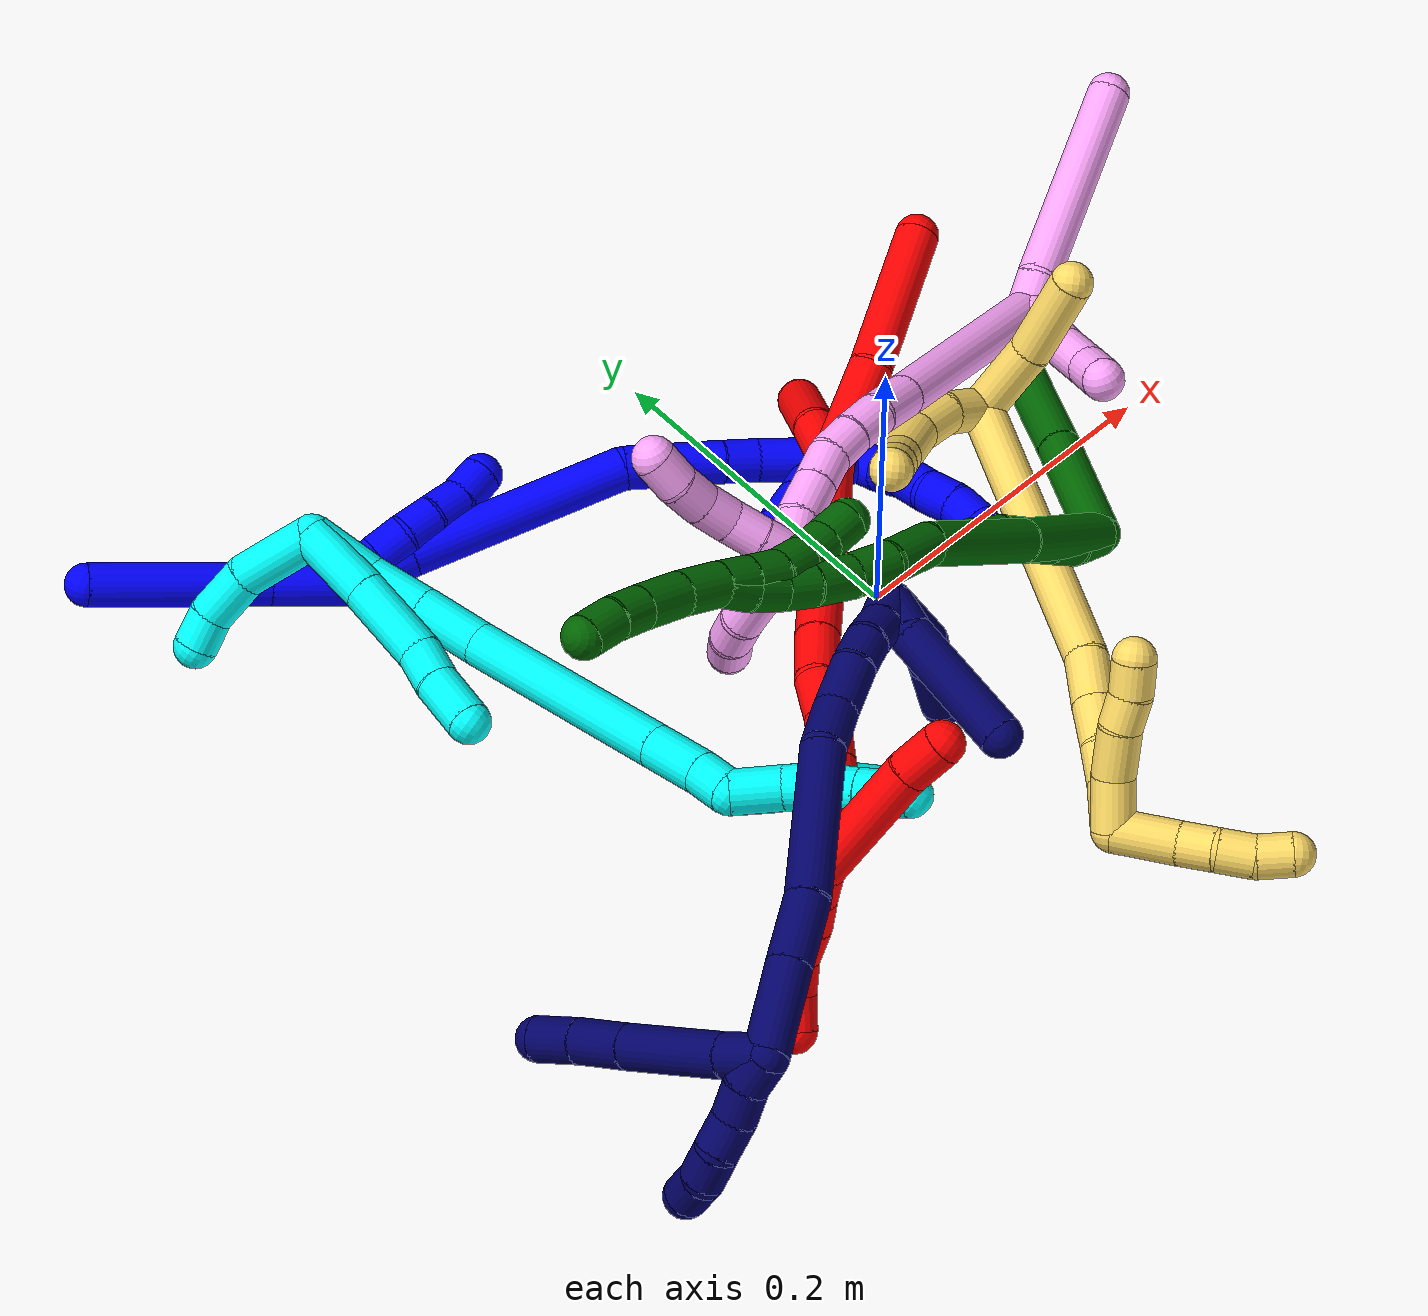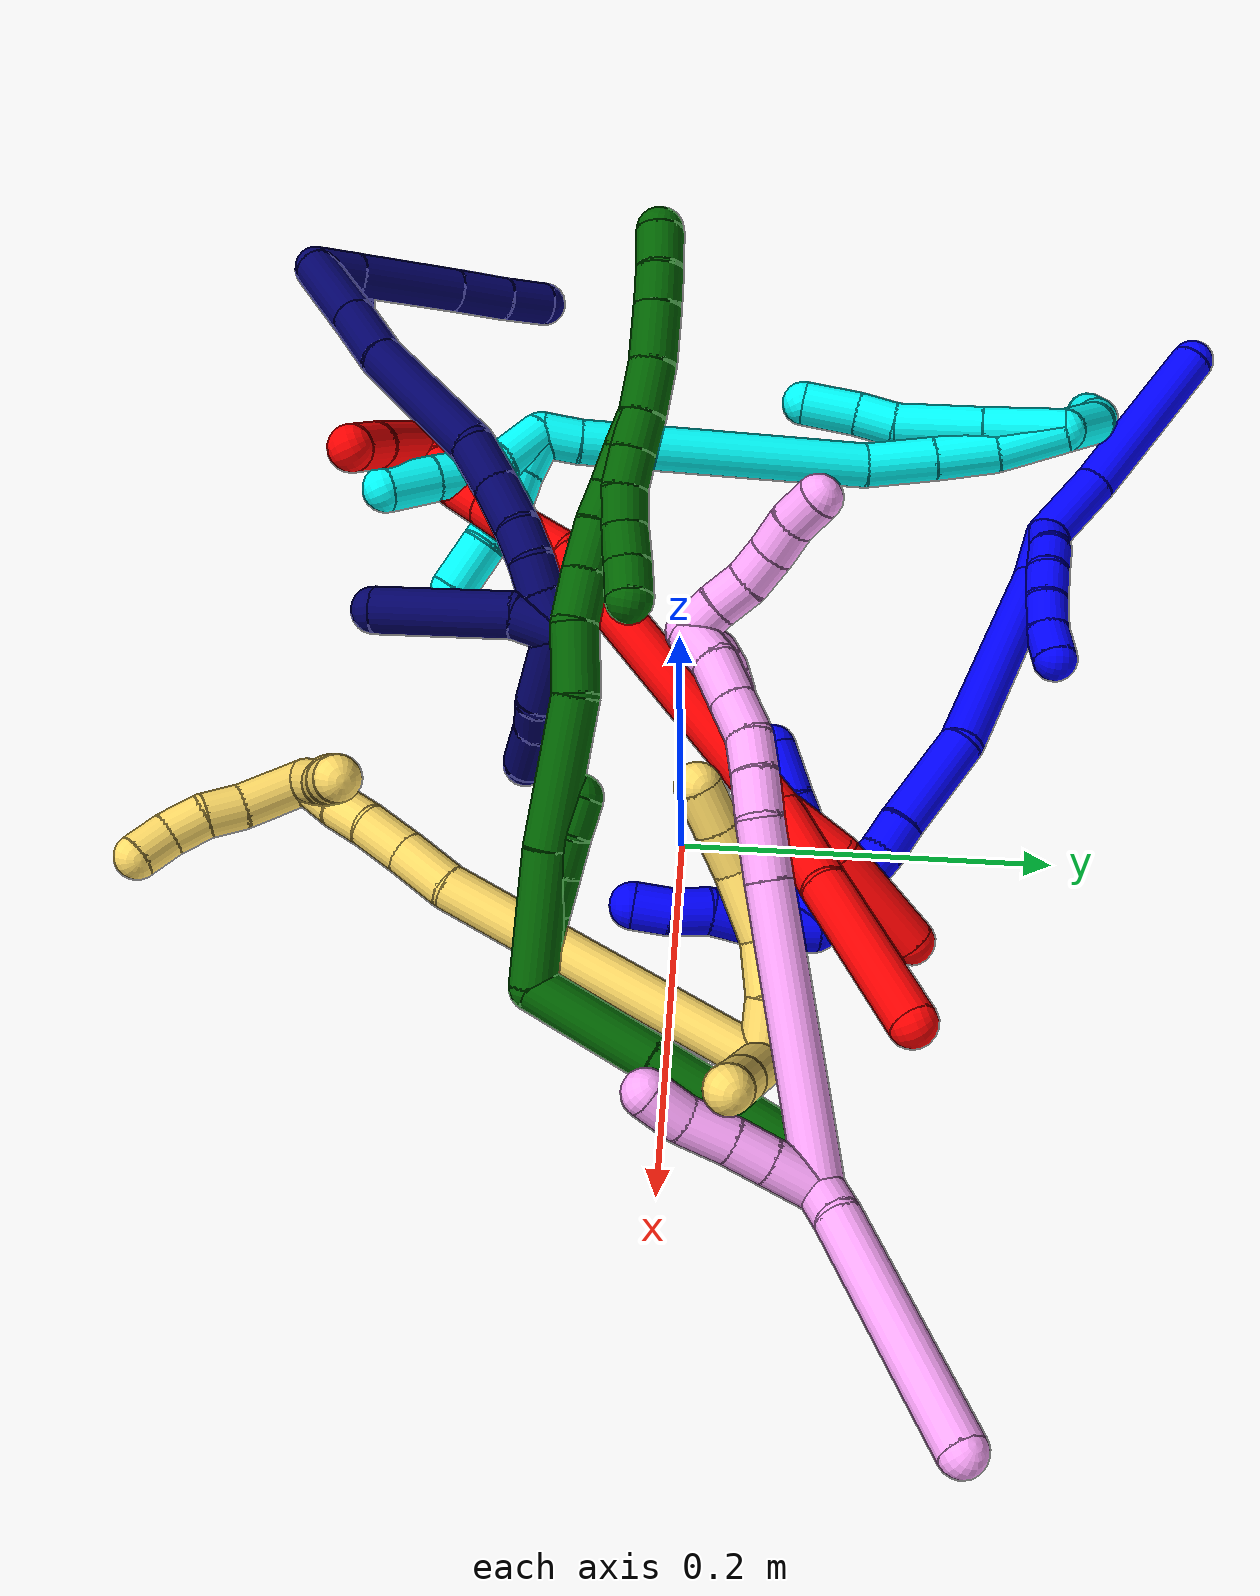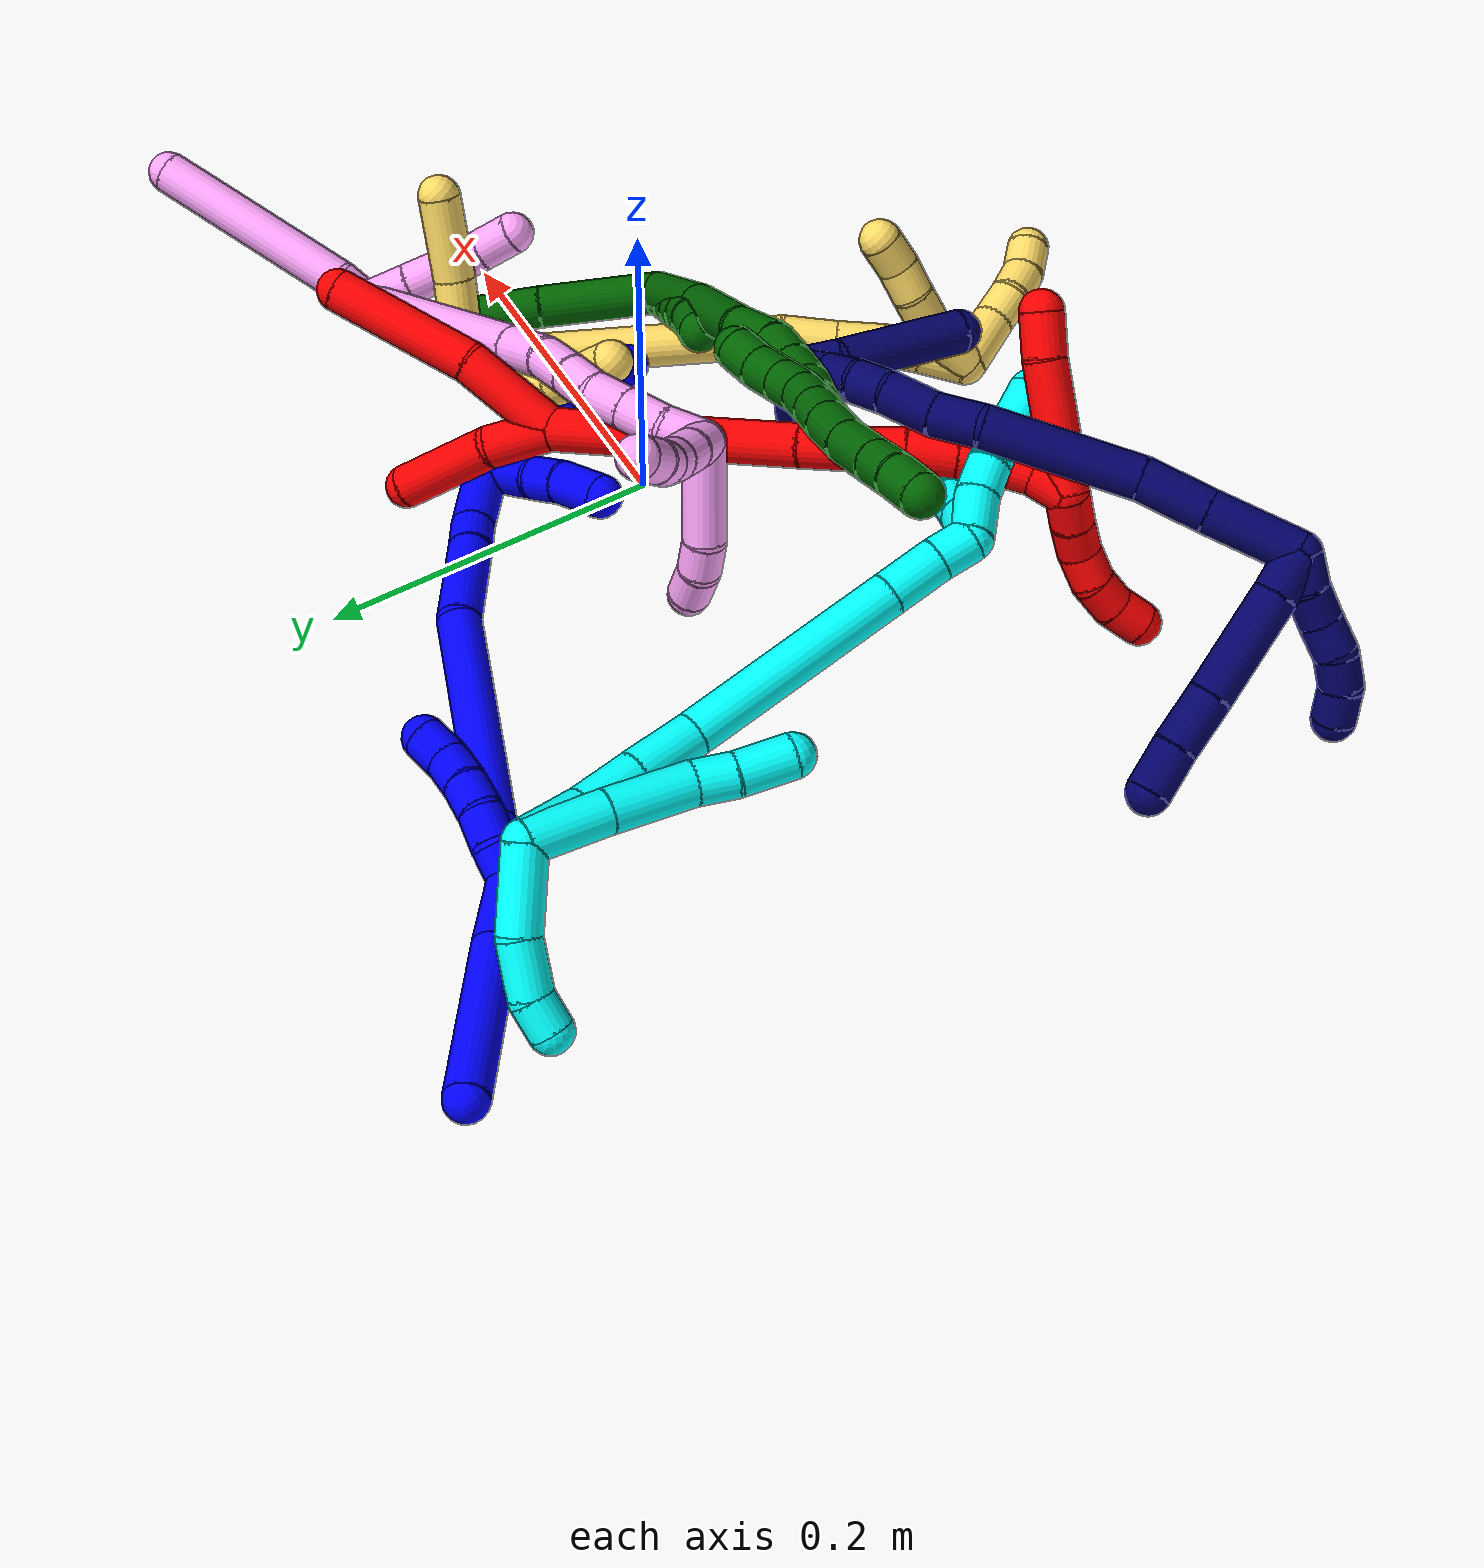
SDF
<sdf version="1.7">
 <world name="default">
  <plugin name="TubeGeneratorPlugin" filename="libtube_generator_plugin.so"/>
  <model name="photoneo_s_sensor">
   <static>1</static>
   <pose>0 0 2 1.57079 1.57079 3.14159</pose>
   <link name="link">
    <inertial><mass>0.1</mass></inertial>
    <sensor name="sensor" type="depth">
     <update_rate>30</update_rate>
     <camera>
      <horizontal_fov>1.22</horizontal_fov>
      <image><width>1920</width><height>1200</height><format>B8G8R8</format></image>
      <clip><near>0.1</near><far>4</far></clip>
      <depth_camera><output>points</output></depth_camera>
     </camera>
     <plugin name="camera_plugin" filename="libgazebo_ros_depth_camera.so">
      <baseline>0.2</baseline>
      <alwaysOn>1</alwaysOn>
      <updateRate>0.0</updateRate>
      <cameraName>camera_ir</cameraName>
      <imageTopicName>/camera/color/image_raw</imageTopicName>
      <cameraInfoTopicName>/camera/color/camera_info</cameraInfoTopicName>
      <depthImageTopicName>/camera/depth/image_raw</depthImageTopicName>
      <depthImageCameraInfoTopicName>/camera/depth/camera_info</depthImageCameraInfoTopicName>
      <pointCloudTopicName>/camera/depth/points</pointCloudTopicName>
      <frameName>fr_optical</frameName>
      <pointCloudCutoff>0.1</pointCloudCutoff>
      <pointCloudCutoffMax>2.0</pointCloudCutoffMax>
      <distortionK1>0</distortionK1>
      <distortionK2>0</distortionK2>
      <distortionK3>0</distortionK3>
      <distortionT1>0</distortionT1>
      <distortionT2>0</distortionT2>
      <CxPrime>0</CxPrime>
      <Cx>0</Cx>
      <Cy>0</Cy>
      <focalLength>0</focalLength>
      <hackBaseline>0</hackBaseline>
     </plugin>
    </sensor>
   </link>
  </model>
  <gravity>0 0 -9.8</gravity>
  <magnetic_field>6e-06 2.3e-05 -4.2e-05</magnetic_field>
  <atmosphere type="adiabatic"/>
  <physics name="default_physics" default="0" type="ode">
   <max_step_size>0.003</max_step_size>
   <real_time_factor>1</real_time_factor>
   <real_time_update_rate>1000</real_time_update_rate>
   <max_contacts>10000</max_contacts>
   <ode>
    <solver>
     <type>quick</type>
     <iters>100</iters>
     <sor>1.3</sor>
     <use_dynamic_moi_rescaling>0</use_dynamic_moi_rescaling>
    </solver>
    <constraints>
     <contact_max_correcting_vel>0</contact_max_correcting_vel>
     <contact_surface_layer>0.001</contact_surface_layer>
     <cfm>0</cfm>
     <erp>0.2</erp>
    </constraints>
   </ode>
  </physics>
  <scene><ambient>0.4 0.4 0.4 1</ambient><background>0.7 0.7 0.7 1</background><shadows>0</shadows></scene>
  <audio><device>default</device></audio>
  <spherical_coordinates>
   <surface_model>EARTH_WGS84</surface_model>
   <latitude_deg>0</latitude_deg>
   <longitude_deg>0</longitude_deg>
   <elevation>0</elevation>
   <heading_deg>0</heading_deg>
  </spherical_coordinates>
  <model name="bin">
   <static>1</static>
   <link name="bottom">
    <collision name="collision-bottom">
     <pose>0 0 -0.01 0 -0 0</pose>
     <geometry><box><size>0.8 0.6 0.02</size></box></geometry>
     <surface>
      <friction><ode><mu>100</mu><mu2>100</mu2></ode></friction>
      <contact><collide_bitmask>65535</collide_bitmask></contact>
     </surface>
    </collision>
   </link>
   <link name="west_wall">
    <collision name="collision-west_wall">
     <pose>-0.41 0 0.1 0 -0 0</pose>
     <geometry><box><size>0.02 0.6 0.2</size></box></geometry>
     <surface>
      <friction><ode><mu>100</mu><mu2>100</mu2></ode></friction>
      <contact><collide_bitmask>65535</collide_bitmask></contact>
     </surface>
    </collision>
   </link>
   <link name="east_wall">
    <collision name="collision-east_wall">
     <pose>0.41 0 0.1 0 -0 0</pose>
     <geometry><box><size>0.02 0.6 0.2</size></box></geometry>
     <surface>
      <friction><ode><mu>100</mu><mu2>100</mu2></ode></friction>
      <contact><collide_bitmask>65535</collide_bitmask></contact>
     </surface>
    </collision>
   </link>
   <link name="south_wall">
    <collision name="collision-south_wall">
     <pose>0 -0.31 0.1 0 -0 0</pose>
     <geometry><box><size>0.8 0.02 0.2</size></box></geometry>
     <surface>
      <friction><ode><mu>100</mu><mu2>100</mu2></ode></friction>
      <contact><collide_bitmask>65535</collide_bitmask></contact>
     </surface>
    </collision>
   </link>
   <link name="north_wall">
    <collision name="collision-north_wall">
     <pose>0 0.31 0.1 0 -0 0</pose>
     <geometry><box><size>0.8 0.02 0.2</size></box></geometry>
     <surface>
      <friction><ode><mu>100</mu><mu2>100</mu2></ode></friction>
      <contact><collide_bitmask>65535</collide_bitmask></contact>
     </surface>
    </collision>
   </link>
  </model>
  <model name="1">
   <static>0</static>
   <link name="1">
    <collision name="collision-cylinder-e_1_2_8">
     <pose>-0.01494 0.007499 0.016142 -0.434914 -0.698305 0.160537</pose>
     <geometry><cylinder><radius>0.0125</radius><length>0.046475</length></cylinder></geometry>
     <surface>
      <friction><ode><mu>1.16</mu><mu2>1.16</mu2><slip1>0</slip1><slip2>0</slip2></ode></friction>
      <contact><ode><kp>1e+06</kp><kd>1</kd><max_vel>0</max_vel><min_depth>0.001</min_depth></ode></contact>
     </surface>
    </collision>
    <visual name="visual-cylinder-e_1_2_8">
     <pose>-0.01494 0.007499 0.016142 -0.434914 -0.698305 0.160537</pose>
     <geometry><cylinder><radius>0.0125</radius><length>0.046475</length></cylinder></geometry>
     <material><ambient>0 0 1 1</ambient></material>
    </visual>
    <collision name="collision-cylinder-e_2_8_6">
     <pose>-0.066323 0.03062 0.065558 -0.438921 -0.781076 0.183141</pose>
     <geometry><cylinder><radius>0.0125</radius><length>0.103525</length></cylinder></geometry>
     <surface>
      <friction><ode><mu>1.16</mu><mu2>1.16</mu2><slip1>0</slip1><slip2>0</slip2></ode></friction>
      <contact><ode><kp>1e+06</kp><kd>1</kd><max_vel>0</max_vel><min_depth>0.001</min_depth></ode></contact>
     </surface>
    </collision>
    <visual name="visual-cylinder-e_2_8_6">
     <pose>-0.066323 0.03062 0.065558 -0.438921 -0.781076 0.183141</pose>
     <geometry><cylinder><radius>0.0125</radius><length>0.103525</length></cylinder></geometry>
     <material><ambient>0 0 1 1</ambient></material>
    </visual>
    <collision name="collision-cylinder-e_1_2_9">
     <pose>0.002755 -0.009342 -0.002268 1.80896 0.279113 0.353573</pose>
     <geometry><cylinder><radius>0.0125</radius><length>0.02</length></cylinder></geometry>
     <surface>
      <friction><ode><mu>1.16</mu><mu2>1.16</mu2><slip1>0</slip1><slip2>0</slip2></ode></friction>
      <contact><ode><kp>1e+06</kp><kd>1</kd><max_vel>0</max_vel><min_depth>0.001</min_depth></ode></contact>
     </surface>
    </collision>
    <visual name="visual-cylinder-e_1_2_9">
     <pose>0.002755 -0.009342 -0.002268 1.80896 0.279113 0.353573</pose>
     <geometry><cylinder><radius>0.0125</radius><length>0.02</length></cylinder></geometry>
     <material><ambient>0 0 1 1</ambient></material>
    </visual>
    <collision name="collision-cylinder-e_2_9_10">
     <pose>0.010499 -0.026745 -0.007718 1.94672 0.522304 0.748573</pose>
     <geometry><cylinder><radius>0.0125</radius><length>0.02</length></cylinder></geometry>
     <surface>
      <friction><ode><mu>1.16</mu><mu2>1.16</mu2><slip1>0</slip1><slip2>0</slip2></ode></friction>
      <contact><ode><kp>1e+06</kp><kd>1</kd><max_vel>0</max_vel><min_depth>0.001</min_depth></ode></contact>
     </surface>
    </collision>
    <visual name="visual-cylinder-e_2_9_10">
     <pose>0.010499 -0.026745 -0.007718 1.94672 0.522304 0.748573</pose>
     <geometry><cylinder><radius>0.0125</radius><length>0.02</length></cylinder></geometry>
     <material><ambient>0 0 1 1</ambient></material>
    </visual>
    <collision name="collision-cylinder-e_3_10_11">
     <pose>0.022266 -0.041804 -0.013153 1.88237 0.74488 0.984459</pose>
     <geometry><cylinder><radius>0.0125</radius><length>0.02</length></cylinder></geometry>
     <surface>
      <friction><ode><mu>1.16</mu><mu2>1.16</mu2><slip1>0</slip1><slip2>0</slip2></ode></friction>
      <contact><ode><kp>1e+06</kp><kd>1</kd><max_vel>0</max_vel><min_depth>0.001</min_depth></ode></contact>
     </surface>
    </collision>
    <visual name="visual-cylinder-e_3_10_11">
     <pose>0.022266 -0.041804 -0.013153 1.88237 0.74488 0.984459</pose>
     <geometry><cylinder><radius>0.0125</radius><length>0.02</length></cylinder></geometry>
     <material><ambient>0 0 1 1</ambient></material>
    </visual>
    <collision name="collision-cylinder-e_4_11_12">
     <pose>0.036652 -0.055152 -0.016757 1.78031 0.864291 1.03554</pose>
     <geometry><cylinder><radius>0.0125</radius><length>0.02</length></cylinder></geometry>
     <surface>
      <friction><ode><mu>1.16</mu><mu2>1.16</mu2><slip1>0</slip1><slip2>0</slip2></ode></friction>
      <contact><ode><kp>1e+06</kp><kd>1</kd><max_vel>0</max_vel><min_depth>0.001</min_depth></ode></contact>
     </surface>
    </collision>
    <visual name="visual-cylinder-e_4_11_12">
     <pose>0.036652 -0.055152 -0.016757 1.78031 0.864291 1.03554</pose>
     <geometry><cylinder><radius>0.0125</radius><length>0.02</length></cylinder></geometry>
     <material><ambient>0 0 1 1</ambient></material>
    </visual>
    <collision name="collision-cylinder-e_5_12_5">
     <pose>0.050883 -0.068984 -0.017762 1.52475 0.724205 0.694211</pose>
     <geometry><cylinder><radius>0.0125</radius><length>0.02</length></cylinder></geometry>
     <surface>
      <friction><ode><mu>1.16</mu><mu2>1.16</mu2><slip1>0</slip1><slip2>0</slip2></ode></friction>
      <contact><ode><kp>1e+06</kp><kd>1</kd><max_vel>0</max_vel><min_depth>0.001</min_depth></ode></contact>
     </surface>
    </collision>
    <visual name="visual-cylinder-e_5_12_5">
     <pose>0.050883 -0.068984 -0.017762 1.52475 0.724205 0.694211</pose>
     <geometry><cylinder><radius>0.0125</radius><length>0.02</length></cylinder></geometry>
     <material><ambient>0 0 1 1</ambient></material>
    </visual>
    <collision name="collision-cylinder-e_1_2_13">
     <pose>0.011467 -0.012078 -0.007174 2.10675 0.684592 1.11873</pose>
     <geometry><cylinder><radius>0.0125</radius><length>0.036268</length></cylinder></geometry>
     <surface>
      <friction><ode><mu>1.16</mu><mu2>1.16</mu2><slip1>0</slip1><slip2>0</slip2></ode></friction>
      <contact><ode><kp>1e+06</kp><kd>1</kd><max_vel>0</max_vel><min_depth>0.001</min_depth></ode></contact>
     </surface>
    </collision>
    <visual name="visual-cylinder-e_1_2_13">
     <pose>0.011467 -0.012078 -0.007174 2.10675 0.684592 1.11873</pose>
     <geometry><cylinder><radius>0.0125</radius><length>0.036268</length></cylinder></geometry>
     <material><ambient>0 0 1 1</ambient></material>
    </visual>
    <collision name="collision-cylinder-e_2_13_14">
     <pose>0.06112 -0.065882 -0.046494 2.22725 0.627287 1.16582</pose>
     <geometry><cylinder><radius>0.0125</radius><length>0.130117</length></cylinder></geometry>
     <surface>
      <friction><ode><mu>1.16</mu><mu2>1.16</mu2><slip1>0</slip1><slip2>0</slip2></ode></friction>
      <contact><ode><kp>1e+06</kp><kd>1</kd><max_vel>0</max_vel><min_depth>0.001</min_depth></ode></contact>
     </surface>
    </collision>
    <visual name="visual-cylinder-e_2_13_14">
     <pose>0.06112 -0.065882 -0.046494 2.22725 0.627287 1.16582</pose>
     <geometry><cylinder><radius>0.0125</radius><length>0.130117</length></cylinder></geometry>
     <material><ambient>0 0 1 1</ambient></material>
    </visual>
    <collision name="collision-cylinder-e_3_14_15">
     <pose>0.118866 -0.118114 -0.097045 2.62286 0.745375 1.94901</pose>
     <geometry><cylinder><radius>0.0125</radius><length>0.057678</length></cylinder></geometry>
     <surface>
      <friction><ode><mu>1.16</mu><mu2>1.16</mu2><slip1>0</slip1><slip2>0</slip2></ode></friction>
      <contact><ode><kp>1e+06</kp><kd>1</kd><max_vel>0</max_vel><min_depth>0.001</min_depth></ode></contact>
     </surface>
    </collision>
    <visual name="visual-cylinder-e_3_14_15">
     <pose>0.118866 -0.118114 -0.097045 2.62286 0.745375 1.94901</pose>
     <geometry><cylinder><radius>0.0125</radius><length>0.057678</length></cylinder></geometry>
     <material><ambient>0 0 1 1</ambient></material>
    </visual>
    <collision name="collision-cylinder-e_4_15_16">
     <pose>0.145834 -0.131995 -0.121399 2.62565 0.825182 2.05665</pose>
     <geometry><cylinder><radius>0.0125</radius><length>0.020167</length></cylinder></geometry>
     <surface>
      <friction><ode><mu>1.16</mu><mu2>1.16</mu2><slip1>0</slip1><slip2>0</slip2></ode></friction>
      <contact><ode><kp>1e+06</kp><kd>1</kd><max_vel>0</max_vel><min_depth>0.001</min_depth></ode></contact>
     </surface>
    </collision>
    <visual name="visual-cylinder-e_4_15_16">
     <pose>0.145834 -0.131995 -0.121399 2.62565 0.825182 2.05665</pose>
     <geometry><cylinder><radius>0.0125</radius><length>0.020167</length></cylinder></geometry>
     <material><ambient>0 0 1 1</ambient></material>
    </visual>
    <collision name="collision-cylinder-e_5_16_1">
     <pose>0.171236 -0.144653 -0.146524 2.69072 0.701366 2.02162</pose>
     <geometry><cylinder><radius>0.0125</radius><length>0.05577</length></cylinder></geometry>
     <surface>
      <friction><ode><mu>1.16</mu><mu2>1.16</mu2><slip1>0</slip1><slip2>0</slip2></ode></friction>
      <contact><ode><kp>1e+06</kp><kd>1</kd><max_vel>0</max_vel><min_depth>0.001</min_depth></ode></contact>
     </surface>
    </collision>
    <visual name="visual-cylinder-e_5_16_1">
     <pose>0.171236 -0.144653 -0.146524 2.69072 0.701366 2.02162</pose>
     <geometry><cylinder><radius>0.0125</radius><length>0.05577</length></cylinder></geometry>
     <material><ambient>0 0 1 1</ambient></material>
    </visual>
    <collision name="collision-cylinder-e_1_1_17">
     <pose>0.189069 -0.154071 -0.175696 3.12806 -0.016016 -1.73847</pose>
     <geometry><cylinder><radius>0.0125</radius><length>0.02</length></cylinder></geometry>
     <surface>
      <friction><ode><mu>1.16</mu><mu2>1.16</mu2><slip1>0</slip1><slip2>0</slip2></ode></friction>
      <contact><ode><kp>1e+06</kp><kd>1</kd><max_vel>0</max_vel><min_depth>0.001</min_depth></ode></contact>
     </surface>
    </collision>
    <visual name="visual-cylinder-e_1_1_17">
     <pose>0.189069 -0.154071 -0.175696 3.12806 -0.016016 -1.73847</pose>
     <geometry><cylinder><radius>0.0125</radius><length>0.02</length></cylinder></geometry>
     <material><ambient>0 0 1 1</ambient></material>
    </visual>
    <collision name="collision-cylinder-e_2_17_18">
     <pose>0.186061 -0.155743 -0.195156 2.98059 -0.288798 -2.12856</pose>
     <geometry><cylinder><radius>0.0125</radius><length>0.02</length></cylinder></geometry>
     <surface>
      <friction><ode><mu>1.16</mu><mu2>1.16</mu2><slip1>0</slip1><slip2>0</slip2></ode></friction>
      <contact><ode><kp>1e+06</kp><kd>1</kd><max_vel>0</max_vel><min_depth>0.001</min_depth></ode></contact>
     </surface>
    </collision>
    <visual name="visual-cylinder-e_2_17_18">
     <pose>0.186061 -0.155743 -0.195156 2.98059 -0.288798 -2.12856</pose>
     <geometry><cylinder><radius>0.0125</radius><length>0.02</length></cylinder></geometry>
     <material><ambient>0 0 1 1</ambient></material>
    </visual>
    <collision name="collision-cylinder-e_3_18_19">
     <pose>0.180879 -0.156662 -0.214322 -3.07801 -0.23553 2.61639</pose>
     <geometry><cylinder><radius>0.0125</radius><length>0.02</length></cylinder></geometry>
     <surface>
      <friction><ode><mu>1.16</mu><mu2>1.16</mu2><slip1>0</slip1><slip2>0</slip2></ode></friction>
      <contact><ode><kp>1e+06</kp><kd>1</kd><max_vel>0</max_vel><min_depth>0.001</min_depth></ode></contact>
     </surface>
    </collision>
    <visual name="visual-cylinder-e_3_18_19">
     <pose>0.180879 -0.156662 -0.214322 -3.07801 -0.23553 2.61639</pose>
     <geometry><cylinder><radius>0.0125</radius><length>0.02</length></cylinder></geometry>
     <material><ambient>0 0 1 1</ambient></material>
    </visual>
    <collision name="collision-cylinder-e_4_19_20">
     <pose>0.178918 -0.1558 -0.234016 -3.11715 0.037283 -1.98113</pose>
     <geometry><cylinder><radius>0.0125</radius><length>0.02</length></cylinder></geometry>
     <surface>
      <friction><ode><mu>1.16</mu><mu2>1.16</mu2><slip1>0</slip1><slip2>0</slip2></ode></friction>
      <contact><ode><kp>1e+06</kp><kd>1</kd><max_vel>0</max_vel><min_depth>0.001</min_depth></ode></contact>
     </surface>
    </collision>
    <visual name="visual-cylinder-e_4_19_20">
     <pose>0.178918 -0.1558 -0.234016 -3.11715 0.037283 -1.98113</pose>
     <geometry><cylinder><radius>0.0125</radius><length>0.02</length></cylinder></geometry>
     <material><ambient>0 0 1 1</ambient></material>
    </visual>
    <collision name="collision-cylinder-e_5_20_4">
     <pose>0.178329 -0.153243 -0.253687 -2.90712 -0.096357 0.777149</pose>
     <geometry><cylinder><radius>0.0125</radius><length>0.02</length></cylinder></geometry>
     <surface>
      <friction><ode><mu>1.16</mu><mu2>1.16</mu2><slip1>0</slip1><slip2>0</slip2></ode></friction>
      <contact><ode><kp>1e+06</kp><kd>1</kd><max_vel>0</max_vel><min_depth>0.001</min_depth></ode></contact>
     </surface>
    </collision>
    <visual name="visual-cylinder-e_5_20_4">
     <pose>0.178329 -0.153243 -0.253687 -2.90712 -0.096357 0.777149</pose>
     <geometry><cylinder><radius>0.0125</radius><length>0.02</length></cylinder></geometry>
     <material><ambient>0 0 1 1</ambient></material>
    </visual>
    <collision name="collision-cylinder-e_1_1_21">
     <pose>0.180153 -0.149393 -0.166022 -1.64209 -1.10566 1.17042</pose>
     <geometry><cylinder><radius>0.0125</radius><length>0.020309</length></cylinder></geometry>
     <surface>
      <friction><ode><mu>1.16</mu><mu2>1.16</mu2><slip1>0</slip1><slip2>0</slip2></ode></friction>
      <contact><ode><kp>1e+06</kp><kd>1</kd><max_vel>0</max_vel><min_depth>0.001</min_depth></ode></contact>
     </surface>
    </collision>
    <visual name="visual-cylinder-e_1_1_21">
     <pose>0.180153 -0.149393 -0.166022 -1.64209 -1.10566 1.17042</pose>
     <geometry><cylinder><radius>0.0125</radius><length>0.020309</length></cylinder></geometry>
     <material><ambient>0 0 1 1</ambient></material>
    </visual>
    <collision name="collision-cylinder-e_2_21_22">
     <pose>0.15681 -0.140976 -0.168748 -2.12571 -1.26159 1.83907</pose>
     <geometry><cylinder><radius>0.0125</radius><length>0.029955</length></cylinder></geometry>
     <surface>
      <friction><ode><mu>1.16</mu><mu2>1.16</mu2><slip1>0</slip1><slip2>0</slip2></ode></friction>
      <contact><ode><kp>1e+06</kp><kd>1</kd><max_vel>0</max_vel><min_depth>0.001</min_depth></ode></contact>
     </surface>
    </collision>
    <visual name="visual-cylinder-e_2_21_22">
     <pose>0.15681 -0.140976 -0.168748 -2.12571 -1.26159 1.83907</pose>
     <geometry><cylinder><radius>0.0125</radius><length>0.029955</length></cylinder></geometry>
     <material><ambient>0 0 1 1</ambient></material>
    </visual>
    <collision name="collision-cylinder-e_3_22_23">
     <pose>0.133902 -0.13299 -0.174631 -2.27327 -1.01323 1.74949</pose>
     <geometry><cylinder><radius>0.0125</radius><length>0.020367</length></cylinder></geometry>
     <surface>
      <friction><ode><mu>1.16</mu><mu2>1.16</mu2><slip1>0</slip1><slip2>0</slip2></ode></friction>
      <contact><ode><kp>1e+06</kp><kd>1</kd><max_vel>0</max_vel><min_depth>0.001</min_depth></ode></contact>
     </surface>
    </collision>
    <visual name="visual-cylinder-e_3_22_23">
     <pose>0.133902 -0.13299 -0.174631 -2.27327 -1.01323 1.74949</pose>
     <geometry><cylinder><radius>0.0125</radius><length>0.020367</length></cylinder></geometry>
     <material><ambient>0 0 1 1</ambient></material>
    </visual>
    <collision name="collision-cylinder-e_4_23_3">
     <pose>0.113487 -0.120982 -0.181944 -2.02257 -0.930271 1.35113</pose>
     <geometry><cylinder><radius>0.0125</radius><length>0.029369</length></cylinder></geometry>
     <surface>
      <friction><ode><mu>1.16</mu><mu2>1.16</mu2><slip1>0</slip1><slip2>0</slip2></ode></friction>
      <contact><ode><kp>1e+06</kp><kd>1</kd><max_vel>0</max_vel><min_depth>0.001</min_depth></ode></contact>
     </surface>
    </collision>
    <visual name="visual-cylinder-e_4_23_3">
     <pose>0.113487 -0.120982 -0.181944 -2.02257 -0.930271 1.35113</pose>
     <geometry><cylinder><radius>0.0125</radius><length>0.029369</length></cylinder></geometry>
     <material><ambient>0 0 1 1</ambient></material>
    </visual>
    <collision name="collision-sphere-3">
     <pose>0.101713 -0.113086 -0.185775 0 -0 0</pose>
     <geometry><sphere><radius>0.0125</radius></sphere></geometry>
     <surface>
      <friction><ode><mu>1.16</mu><mu2>1.16</mu2><slip1>0</slip1><slip2>0</slip2></ode></friction>
      <contact><ode><kp>1e+06</kp><kd>1</kd><max_vel>0</max_vel><min_depth>0.001</min_depth></ode></contact>
     </surface>
    </collision>
    <visual name="visual-sphere-3">
     <pose>0.101713 -0.113086 -0.185775 0 -0 0</pose>
     <geometry><sphere><radius>0.0125</radius></sphere></geometry>
     <material><ambient>0 0 1 1</ambient></material>
    </visual>
    <collision name="collision-sphere-23">
     <pose>0.125261 -0.128877 -0.178112 0 -0 0</pose>
     <geometry><sphere><radius>0.0125</radius></sphere></geometry>
     <surface>
      <friction><ode><mu>1.16</mu><mu2>1.16</mu2><slip1>0</slip1><slip2>0</slip2></ode></friction>
      <contact><ode><kp>1e+06</kp><kd>1</kd><max_vel>0</max_vel><min_depth>0.001</min_depth></ode></contact>
     </surface>
    </collision>
    <visual name="visual-sphere-23">
     <pose>0.125261 -0.128877 -0.178112 0 -0 0</pose>
     <geometry><sphere><radius>0.0125</radius></sphere></geometry>
     <material><ambient>0 0 1 1</ambient></material>
    </visual>
    <collision name="collision-sphere-22">
     <pose>0.142543 -0.137102 -0.171149 0 -0 0</pose>
     <geometry><sphere><radius>0.0125</radius></sphere></geometry>
     <surface>
      <friction><ode><mu>1.16</mu><mu2>1.16</mu2><slip1>0</slip1><slip2>0</slip2></ode></friction>
      <contact><ode><kp>1e+06</kp><kd>1</kd><max_vel>0</max_vel><min_depth>0.001</min_depth></ode></contact>
     </surface>
    </collision>
    <visual name="visual-sphere-22">
     <pose>0.142543 -0.137102 -0.171149 0 -0 0</pose>
     <geometry><sphere><radius>0.0125</radius></sphere></geometry>
     <material><ambient>0 0 1 1</ambient></material>
    </visual>
    <collision name="collision-sphere-21">
     <pose>0.171077 -0.14485 -0.166347 0 -0 0</pose>
     <geometry><sphere><radius>0.0125</radius></sphere></geometry>
     <surface>
      <friction><ode><mu>1.16</mu><mu2>1.16</mu2><slip1>0</slip1><slip2>0</slip2></ode></friction>
      <contact><ode><kp>1e+06</kp><kd>1</kd><max_vel>0</max_vel><min_depth>0.001</min_depth></ode></contact>
     </surface>
    </collision>
    <visual name="visual-sphere-21">
     <pose>0.171077 -0.14485 -0.166347 0 -0 0</pose>
     <geometry><sphere><radius>0.0125</radius></sphere></geometry>
     <material><ambient>0 0 1 1</ambient></material>
    </visual>
    <collision name="collision-sphere-4">
     <pose>0.177367 -0.150931 -0.263369 0 -0 0</pose>
     <geometry><sphere><radius>0.0125</radius></sphere></geometry>
     <surface>
      <friction><ode><mu>1.16</mu><mu2>1.16</mu2><slip1>0</slip1><slip2>0</slip2></ode></friction>
      <contact><ode><kp>1e+06</kp><kd>1</kd><max_vel>0</max_vel><min_depth>0.001</min_depth></ode></contact>
     </surface>
    </collision>
    <visual name="visual-sphere-4">
     <pose>0.177367 -0.150931 -0.263369 0 -0 0</pose>
     <geometry><sphere><radius>0.0125</radius></sphere></geometry>
     <material><ambient>0 0 1 1</ambient></material>
    </visual>
    <collision name="collision-sphere-20">
     <pose>0.179291 -0.155556 -0.244006 0 -0 0</pose>
     <geometry><sphere><radius>0.0125</radius></sphere></geometry>
     <surface>
      <friction><ode><mu>1.16</mu><mu2>1.16</mu2><slip1>0</slip1><slip2>0</slip2></ode></friction>
      <contact><ode><kp>1e+06</kp><kd>1</kd><max_vel>0</max_vel><min_depth>0.001</min_depth></ode></contact>
     </surface>
    </collision>
    <visual name="visual-sphere-20">
     <pose>0.179291 -0.155556 -0.244006 0 -0 0</pose>
     <geometry><sphere><radius>0.0125</radius></sphere></geometry>
     <material><ambient>0 0 1 1</ambient></material>
    </visual>
    <collision name="collision-sphere-11">
     <pose>0.029045 -0.048802 -0.015407 0 -0 0</pose>
     <geometry><sphere><radius>0.0125</radius></sphere></geometry>
     <surface>
      <friction><ode><mu>1.16</mu><mu2>1.16</mu2><slip1>0</slip1><slip2>0</slip2></ode></friction>
      <contact><ode><kp>1e+06</kp><kd>1</kd><max_vel>0</max_vel><min_depth>0.001</min_depth></ode></contact>
     </surface>
    </collision>
    <visual name="visual-sphere-11">
     <pose>0.029045 -0.048802 -0.015407 0 -0 0</pose>
     <geometry><sphere><radius>0.0125</radius></sphere></geometry>
     <material><ambient>0 0 1 1</ambient></material>
    </visual>
    <collision name="collision-sphere-10">
     <pose>0.015488 -0.034806 -0.010899 0 -0 0</pose>
     <geometry><sphere><radius>0.0125</radius></sphere></geometry>
     <surface>
      <friction><ode><mu>1.16</mu><mu2>1.16</mu2><slip1>0</slip1><slip2>0</slip2></ode></friction>
      <contact><ode><kp>1e+06</kp><kd>1</kd><max_vel>0</max_vel><min_depth>0.001</min_depth></ode></contact>
     </surface>
    </collision>
    <visual name="visual-sphere-10">
     <pose>0.015488 -0.034806 -0.010899 0 -0 0</pose>
     <geometry><sphere><radius>0.0125</radius></sphere></geometry>
     <material><ambient>0 0 1 1</ambient></material>
    </visual>
    <collision name="collision-sphere-6">
     <pose>-0.102766 0.046241 0.098833 0 -0 0</pose>
     <geometry><sphere><radius>0.0125</radius></sphere></geometry>
     <surface>
      <friction><ode><mu>1.16</mu><mu2>1.16</mu2><slip1>0</slip1><slip2>0</slip2></ode></friction>
      <contact><ode><kp>1e+06</kp><kd>1</kd><max_vel>0</max_vel><min_depth>0.001</min_depth></ode></contact>
     </surface>
    </collision>
    <visual name="visual-sphere-6">
     <pose>-0.102766 0.046241 0.098833 0 -0 0</pose>
     <geometry><sphere><radius>0.0125</radius></sphere></geometry>
     <material><ambient>0 0 1 1</ambient></material>
    </visual>
    <collision name="collision-sphere-9">
     <pose>0.00551 -0.018683 -0.004536 0 -0 0</pose>
     <geometry><sphere><radius>0.0125</radius></sphere></geometry>
     <surface>
      <friction><ode><mu>1.16</mu><mu2>1.16</mu2><slip1>0</slip1><slip2>0</slip2></ode></friction>
      <contact><ode><kp>1e+06</kp><kd>1</kd><max_vel>0</max_vel><min_depth>0.001</min_depth></ode></contact>
     </surface>
    </collision>
    <visual name="visual-sphere-9">
     <pose>0.00551 -0.018683 -0.004536 0 -0 0</pose>
     <geometry><sphere><radius>0.0125</radius></sphere></geometry>
     <material><ambient>0 0 1 1</ambient></material>
    </visual>
    <collision name="collision-sphere-2">
     <geometry><sphere><radius>0.0125</radius></sphere></geometry>
     <surface>
      <friction><ode><mu>1.16</mu><mu2>1.16</mu2><slip1>0</slip1><slip2>0</slip2></ode></friction>
      <contact><ode><kp>1e+06</kp><kd>1</kd><max_vel>0</max_vel><min_depth>0.001</min_depth></ode></contact>
     </surface>
    </collision>
    <visual name="visual-sphere-2">
     <geometry><sphere><radius>0.0125</radius></sphere></geometry>
     <material><ambient>0 0 1 1</ambient></material>
    </visual>
    <collision name="collision-sphere-19">
     <pose>0.178545 -0.156044 -0.224026 0 -0 0</pose>
     <geometry><sphere><radius>0.0125</radius></sphere></geometry>
     <surface>
      <friction><ode><mu>1.16</mu><mu2>1.16</mu2><slip1>0</slip1><slip2>0</slip2></ode></friction>
      <contact><ode><kp>1e+06</kp><kd>1</kd><max_vel>0</max_vel><min_depth>0.001</min_depth></ode></contact>
     </surface>
    </collision>
    <visual name="visual-sphere-19">
     <pose>0.178545 -0.156044 -0.224026 0 -0 0</pose>
     <geometry><sphere><radius>0.0125</radius></sphere></geometry>
     <material><ambient>0 0 1 1</ambient></material>
    </visual>
    <collision name="collision-sphere-8">
     <pose>-0.02988 0.014998 0.032283 0 -0 0</pose>
     <geometry><sphere><radius>0.0125</radius></sphere></geometry>
     <surface>
      <friction><ode><mu>1.16</mu><mu2>1.16</mu2><slip1>0</slip1><slip2>0</slip2></ode></friction>
      <contact><ode><kp>1e+06</kp><kd>1</kd><max_vel>0</max_vel><min_depth>0.001</min_depth></ode></contact>
     </surface>
    </collision>
    <visual name="visual-sphere-8">
     <pose>-0.02988 0.014998 0.032283 0 -0 0</pose>
     <geometry><sphere><radius>0.0125</radius></sphere></geometry>
     <material><ambient>0 0 1 1</ambient></material>
    </visual>
    <collision name="collision-sphere-12">
     <pose>0.044258 -0.061501 -0.018107 0 -0 0</pose>
     <geometry><sphere><radius>0.0125</radius></sphere></geometry>
     <surface>
      <friction><ode><mu>1.16</mu><mu2>1.16</mu2><slip1>0</slip1><slip2>0</slip2></ode></friction>
      <contact><ode><kp>1e+06</kp><kd>1</kd><max_vel>0</max_vel><min_depth>0.001</min_depth></ode></contact>
     </surface>
    </collision>
    <visual name="visual-sphere-12">
     <pose>0.044258 -0.061501 -0.018107 0 -0 0</pose>
     <geometry><sphere><radius>0.0125</radius></sphere></geometry>
     <material><ambient>0 0 1 1</ambient></material>
    </visual>
    <collision name="collision-sphere-5">
     <pose>0.057509 -0.076466 -0.017418 0 -0 0</pose>
     <geometry><sphere><radius>0.0125</radius></sphere></geometry>
     <surface>
      <friction><ode><mu>1.16</mu><mu2>1.16</mu2><slip1>0</slip1><slip2>0</slip2></ode></friction>
      <contact><ode><kp>1e+06</kp><kd>1</kd><max_vel>0</max_vel><min_depth>0.001</min_depth></ode></contact>
     </surface>
    </collision>
    <visual name="visual-sphere-5">
     <pose>0.057509 -0.076466 -0.017418 0 -0 0</pose>
     <geometry><sphere><radius>0.0125</radius></sphere></geometry>
     <material><ambient>0 0 1 1</ambient></material>
    </visual>
    <collision name="collision-sphere-13">
     <pose>0.022934 -0.024156 -0.014347 0 -0 0</pose>
     <geometry><sphere><radius>0.0125</radius></sphere></geometry>
     <surface>
      <friction><ode><mu>1.16</mu><mu2>1.16</mu2><slip1>0</slip1><slip2>0</slip2></ode></friction>
      <contact><ode><kp>1e+06</kp><kd>1</kd><max_vel>0</max_vel><min_depth>0.001</min_depth></ode></contact>
     </surface>
    </collision>
    <visual name="visual-sphere-13">
     <pose>0.022934 -0.024156 -0.014347 0 -0 0</pose>
     <geometry><sphere><radius>0.0125</radius></sphere></geometry>
     <material><ambient>0 0 1 1</ambient></material>
    </visual>
    <collision name="collision-sphere-14">
     <pose>0.099306 -0.107607 -0.078641 0 -0 0</pose>
     <geometry><sphere><radius>0.0125</radius></sphere></geometry>
     <surface>
      <friction><ode><mu>1.16</mu><mu2>1.16</mu2><slip1>0</slip1><slip2>0</slip2></ode></friction>
      <contact><ode><kp>1e+06</kp><kd>1</kd><max_vel>0</max_vel><min_depth>0.001</min_depth></ode></contact>
     </surface>
    </collision>
    <visual name="visual-sphere-14">
     <pose>0.099306 -0.107607 -0.078641 0 -0 0</pose>
     <geometry><sphere><radius>0.0125</radius></sphere></geometry>
     <material><ambient>0 0 1 1</ambient></material>
    </visual>
    <collision name="collision-sphere-15">
     <pose>0.138426 -0.12862 -0.115449 0 -0 0</pose>
     <geometry><sphere><radius>0.0125</radius></sphere></geometry>
     <surface>
      <friction><ode><mu>1.16</mu><mu2>1.16</mu2><slip1>0</slip1><slip2>0</slip2></ode></friction>
      <contact><ode><kp>1e+06</kp><kd>1</kd><max_vel>0</max_vel><min_depth>0.001</min_depth></ode></contact>
     </surface>
    </collision>
    <visual name="visual-sphere-15">
     <pose>0.138426 -0.12862 -0.115449 0 -0 0</pose>
     <geometry><sphere><radius>0.0125</radius></sphere></geometry>
     <material><ambient>0 0 1 1</ambient></material>
    </visual>
    <collision name="collision-sphere-16">
     <pose>0.153243 -0.13537 -0.12735 0 -0 0</pose>
     <geometry><sphere><radius>0.0125</radius></sphere></geometry>
     <surface>
      <friction><ode><mu>1.16</mu><mu2>1.16</mu2><slip1>0</slip1><slip2>0</slip2></ode></friction>
      <contact><ode><kp>1e+06</kp><kd>1</kd><max_vel>0</max_vel><min_depth>0.001</min_depth></ode></contact>
     </surface>
    </collision>
    <visual name="visual-sphere-16">
     <pose>0.153243 -0.13537 -0.12735 0 -0 0</pose>
     <geometry><sphere><radius>0.0125</radius></sphere></geometry>
     <material><ambient>0 0 1 1</ambient></material>
    </visual>
    <collision name="collision-sphere-1">
     <pose>0.189229 -0.153936 -0.165698 0 -0 0</pose>
     <geometry><sphere><radius>0.0125</radius></sphere></geometry>
     <surface>
      <friction><ode><mu>1.16</mu><mu2>1.16</mu2><slip1>0</slip1><slip2>0</slip2></ode></friction>
      <contact><ode><kp>1e+06</kp><kd>1</kd><max_vel>0</max_vel><min_depth>0.001</min_depth></ode></contact>
     </surface>
    </collision>
    <visual name="visual-sphere-1">
     <pose>0.189229 -0.153936 -0.165698 0 -0 0</pose>
     <geometry><sphere><radius>0.0125</radius></sphere></geometry>
     <material><ambient>0 0 1 1</ambient></material>
    </visual>
    <collision name="collision-sphere-18">
     <pose>0.183213 -0.15728 -0.204617 0 -0 0</pose>
     <geometry><sphere><radius>0.0125</radius></sphere></geometry>
     <surface>
      <friction><ode><mu>1.16</mu><mu2>1.16</mu2><slip1>0</slip1><slip2>0</slip2></ode></friction>
      <contact><ode><kp>1e+06</kp><kd>1</kd><max_vel>0</max_vel><min_depth>0.001</min_depth></ode></contact>
     </surface>
    </collision>
    <visual name="visual-sphere-18">
     <pose>0.183213 -0.15728 -0.204617 0 -0 0</pose>
     <geometry><sphere><radius>0.0125</radius></sphere></geometry>
     <material><ambient>0 0 1 1</ambient></material>
    </visual>
    <collision name="collision-sphere-17">
     <pose>0.188909 -0.154207 -0.185694 0 -0 0</pose>
     <geometry><sphere><radius>0.0125</radius></sphere></geometry>
     <surface>
      <friction><ode><mu>1.16</mu><mu2>1.16</mu2><slip1>0</slip1><slip2>0</slip2></ode></friction>
      <contact><ode><kp>1e+06</kp><kd>1</kd><max_vel>0</max_vel><min_depth>0.001</min_depth></ode></contact>
     </surface>
    </collision>
    <visual name="visual-sphere-17">
     <pose>0.188909 -0.154207 -0.185694 0 -0 0</pose>
     <geometry><sphere><radius>0.0125</radius></sphere></geometry>
     <material><ambient>0 0 1 1</ambient></material>
    </visual>
    <inertial>
     <pose>0.07373 -0.074805 -0.073237 0 -0 0</pose>
     <mass>0.75</mass>
     <inertia>
      <ixx>0.000321</ixx>
      <ixy>0</ixy>
      <ixz>0</ixz>
      <iyy>0.000349</iyy>
      <iyz>0</iyz>
      <izz>3.2e-05</izz>
     </inertia>
    </inertial>
   </link>
   <pose>-0.214056 0.200167 0.011598 -1.85105 0.795202 -0.037376</pose>
  </model>
  <model name="2">
   <static>0</static>
   <link name="2">
    <collision name="collision-cylinder-e_1_2_8">
     <pose>0.027391 -0.010762 0.006991 0.99469 1.13265 0.664689</pose>
     <geometry><cylinder><radius>0.0125</radius><length>0.060496</length></cylinder></geometry>
     <surface>
      <friction><ode><mu>1.16</mu><mu2>1.16</mu2><slip1>0</slip1><slip2>0</slip2></ode></friction>
      <contact><ode><kp>1e+06</kp><kd>1</kd><max_vel>0</max_vel><min_depth>0.001</min_depth></ode></contact>
     </surface>
    </collision>
    <visual name="visual-cylinder-e_1_2_8">
     <pose>0.027391 -0.010762 0.006991 0.99469 1.13265 0.664689</pose>
     <geometry><cylinder><radius>0.0125</radius><length>0.060496</length></cylinder></geometry>
     <material><ambient>1 0 0 1</ambient></material>
    </visual>
    <collision name="collision-cylinder-e_2_8_6">
     <pose>0.097637 -0.028405 0.024883 0.563113 1.27859 0.423622</pose>
     <geometry><cylinder><radius>0.0125</radius><length>0.089504</length></cylinder></geometry>
     <surface>
      <friction><ode><mu>1.16</mu><mu2>1.16</mu2><slip1>0</slip1><slip2>0</slip2></ode></friction>
      <contact><ode><kp>1e+06</kp><kd>1</kd><max_vel>0</max_vel><min_depth>0.001</min_depth></ode></contact>
     </surface>
    </collision>
    <visual name="visual-cylinder-e_2_8_6">
     <pose>0.097637 -0.028405 0.024883 0.563113 1.27859 0.423622</pose>
     <geometry><cylinder><radius>0.0125</radius><length>0.089504</length></cylinder></geometry>
     <material><ambient>1 0 0 1</ambient></material>
    </visual>
    <collision name="collision-cylinder-e_1_2_9">
     <pose>0.013877 0.009709 0.008764 -0.836523 0.814968 -0.379114</pose>
     <geometry><cylinder><radius>0.0125</radius><length>0.03814</length></cylinder></geometry>
     <surface>
      <friction><ode><mu>1.16</mu><mu2>1.16</mu2><slip1>0</slip1><slip2>0</slip2></ode></friction>
      <contact><ode><kp>1e+06</kp><kd>1</kd><max_vel>0</max_vel><min_depth>0.001</min_depth></ode></contact>
     </surface>
    </collision>
    <visual name="visual-cylinder-e_1_2_9">
     <pose>0.013877 0.009709 0.008764 -0.836523 0.814968 -0.379114</pose>
     <geometry><cylinder><radius>0.0125</radius><length>0.03814</length></cylinder></geometry>
     <material><ambient>1 0 0 1</ambient></material>
    </visual>
    <collision name="collision-cylinder-e_2_9_5">
     <pose>0.049536 0.040201 0.024624 -1.24179 0.781305 -0.572911</pose>
     <geometry><cylinder><radius>0.0125</radius><length>0.06186</length></cylinder></geometry>
     <surface>
      <friction><ode><mu>1.16</mu><mu2>1.16</mu2><slip1>0</slip1><slip2>0</slip2></ode></friction>
      <contact><ode><kp>1e+06</kp><kd>1</kd><max_vel>0</max_vel><min_depth>0.001</min_depth></ode></contact>
     </surface>
    </collision>
    <visual name="visual-cylinder-e_2_9_5">
     <pose>0.049536 0.040201 0.024624 -1.24179 0.781305 -0.572911</pose>
     <geometry><cylinder><radius>0.0125</radius><length>0.06186</length></cylinder></geometry>
     <material><ambient>1 0 0 1</ambient></material>
    </visual>
    <collision name="collision-cylinder-e_1_2_10">
     <pose>-0.068497 -0.02014 -0.022608 2.41386 -1.15459 -2.08339</pose>
     <geometry><cylinder><radius>0.0125</radius><length>0.149781</length></cylinder></geometry>
     <surface>
      <friction><ode><mu>1.16</mu><mu2>1.16</mu2><slip1>0</slip1><slip2>0</slip2></ode></friction>
      <contact><ode><kp>1e+06</kp><kd>1</kd><max_vel>0</max_vel><min_depth>0.001</min_depth></ode></contact>
     </surface>
    </collision>
    <visual name="visual-cylinder-e_1_2_10">
     <pose>-0.068497 -0.02014 -0.022608 2.41386 -1.15459 -2.08339</pose>
     <geometry><cylinder><radius>0.0125</radius><length>0.149781</length></cylinder></geometry>
     <material><ambient>1 0 0 1</ambient></material>
    </visual>
    <collision name="collision-cylinder-e_2_10_11">
     <pose>-0.151396 -0.044275 -0.051121 2.54679 -1.11111 -2.22436</pose>
     <geometry><cylinder><radius>0.0125</radius><length>0.032141</length></cylinder></geometry>
     <surface>
      <friction><ode><mu>1.16</mu><mu2>1.16</mu2><slip1>0</slip1><slip2>0</slip2></ode></friction>
      <contact><ode><kp>1e+06</kp><kd>1</kd><max_vel>0</max_vel><min_depth>0.001</min_depth></ode></contact>
     </surface>
    </collision>
    <visual name="visual-cylinder-e_2_10_11">
     <pose>-0.151396 -0.044275 -0.051121 2.54679 -1.11111 -2.22436</pose>
     <geometry><cylinder><radius>0.0125</radius><length>0.032141</length></cylinder></geometry>
     <material><ambient>1 0 0 1</ambient></material>
    </visual>
    <collision name="collision-cylinder-e_3_11_12">
     <pose>-0.175736 -0.050538 -0.064724 2.85517 -0.891544 -2.55545</pose>
     <geometry><cylinder><radius>0.0125</radius><length>0.025546</length></cylinder></geometry>
     <surface>
      <friction><ode><mu>1.16</mu><mu2>1.16</mu2><slip1>0</slip1><slip2>0</slip2></ode></friction>
      <contact><ode><kp>1e+06</kp><kd>1</kd><max_vel>0</max_vel><min_depth>0.001</min_depth></ode></contact>
     </surface>
    </collision>
    <visual name="visual-cylinder-e_3_11_12">
     <pose>-0.175736 -0.050538 -0.064724 2.85517 -0.891544 -2.55545</pose>
     <geometry><cylinder><radius>0.0125</radius><length>0.025546</length></cylinder></geometry>
     <material><ambient>1 0 0 1</ambient></material>
    </visual>
    <collision name="collision-cylinder-e_4_12_13">
     <pose>-0.197478 -0.05395 -0.080311 2.99742 -0.976747 -2.87141</pose>
     <geometry><cylinder><radius>0.0125</radius><length>0.028487</length></cylinder></geometry>
     <surface>
      <friction><ode><mu>1.16</mu><mu2>1.16</mu2><slip1>0</slip1><slip2>0</slip2></ode></friction>
      <contact><ode><kp>1e+06</kp><kd>1</kd><max_vel>0</max_vel><min_depth>0.001</min_depth></ode></contact>
     </surface>
    </collision>
    <visual name="visual-cylinder-e_4_12_13">
     <pose>-0.197478 -0.05395 -0.080311 2.99742 -0.976747 -2.87141</pose>
     <geometry><cylinder><radius>0.0125</radius><length>0.028487</length></cylinder></geometry>
     <material><ambient>1 0 0 1</ambient></material>
    </visual>
    <collision name="collision-cylinder-e_5_13_14">
     <pose>-0.217588 -0.055675 -0.093846 3.03931 -0.971404 -2.94826</pose>
     <geometry><cylinder><radius>0.0125</radius><length>0.020121</length></cylinder></geometry>
     <surface>
      <friction><ode><mu>1.16</mu><mu2>1.16</mu2><slip1>0</slip1><slip2>0</slip2></ode></friction>
      <contact><ode><kp>1e+06</kp><kd>1</kd><max_vel>0</max_vel><min_depth>0.001</min_depth></ode></contact>
     </surface>
    </collision>
    <visual name="visual-cylinder-e_5_13_14">
     <pose>-0.217588 -0.055675 -0.093846 3.03931 -0.971404 -2.94826</pose>
     <geometry><cylinder><radius>0.0125</radius><length>0.020121</length></cylinder></geometry>
     <material><ambient>1 0 0 1</ambient></material>
    </visual>
    <collision name="collision-cylinder-e_6_14_15">
     <pose>-0.23619 -0.056234 -0.104042 -3.13696 -1.15469 3.13448</pose>
     <geometry><cylinder><radius>0.0125</radius><length>0.022512</length></cylinder></geometry>
     <surface>
      <friction><ode><mu>1.16</mu><mu2>1.16</mu2><slip1>0</slip1><slip2>0</slip2></ode></friction>
      <contact><ode><kp>1e+06</kp><kd>1</kd><max_vel>0</max_vel><min_depth>0.001</min_depth></ode></contact>
     </surface>
    </collision>
    <visual name="visual-cylinder-e_6_14_15">
     <pose>-0.23619 -0.056234 -0.104042 -3.13696 -1.15469 3.13448</pose>
     <geometry><cylinder><radius>0.0125</radius><length>0.022512</length></cylinder></geometry>
     <material><ambient>1 0 0 1</ambient></material>
    </visual>
    <collision name="collision-cylinder-e_7_15_1">
     <pose>-0.256489 -0.05377 -0.111522 -2.44673 -1.20643 2.17364</pose>
     <geometry><cylinder><radius>0.0125</radius><length>0.021412</length></cylinder></geometry>
     <surface>
      <friction><ode><mu>1.16</mu><mu2>1.16</mu2><slip1>0</slip1><slip2>0</slip2></ode></friction>
      <contact><ode><kp>1e+06</kp><kd>1</kd><max_vel>0</max_vel><min_depth>0.001</min_depth></ode></contact>
     </surface>
    </collision>
    <visual name="visual-cylinder-e_7_15_1">
     <pose>-0.256489 -0.05377 -0.111522 -2.44673 -1.20643 2.17364</pose>
     <geometry><cylinder><radius>0.0125</radius><length>0.021412</length></cylinder></geometry>
     <material><ambient>1 0 0 1</ambient></material>
    </visual>
    <collision name="collision-cylinder-e_1_1_16">
     <pose>-0.268451 -0.042134 -0.117867 -1.92645 -0.197229 0.282681</pose>
     <geometry><cylinder><radius>0.0125</radius><length>0.02</length></cylinder></geometry>
     <surface>
      <friction><ode><mu>1.16</mu><mu2>1.16</mu2><slip1>0</slip1><slip2>0</slip2></ode></friction>
      <contact><ode><kp>1e+06</kp><kd>1</kd><max_vel>0</max_vel><min_depth>0.001</min_depth></ode></contact>
     </surface>
    </collision>
    <visual name="visual-cylinder-e_1_1_16">
     <pose>-0.268451 -0.042134 -0.117867 -1.92645 -0.197229 0.282681</pose>
     <geometry><cylinder><radius>0.0125</radius><length>0.02</length></cylinder></geometry>
     <material><ambient>1 0 0 1</ambient></material>
    </visual>
    <collision name="collision-cylinder-e_2_16_17">
     <pose>-0.272508 -0.024002 -0.125241 -1.98775 -0.211282 0.323035</pose>
     <geometry><cylinder><radius>0.0125</radius><length>0.02</length></cylinder></geometry>
     <surface>
      <friction><ode><mu>1.16</mu><mu2>1.16</mu2><slip1>0</slip1><slip2>0</slip2></ode></friction>
      <contact><ode><kp>1e+06</kp><kd>1</kd><max_vel>0</max_vel><min_depth>0.001</min_depth></ode></contact>
     </surface>
    </collision>
    <visual name="visual-cylinder-e_2_16_17">
     <pose>-0.272508 -0.024002 -0.125241 -1.98775 -0.211282 0.323035</pose>
     <geometry><cylinder><radius>0.0125</radius><length>0.02</length></cylinder></geometry>
     <material><ambient>1 0 0 1</ambient></material>
    </visual>
    <collision name="collision-cylinder-e_3_17_18">
     <pose>-0.279652 -0.006862 -0.131901 -1.88881 -0.529 0.716319</pose>
     <geometry><cylinder><radius>0.0125</radius><length>0.02</length></cylinder></geometry>
     <surface>
      <friction><ode><mu>1.16</mu><mu2>1.16</mu2><slip1>0</slip1><slip2>0</slip2></ode></friction>
      <contact><ode><kp>1e+06</kp><kd>1</kd><max_vel>0</max_vel><min_depth>0.001</min_depth></ode></contact>
     </surface>
    </collision>
    <visual name="visual-cylinder-e_3_17_18">
     <pose>-0.279652 -0.006862 -0.131901 -1.88881 -0.529 0.716319</pose>
     <geometry><cylinder><radius>0.0125</radius><length>0.02</length></cylinder></geometry>
     <material><ambient>1 0 0 1</ambient></material>
    </visual>
    <collision name="collision-cylinder-e_4_18_19">
     <pose>-0.289853 0.008083 -0.139886 -2.23561 -0.541559 1.0366</pose>
     <geometry><cylinder><radius>0.0125</radius><length>0.02</length></cylinder></geometry>
     <surface>
      <friction><ode><mu>1.16</mu><mu2>1.16</mu2><slip1>0</slip1><slip2>0</slip2></ode></friction>
      <contact><ode><kp>1e+06</kp><kd>1</kd><max_vel>0</max_vel><min_depth>0.001</min_depth></ode></contact>
     </surface>
    </collision>
    <visual name="visual-cylinder-e_4_18_19">
     <pose>-0.289853 0.008083 -0.139886 -2.23561 -0.541559 1.0366</pose>
     <geometry><cylinder><radius>0.0125</radius><length>0.02</length></cylinder></geometry>
     <material><ambient>1 0 0 1</ambient></material>
    </visual>
    <collision name="collision-cylinder-e_5_19_4">
     <pose>-0.301336 0.01949 -0.151354 -2.49519 -0.685202 1.63358</pose>
     <geometry><cylinder><radius>0.0125</radius><length>0.02</length></cylinder></geometry>
     <surface>
      <friction><ode><mu>1.16</mu><mu2>1.16</mu2><slip1>0</slip1><slip2>0</slip2></ode></friction>
      <contact><ode><kp>1e+06</kp><kd>1</kd><max_vel>0</max_vel><min_depth>0.001</min_depth></ode></contact>
     </surface>
    </collision>
    <visual name="visual-cylinder-e_5_19_4">
     <pose>-0.301336 0.01949 -0.151354 -2.49519 -0.685202 1.63358</pose>
     <geometry><cylinder><radius>0.0125</radius><length>0.02</length></cylinder></geometry>
     <material><ambient>1 0 0 1</ambient></material>
    </visual>
    <collision name="collision-cylinder-e_1_1_20">
     <pose>-0.248903 -0.084099 -0.115875 1.61415 0.492195 0.513085</pose>
     <geometry><cylinder><radius>0.0125</radius><length>0.074441</length></cylinder></geometry>
     <surface>
      <friction><ode><mu>1.16</mu><mu2>1.16</mu2><slip1>0</slip1><slip2>0</slip2></ode></friction>
      <contact><ode><kp>1e+06</kp><kd>1</kd><max_vel>0</max_vel><min_depth>0.001</min_depth></ode></contact>
     </surface>
    </collision>
    <visual name="visual-cylinder-e_1_1_20">
     <pose>-0.248903 -0.084099 -0.115875 1.61415 0.492195 0.513085</pose>
     <geometry><cylinder><radius>0.0125</radius><length>0.074441</length></cylinder></geometry>
     <material><ambient>1 0 0 1</ambient></material>
    </visual>
    <collision name="collision-cylinder-e_2_20_3">
     <pose>-0.225602 -0.128071 -0.119584 1.77228 0.463316 0.562568</pose>
     <geometry><cylinder><radius>0.0125</radius><length>0.025559</length></cylinder></geometry>
     <surface>
      <friction><ode><mu>1.16</mu><mu2>1.16</mu2><slip1>0</slip1><slip2>0</slip2></ode></friction>
      <contact><ode><kp>1e+06</kp><kd>1</kd><max_vel>0</max_vel><min_depth>0.001</min_depth></ode></contact>
     </surface>
    </collision>
    <visual name="visual-cylinder-e_2_20_3">
     <pose>-0.225602 -0.128071 -0.119584 1.77228 0.463316 0.562568</pose>
     <geometry><cylinder><radius>0.0125</radius><length>0.025559</length></cylinder></geometry>
     <material><ambient>1 0 0 1</ambient></material>
    </visual>
    <collision name="collision-sphere-3">
     <pose>-0.219891 -0.139272 -0.121872 0 -0 0</pose>
     <geometry><sphere><radius>0.0125</radius></sphere></geometry>
     <surface>
      <friction><ode><mu>1.16</mu><mu2>1.16</mu2><slip1>0</slip1><slip2>0</slip2></ode></friction>
      <contact><ode><kp>1e+06</kp><kd>1</kd><max_vel>0</max_vel><min_depth>0.001</min_depth></ode></contact>
     </surface>
    </collision>
    <visual name="visual-sphere-3">
     <pose>-0.219891 -0.139272 -0.121872 0 -0 0</pose>
     <geometry><sphere><radius>0.0125</radius></sphere></geometry>
     <material><ambient>1 0 0 1</ambient></material>
    </visual>
    <collision name="collision-sphere-20">
     <pose>-0.231314 -0.11687 -0.117296 0 -0 0</pose>
     <geometry><sphere><radius>0.0125</radius></sphere></geometry>
     <surface>
      <friction><ode><mu>1.16</mu><mu2>1.16</mu2><slip1>0</slip1><slip2>0</slip2></ode></friction>
      <contact><ode><kp>1e+06</kp><kd>1</kd><max_vel>0</max_vel><min_depth>0.001</min_depth></ode></contact>
     </surface>
    </collision>
    <visual name="visual-sphere-20">
     <pose>-0.231314 -0.11687 -0.117296 0 -0 0</pose>
     <geometry><sphere><radius>0.0125</radius></sphere></geometry>
     <material><ambient>1 0 0 1</ambient></material>
    </visual>
    <collision name="collision-sphere-4">
     <pose>-0.307665 0.024154 -0.157534 0 -0 0</pose>
     <geometry><sphere><radius>0.0125</radius></sphere></geometry>
     <surface>
      <friction><ode><mu>1.16</mu><mu2>1.16</mu2><slip1>0</slip1><slip2>0</slip2></ode></friction>
      <contact><ode><kp>1e+06</kp><kd>1</kd><max_vel>0</max_vel><min_depth>0.001</min_depth></ode></contact>
     </surface>
    </collision>
    <visual name="visual-sphere-4">
     <pose>-0.307665 0.024154 -0.157534 0 -0 0</pose>
     <geometry><sphere><radius>0.0125</radius></sphere></geometry>
     <material><ambient>1 0 0 1</ambient></material>
    </visual>
    <collision name="collision-sphere-10">
     <pose>-0.136994 -0.04028 -0.045215 0 -0 0</pose>
     <geometry><sphere><radius>0.0125</radius></sphere></geometry>
     <surface>
      <friction><ode><mu>1.16</mu><mu2>1.16</mu2><slip1>0</slip1><slip2>0</slip2></ode></friction>
      <contact><ode><kp>1e+06</kp><kd>1</kd><max_vel>0</max_vel><min_depth>0.001</min_depth></ode></contact>
     </surface>
    </collision>
    <visual name="visual-sphere-10">
     <pose>-0.136994 -0.04028 -0.045215 0 -0 0</pose>
     <geometry><sphere><radius>0.0125</radius></sphere></geometry>
     <material><ambient>1 0 0 1</ambient></material>
    </visual>
    <collision name="collision-sphere-5">
     <pose>0.071317 0.060984 0.031719 0 -0 0</pose>
     <geometry><sphere><radius>0.0125</radius></sphere></geometry>
     <surface>
      <friction><ode><mu>1.16</mu><mu2>1.16</mu2><slip1>0</slip1><slip2>0</slip2></ode></friction>
      <contact><ode><kp>1e+06</kp><kd>1</kd><max_vel>0</max_vel><min_depth>0.001</min_depth></ode></contact>
     </surface>
    </collision>
    <visual name="visual-sphere-5">
     <pose>0.071317 0.060984 0.031719 0 -0 0</pose>
     <geometry><sphere><radius>0.0125</radius></sphere></geometry>
     <material><ambient>1 0 0 1</ambient></material>
    </visual>
    <collision name="collision-sphere-6">
     <pose>0.140492 -0.035287 0.035784 0 -0 0</pose>
     <geometry><sphere><radius>0.0125</radius></sphere></geometry>
     <surface>
      <friction><ode><mu>1.16</mu><mu2>1.16</mu2><slip1>0</slip1><slip2>0</slip2></ode></friction>
      <contact><ode><kp>1e+06</kp><kd>1</kd><max_vel>0</max_vel><min_depth>0.001</min_depth></ode></contact>
     </surface>
    </collision>
    <visual name="visual-sphere-6">
     <pose>0.140492 -0.035287 0.035784 0 -0 0</pose>
     <geometry><sphere><radius>0.0125</radius></sphere></geometry>
     <material><ambient>1 0 0 1</ambient></material>
    </visual>
    <collision name="collision-sphere-9">
     <pose>0.027754 0.019419 0.017528 0 -0 0</pose>
     <geometry><sphere><radius>0.0125</radius></sphere></geometry>
     <surface>
      <friction><ode><mu>1.16</mu><mu2>1.16</mu2><slip1>0</slip1><slip2>0</slip2></ode></friction>
      <contact><ode><kp>1e+06</kp><kd>1</kd><max_vel>0</max_vel><min_depth>0.001</min_depth></ode></contact>
     </surface>
    </collision>
    <visual name="visual-sphere-9">
     <pose>0.027754 0.019419 0.017528 0 -0 0</pose>
     <geometry><sphere><radius>0.0125</radius></sphere></geometry>
     <material><ambient>1 0 0 1</ambient></material>
    </visual>
    <collision name="collision-sphere-2">
     <geometry><sphere><radius>0.0125</radius></sphere></geometry>
     <surface>
      <friction><ode><mu>1.16</mu><mu2>1.16</mu2><slip1>0</slip1><slip2>0</slip2></ode></friction>
      <contact><ode><kp>1e+06</kp><kd>1</kd><max_vel>0</max_vel><min_depth>0.001</min_depth></ode></contact>
     </surface>
    </collision>
    <visual name="visual-sphere-2">
     <geometry><sphere><radius>0.0125</radius></sphere></geometry>
     <material><ambient>1 0 0 1</ambient></material>
    </visual>
    <collision name="collision-sphere-19">
     <pose>-0.295008 0.014827 -0.145173 0 -0 0</pose>
     <geometry><sphere><radius>0.0125</radius></sphere></geometry>
     <surface>
      <friction><ode><mu>1.16</mu><mu2>1.16</mu2><slip1>0</slip1><slip2>0</slip2></ode></friction>
      <contact><ode><kp>1e+06</kp><kd>1</kd><max_vel>0</max_vel><min_depth>0.001</min_depth></ode></contact>
     </surface>
    </collision>
    <visual name="visual-sphere-19">
     <pose>-0.295008 0.014827 -0.145173 0 -0 0</pose>
     <geometry><sphere><radius>0.0125</radius></sphere></geometry>
     <material><ambient>1 0 0 1</ambient></material>
    </visual>
    <collision name="collision-sphere-8">
     <pose>0.054782 -0.021524 0.013982 0 -0 0</pose>
     <geometry><sphere><radius>0.0125</radius></sphere></geometry>
     <surface>
      <friction><ode><mu>1.16</mu><mu2>1.16</mu2><slip1>0</slip1><slip2>0</slip2></ode></friction>
      <contact><ode><kp>1e+06</kp><kd>1</kd><max_vel>0</max_vel><min_depth>0.001</min_depth></ode></contact>
     </surface>
    </collision>
    <visual name="visual-sphere-8">
     <pose>0.054782 -0.021524 0.013982 0 -0 0</pose>
     <geometry><sphere><radius>0.0125</radius></sphere></geometry>
     <material><ambient>1 0 0 1</ambient></material>
    </visual>
    <collision name="collision-sphere-11">
     <pose>-0.165798 -0.048271 -0.057026 0 -0 0</pose>
     <geometry><sphere><radius>0.0125</radius></sphere></geometry>
     <surface>
      <friction><ode><mu>1.16</mu><mu2>1.16</mu2><slip1>0</slip1><slip2>0</slip2></ode></friction>
      <contact><ode><kp>1e+06</kp><kd>1</kd><max_vel>0</max_vel><min_depth>0.001</min_depth></ode></contact>
     </surface>
    </collision>
    <visual name="visual-sphere-11">
     <pose>-0.165798 -0.048271 -0.057026 0 -0 0</pose>
     <geometry><sphere><radius>0.0125</radius></sphere></geometry>
     <material><ambient>1 0 0 1</ambient></material>
    </visual>
    <collision name="collision-sphere-12">
     <pose>-0.185674 -0.052805 -0.072421 0 -0 0</pose>
     <geometry><sphere><radius>0.0125</radius></sphere></geometry>
     <surface>
      <friction><ode><mu>1.16</mu><mu2>1.16</mu2><slip1>0</slip1><slip2>0</slip2></ode></friction>
      <contact><ode><kp>1e+06</kp><kd>1</kd><max_vel>0</max_vel><min_depth>0.001</min_depth></ode></contact>
     </surface>
    </collision>
    <visual name="visual-sphere-12">
     <pose>-0.185674 -0.052805 -0.072421 0 -0 0</pose>
     <geometry><sphere><radius>0.0125</radius></sphere></geometry>
     <material><ambient>1 0 0 1</ambient></material>
    </visual>
    <collision name="collision-sphere-13">
     <pose>-0.209281 -0.055096 -0.088201 0 -0 0</pose>
     <geometry><sphere><radius>0.0125</radius></sphere></geometry>
     <surface>
      <friction><ode><mu>1.16</mu><mu2>1.16</mu2><slip1>0</slip1><slip2>0</slip2></ode></friction>
      <contact><ode><kp>1e+06</kp><kd>1</kd><max_vel>0</max_vel><min_depth>0.001</min_depth></ode></contact>
     </surface>
    </collision>
    <visual name="visual-sphere-13">
     <pose>-0.209281 -0.055096 -0.088201 0 -0 0</pose>
     <geometry><sphere><radius>0.0125</radius></sphere></geometry>
     <material><ambient>1 0 0 1</ambient></material>
    </visual>
    <collision name="collision-sphere-14">
     <pose>-0.225894 -0.056255 -0.099492 0 -0 0</pose>
     <geometry><sphere><radius>0.0125</radius></sphere></geometry>
     <surface>
      <friction><ode><mu>1.16</mu><mu2>1.16</mu2><slip1>0</slip1><slip2>0</slip2></ode></friction>
      <contact><ode><kp>1e+06</kp><kd>1</kd><max_vel>0</max_vel><min_depth>0.001</min_depth></ode></contact>
     </surface>
    </collision>
    <visual name="visual-sphere-14">
     <pose>-0.225894 -0.056255 -0.099492 0 -0 0</pose>
     <geometry><sphere><radius>0.0125</radius></sphere></geometry>
     <material><ambient>1 0 0 1</ambient></material>
    </visual>
    <collision name="collision-sphere-15">
     <pose>-0.246486 -0.056212 -0.108592 0 -0 0</pose>
     <geometry><sphere><radius>0.0125</radius></sphere></geometry>
     <surface>
      <friction><ode><mu>1.16</mu><mu2>1.16</mu2><slip1>0</slip1><slip2>0</slip2></ode></friction>
      <contact><ode><kp>1e+06</kp><kd>1</kd><max_vel>0</max_vel><min_depth>0.001</min_depth></ode></contact>
     </surface>
    </collision>
    <visual name="visual-sphere-15">
     <pose>-0.246486 -0.056212 -0.108592 0 -0 0</pose>
     <geometry><sphere><radius>0.0125</radius></sphere></geometry>
     <material><ambient>1 0 0 1</ambient></material>
    </visual>
    <collision name="collision-sphere-1">
     <pose>-0.266492 -0.051327 -0.114453 0 -0 0</pose>
     <geometry><sphere><radius>0.0125</radius></sphere></geometry>
     <surface>
      <friction><ode><mu>1.16</mu><mu2>1.16</mu2><slip1>0</slip1><slip2>0</slip2></ode></friction>
      <contact><ode><kp>1e+06</kp><kd>1</kd><max_vel>0</max_vel><min_depth>0.001</min_depth></ode></contact>
     </surface>
    </collision>
    <visual name="visual-sphere-1">
     <pose>-0.266492 -0.051327 -0.114453 0 -0 0</pose>
     <geometry><sphere><radius>0.0125</radius></sphere></geometry>
     <material><ambient>1 0 0 1</ambient></material>
    </visual>
    <collision name="collision-sphere-18">
     <pose>-0.284699 0.001338 -0.1346 0 -0 0</pose>
     <geometry><sphere><radius>0.0125</radius></sphere></geometry>
     <surface>
      <friction><ode><mu>1.16</mu><mu2>1.16</mu2><slip1>0</slip1><slip2>0</slip2></ode></friction>
      <contact><ode><kp>1e+06</kp><kd>1</kd><max_vel>0</max_vel><min_depth>0.001</min_depth></ode></contact>
     </surface>
    </collision>
    <visual name="visual-sphere-18">
     <pose>-0.284699 0.001338 -0.1346 0 -0 0</pose>
     <geometry><sphere><radius>0.0125</radius></sphere></geometry>
     <material><ambient>1 0 0 1</ambient></material>
    </visual>
    <collision name="collision-sphere-16">
     <pose>-0.270411 -0.032942 -0.121282 0 -0 0</pose>
     <geometry><sphere><radius>0.0125</radius></sphere></geometry>
     <surface>
      <friction><ode><mu>1.16</mu><mu2>1.16</mu2><slip1>0</slip1><slip2>0</slip2></ode></friction>
      <contact><ode><kp>1e+06</kp><kd>1</kd><max_vel>0</max_vel><min_depth>0.001</min_depth></ode></contact>
     </surface>
    </collision>
    <visual name="visual-sphere-16">
     <pose>-0.270411 -0.032942 -0.121282 0 -0 0</pose>
     <geometry><sphere><radius>0.0125</radius></sphere></geometry>
     <material><ambient>1 0 0 1</ambient></material>
    </visual>
    <collision name="collision-sphere-17">
     <pose>-0.274605 -0.015062 -0.129201 0 -0 0</pose>
     <geometry><sphere><radius>0.0125</radius></sphere></geometry>
     <surface>
      <friction><ode><mu>1.16</mu><mu2>1.16</mu2><slip1>0</slip1><slip2>0</slip2></ode></friction>
      <contact><ode><kp>1e+06</kp><kd>1</kd><max_vel>0</max_vel><min_depth>0.001</min_depth></ode></contact>
     </surface>
    </collision>
    <visual name="visual-sphere-17">
     <pose>-0.274605 -0.015062 -0.129201 0 -0 0</pose>
     <geometry><sphere><radius>0.0125</radius></sphere></geometry>
     <material><ambient>1 0 0 1</ambient></material>
    </visual>
    <inertial>
     <pose>-0.105292 -0.028778 -0.048118 0 -0 0</pose>
     <mass>0.75</mass>
     <inertia><ixx>-7e-05</ixx><ixy>0</ixy><ixz>0</ixz><iyy>0.000295</iyy><iyz>0</iyz><izz>0.000258</izz></inertia>
    </inertial>
   </link>
   <pose>0.012916 0.051406 0.064884 -1.17036 0.102484 0.346827</pose>
  </model>
  <model name="3">
   <static>0</static>
   <link name="3">
    <collision name="collision-cylinder-e_1_2_8">
     <pose>0.00064 -0.009829 -0.020893 2.70188 0.027721 0.1239</pose>
     <geometry><cylinder><radius>0.0125</radius><length>0.046196</length></cylinder></geometry>
     <surface>
      <friction><ode><mu>1.16</mu><mu2>1.16</mu2><slip1>0</slip1><slip2>0</slip2></ode></friction>
      <contact><ode><kp>1e+06</kp><kd>1</kd><max_vel>0</max_vel><min_depth>0.001</min_depth></ode></contact>
     </surface>
    </collision>
    <visual name="visual-cylinder-e_1_2_8">
     <pose>0.00064 -0.009829 -0.020893 2.70188 0.027721 0.1239</pose>
     <geometry><cylinder><radius>0.0125</radius><length>0.046196</length></cylinder></geometry>
     <material><ambient>0.003922 1 0.996078 1</ambient></material>
    </visual>
    <collision name="collision-cylinder-e_2_8_9">
     <pose>0.00114 -0.030579 -0.063971 2.68411 -0.005698 -0.024475</pose>
     <geometry><cylinder><radius>0.0125</radius><length>0.049458</length></cylinder></geometry>
     <surface>
      <friction><ode><mu>1.16</mu><mu2>1.16</mu2><slip1>0</slip1><slip2>0</slip2></ode></friction>
      <contact><ode><kp>1e+06</kp><kd>1</kd><max_vel>0</max_vel><min_depth>0.001</min_depth></ode></contact>
     </surface>
    </collision>
    <visual name="visual-cylinder-e_2_8_9">
     <pose>0.00114 -0.030579 -0.063971 2.68411 -0.005698 -0.024475</pose>
     <geometry><cylinder><radius>0.0125</radius><length>0.049458</length></cylinder></geometry>
     <material><ambient>0.003922 1 0.996078 1</ambient></material>
    </visual>
    <collision name="collision-cylinder-e_3_9_10">
     <pose>0.000342 -0.048779 -0.09492 2.44855 -0.057543 -0.159065</pose>
     <geometry><cylinder><radius>0.0125</radius><length>0.02282</length></cylinder></geometry>
     <surface>
      <friction><ode><mu>1.16</mu><mu2>1.16</mu2><slip1>0</slip1><slip2>0</slip2></ode></friction>
      <contact><ode><kp>1e+06</kp><kd>1</kd><max_vel>0</max_vel><min_depth>0.001</min_depth></ode></contact>
     </surface>
    </collision>
    <visual name="visual-cylinder-e_3_9_10">
     <pose>0.000342 -0.048779 -0.09492 2.44855 -0.057543 -0.159065</pose>
     <geometry><cylinder><radius>0.0125</radius><length>0.02282</length></cylinder></geometry>
     <material><ambient>0.003922 1 0.996078 1</ambient></material>
    </visual>
    <collision name="collision-cylinder-e_4_10_6">
     <pose>0.000406 -0.065054 -0.116607 2.53346 0.045693 0.145382</pose>
     <geometry><cylinder><radius>0.0125</radius><length>0.031526</length></cylinder></geometry>
     <surface>
      <friction><ode><mu>1.16</mu><mu2>1.16</mu2><slip1>0</slip1><slip2>0</slip2></ode></friction>
      <contact><ode><kp>1e+06</kp><kd>1</kd><max_vel>0</max_vel><min_depth>0.001</min_depth></ode></contact>
     </surface>
    </collision>
    <visual name="visual-cylinder-e_4_10_6">
     <pose>0.000406 -0.065054 -0.116607 2.53346 0.045693 0.145382</pose>
     <geometry><cylinder><radius>0.0125</radius><length>0.031526</length></cylinder></geometry>
     <material><ambient>0.003922 1 0.996078 1</ambient></material>
    </visual>
    <collision name="collision-cylinder-e_1_2_11">
     <pose>-0.022336 0.000581 0.009115 -0.063705 -1.18264 0.042784</pose>
     <geometry><cylinder><radius>0.0125</radius><length>0.048263</length></cylinder></geometry>
     <surface>
      <friction><ode><mu>1.16</mu><mu2>1.16</mu2><slip1>0</slip1><slip2>0</slip2></ode></friction>
      <contact><ode><kp>1e+06</kp><kd>1</kd><max_vel>0</max_vel><min_depth>0.001</min_depth></ode></contact>
     </surface>
    </collision>
    <visual name="visual-cylinder-e_1_2_11">
     <pose>-0.022336 0.000581 0.009115 -0.063705 -1.18264 0.042784</pose>
     <geometry><cylinder><radius>0.0125</radius><length>0.048263</length></cylinder></geometry>
     <material><ambient>0.003922 1 0.996078 1</ambient></material>
    </visual>
    <collision name="collision-cylinder-e_2_11_12">
     <pose>-0.060214 -0.000188 0.02019 0.603455 -1.41875 -0.522152</pose>
     <geometry><cylinder><radius>0.0125</radius><length>0.031445</length></cylinder></geometry>
     <surface>
      <friction><ode><mu>1.16</mu><mu2>1.16</mu2><slip1>0</slip1><slip2>0</slip2></ode></friction>
      <contact><ode><kp>1e+06</kp><kd>1</kd><max_vel>0</max_vel><min_depth>0.001</min_depth></ode></contact>
     </surface>
    </collision>
    <visual name="visual-cylinder-e_2_11_12">
     <pose>-0.060214 -0.000188 0.02019 0.603455 -1.41875 -0.522152</pose>
     <geometry><cylinder><radius>0.0125</radius><length>0.031445</length></cylinder></geometry>
     <material><ambient>0.003922 1 0.996078 1</ambient></material>
    </visual>
    <collision name="collision-cylinder-e_3_12_5">
     <pose>-0.085386 -0.004353 0.020644 2.06258 -1.2508 -1.75701</pose>
     <geometry><cylinder><radius>0.0125</radius><length>0.020292</length></cylinder></geometry>
     <surface>
      <friction><ode><mu>1.16</mu><mu2>1.16</mu2><slip1>0</slip1><slip2>0</slip2></ode></friction>
      <contact><ode><kp>1e+06</kp><kd>1</kd><max_vel>0</max_vel><min_depth>0.001</min_depth></ode></contact>
     </surface>
    </collision>
    <visual name="visual-cylinder-e_3_12_5">
     <pose>-0.085386 -0.004353 0.020644 2.06258 -1.2508 -1.75701</pose>
     <geometry><cylinder><radius>0.0125</radius><length>0.020292</length></cylinder></geometry>
     <material><ambient>0.003922 1 0.996078 1</ambient></material>
    </visual>
    <collision name="collision-cylinder-e_1_2_13">
     <pose>0.001254 -0.002501 -0.019679 3.0152 0.063115 0.92545</pose>
     <geometry><cylinder><radius>0.0125</radius><length>0.039753</length></cylinder></geometry>
     <surface>
      <friction><ode><mu>1.16</mu><mu2>1.16</mu2><slip1>0</slip1><slip2>0</slip2></ode></friction>
      <contact><ode><kp>1e+06</kp><kd>1</kd><max_vel>0</max_vel><min_depth>0.001</min_depth></ode></contact>
     </surface>
    </collision>
    <visual name="visual-cylinder-e_1_2_13">
     <pose>0.001254 -0.002501 -0.019679 3.0152 0.063115 0.92545</pose>
     <geometry><cylinder><radius>0.0125</radius><length>0.039753</length></cylinder></geometry>
     <material><ambient>0.003922 1 0.996078 1</ambient></material>
    </visual>
    <collision name="collision-cylinder-e_2_13_14">
     <pose>0.006467 -0.009837 -0.056319 2.86386 0.220817 1.34113</pose>
     <geometry><cylinder><radius>0.0125</radius><length>0.036153</length></cylinder></geometry>
     <surface>
      <friction><ode><mu>1.16</mu><mu2>1.16</mu2><slip1>0</slip1><slip2>0</slip2></ode></friction>
      <contact><ode><kp>1e+06</kp><kd>1</kd><max_vel>0</max_vel><min_depth>0.001</min_depth></ode></contact>
     </surface>
    </collision>
    <visual name="visual-cylinder-e_2_13_14">
     <pose>0.006467 -0.009837 -0.056319 2.86386 0.220817 1.34113</pose>
     <geometry><cylinder><radius>0.0125</radius><length>0.036153</length></cylinder></geometry>
     <material><ambient>0.003922 1 0.996078 1</ambient></material>
    </visual>
    <collision name="collision-cylinder-e_3_14_15">
     <pose>0.014677 -0.020535 -0.091624 2.83228 0.217285 1.22094</pose>
     <geometry><cylinder><radius>0.0125</radius><length>0.039441</length></cylinder></geometry>
     <surface>
      <friction><ode><mu>1.16</mu><mu2>1.16</mu2><slip1>0</slip1><slip2>0</slip2></ode></friction>
      <contact><ode><kp>1e+06</kp><kd>1</kd><max_vel>0</max_vel><min_depth>0.001</min_depth></ode></contact>
     </surface>
    </collision>
    <visual name="visual-cylinder-e_3_14_15">
     <pose>0.014677 -0.020535 -0.091624 2.83228 0.217285 1.22094</pose>
     <geometry><cylinder><radius>0.0125</radius><length>0.039441</length></cylinder></geometry>
     <material><ambient>0.003922 1 0.996078 1</ambient></material>
    </visual>
    <collision name="collision-cylinder-e_4_15_16">
     <pose>0.039323 -0.055256 -0.16449 2.65479 0.319279 1.15047</pose>
     <geometry><cylinder><radius>0.0125</radius><length>0.129947</length></cylinder></geometry>
     <surface>
      <friction><ode><mu>1.16</mu><mu2>1.16</mu2><slip1>0</slip1><slip2>0</slip2></ode></friction>
      <contact><ode><kp>1e+06</kp><kd>1</kd><max_vel>0</max_vel><min_depth>0.001</min_depth></ode></contact>
     </surface>
    </collision>
    <visual name="visual-cylinder-e_4_15_16">
     <pose>0.039323 -0.055256 -0.16449 2.65479 0.319279 1.15047</pose>
     <geometry><cylinder><radius>0.0125</radius><length>0.129947</length></cylinder></geometry>
     <material><ambient>0.003922 1 0.996078 1</ambient></material>
    </visual>
    <collision name="collision-cylinder-e_5_16_17">
     <pose>0.064897 -0.091456 -0.232866 2.65425 0.319119 1.14896</pose>
     <geometry><cylinder><radius>0.0125</radius><length>0.033021</length></cylinder></geometry>
     <surface>
      <friction><ode><mu>1.16</mu><mu2>1.16</mu2><slip1>0</slip1><slip2>0</slip2></ode></friction>
      <contact><ode><kp>1e+06</kp><kd>1</kd><max_vel>0</max_vel><min_depth>0.001</min_depth></ode></contact>
     </surface>
    </collision>
    <visual name="visual-cylinder-e_5_16_17">
     <pose>0.064897 -0.091456 -0.232866 2.65425 0.319119 1.14896</pose>
     <geometry><cylinder><radius>0.0125</radius><length>0.033021</length></cylinder></geometry>
     <material><ambient>0.003922 1 0.996078 1</ambient></material>
    </visual>
    <collision name="collision-cylinder-e_6_17_1">
     <pose>0.073041 -0.10467 -0.255336 2.54342 0.276958 0.849046</pose>
     <geometry><cylinder><radius>0.0125</radius><length>0.021685</length></cylinder></geometry>
     <surface>
      <friction><ode><mu>1.16</mu><mu2>1.16</mu2><slip1>0</slip1><slip2>0</slip2></ode></friction>
      <contact><ode><kp>1e+06</kp><kd>1</kd><max_vel>0</max_vel><min_depth>0.001</min_depth></ode></contact>
     </surface>
    </collision>
    <visual name="visual-cylinder-e_6_17_1">
     <pose>0.073041 -0.10467 -0.255336 2.54342 0.276958 0.849046</pose>
     <geometry><cylinder><radius>0.0125</radius><length>0.021685</length></cylinder></geometry>
     <material><ambient>0.003922 1 0.996078 1</ambient></material>
    </visual>
    <collision name="collision-cylinder-e_1_1_18">
     <pose>0.079832 -0.102586 -0.272783 -2.40809 0.311429 -0.775924</pose>
     <geometry><cylinder><radius>0.0125</radius><length>0.024973</length></cylinder></geometry>
     <surface>
      <friction><ode><mu>1.16</mu><mu2>1.16</mu2><slip1>0</slip1><slip2>0</slip2></ode></friction>
      <contact><ode><kp>1e+06</kp><kd>1</kd><max_vel>0</max_vel><min_depth>0.001</min_depth></ode></contact>
     </surface>
    </collision>
    <visual name="visual-cylinder-e_1_1_18">
     <pose>0.079832 -0.102586 -0.272783 -2.40809 0.311429 -0.775924</pose>
     <geometry><cylinder><radius>0.0125</radius><length>0.024973</length></cylinder></geometry>
     <material><ambient>0.003922 1 0.996078 1</ambient></material>
    </visual>
    <collision name="collision-cylinder-e_2_18_19">
     <pose>0.086633 -0.085689 -0.289358 -2.28478 0.246411 -0.529571</pose>
     <geometry><cylinder><radius>0.0125</radius><length>0.024393</length></cylinder></geometry>
     <surface>
      <friction><ode><mu>1.16</mu><mu2>1.16</mu2><slip1>0</slip1><slip2>0</slip2></ode></friction>
      <contact><ode><kp>1e+06</kp><kd>1</kd><max_vel>0</max_vel><min_depth>0.001</min_depth></ode></contact>
     </surface>
    </collision>
    <visual name="visual-cylinder-e_2_18_19">
     <pose>0.086633 -0.085689 -0.289358 -2.28478 0.246411 -0.529571</pose>
     <geometry><cylinder><radius>0.0125</radius><length>0.024393</length></cylinder></geometry>
     <material><ambient>0.003922 1 0.996078 1</ambient></material>
    </visual>
    <collision name="collision-cylinder-e_3_19_20">
     <pose>0.093528 -0.071529 -0.305216 -2.56975 0.385949 -1.17328</pose>
     <geometry><cylinder><radius>0.0125</radius><length>0.020825</length></cylinder></geometry>
     <surface>
      <friction><ode><mu>1.16</mu><mu2>1.16</mu2><slip1>0</slip1><slip2>0</slip2></ode></friction>
      <contact><ode><kp>1e+06</kp><kd>1</kd><max_vel>0</max_vel><min_depth>0.001</min_depth></ode></contact>
     </surface>
    </collision>
    <visual name="visual-cylinder-e_3_19_20">
     <pose>0.093528 -0.071529 -0.305216 -2.56975 0.385949 -1.17328</pose>
     <geometry><cylinder><radius>0.0125</radius><length>0.020825</length></cylinder></geometry>
     <material><ambient>0.003922 1 0.996078 1</ambient></material>
    </visual>
    <collision name="collision-cylinder-e_4_20_4">
     <pose>0.100791 -0.05828 -0.325431 -2.5559 0.22624 -0.720657</pose>
     <geometry><cylinder><radius>0.0125</radius><length>0.029808</length></cylinder></geometry>
     <surface>
      <friction><ode><mu>1.16</mu><mu2>1.16</mu2><slip1>0</slip1><slip2>0</slip2></ode></friction>
      <contact><ode><kp>1e+06</kp><kd>1</kd><max_vel>0</max_vel><min_depth>0.001</min_depth></ode></contact>
     </surface>
    </collision>
    <visual name="visual-cylinder-e_4_20_4">
     <pose>0.100791 -0.05828 -0.325431 -2.5559 0.22624 -0.720657</pose>
     <geometry><cylinder><radius>0.0125</radius><length>0.029808</length></cylinder></geometry>
     <material><ambient>0.003922 1 0.996078 1</ambient></material>
    </visual>
    <collision name="collision-cylinder-e_1_1_21">
     <pose>0.084662 -0.106569 -0.27525 -2.80331 0.625925 -2.17042</pose>
     <geometry><cylinder><radius>0.0125</radius><length>0.029552</length></cylinder></geometry>
     <surface>
      <friction><ode><mu>1.16</mu><mu2>1.16</mu2><slip1>0</slip1><slip2>0</slip2></ode></friction>
      <contact><ode><kp>1e+06</kp><kd>1</kd><max_vel>0</max_vel><min_depth>0.001</min_depth></ode></contact>
     </surface>
    </collision>
    <visual name="visual-cylinder-e_1_1_21">
     <pose>0.084662 -0.106569 -0.27525 -2.80331 0.625925 -2.17042</pose>
     <geometry><cylinder><radius>0.0125</radius><length>0.029552</length></cylinder></geometry>
     <material><ambient>0.003922 1 0.996078 1</ambient></material>
    </visual>
    <collision name="collision-cylinder-e_2_21_22">
     <pose>0.100273 -0.10307 -0.294154 3.07927 0.739626 2.98112</pose>
     <geometry><cylinder><radius>0.0125</radius><length>0.020636</length></cylinder></geometry>
     <surface>
      <friction><ode><mu>1.16</mu><mu2>1.16</mu2><slip1>0</slip1><slip2>0</slip2></ode></friction>
      <contact><ode><kp>1e+06</kp><kd>1</kd><max_vel>0</max_vel><min_depth>0.001</min_depth></ode></contact>
     </surface>
    </collision>
    <visual name="visual-cylinder-e_2_21_22">
     <pose>0.100273 -0.10307 -0.294154 3.07927 0.739626 2.98112</pose>
     <geometry><cylinder><radius>0.0125</radius><length>0.020636</length></cylinder></geometry>
     <material><ambient>0.003922 1 0.996078 1</ambient></material>
    </visual>
    <collision name="collision-cylinder-e_3_22_23">
     <pose>0.113461 -0.105363 -0.310376 2.93352 0.616016 2.50735</pose>
     <geometry><cylinder><radius>0.0125</radius><length>0.021576</length></cylinder></geometry>
     <surface>
      <friction><ode><mu>1.16</mu><mu2>1.16</mu2><slip1>0</slip1><slip2>0</slip2></ode></friction>
      <contact><ode><kp>1e+06</kp><kd>1</kd><max_vel>0</max_vel><min_depth>0.001</min_depth></ode></contact>
     </surface>
    </collision>
    <visual name="visual-cylinder-e_3_22_23">
     <pose>0.113461 -0.105363 -0.310376 2.93352 0.616016 2.50735</pose>
     <geometry><cylinder><radius>0.0125</radius><length>0.021576</length></cylinder></geometry>
     <material><ambient>0.003922 1 0.996078 1</ambient></material>
    </visual>
    <collision name="collision-cylinder-e_4_23_3">
     <pose>0.128124 -0.108893 -0.330186 2.9899 0.639902 2.69069</pose>
     <geometry><cylinder><radius>0.0125</radius><length>0.028236</length></cylinder></geometry>
     <surface>
      <friction><ode><mu>1.16</mu><mu2>1.16</mu2><slip1>0</slip1><slip2>0</slip2></ode></friction>
      <contact><ode><kp>1e+06</kp><kd>1</kd><max_vel>0</max_vel><min_depth>0.001</min_depth></ode></contact>
     </surface>
    </collision>
    <visual name="visual-cylinder-e_4_23_3">
     <pose>0.128124 -0.108893 -0.330186 2.9899 0.639902 2.69069</pose>
     <geometry><cylinder><radius>0.0125</radius><length>0.028236</length></cylinder></geometry>
     <material><ambient>0.003922 1 0.996078 1</ambient></material>
    </visual>
    <collision name="collision-sphere-3">
     <pose>0.136554 -0.110605 -0.341381 0 -0 0</pose>
     <geometry><sphere><radius>0.0125</radius></sphere></geometry>
     <surface>
      <friction><ode><mu>1.16</mu><mu2>1.16</mu2><slip1>0</slip1><slip2>0</slip2></ode></friction>
      <contact><ode><kp>1e+06</kp><kd>1</kd><max_vel>0</max_vel><min_depth>0.001</min_depth></ode></contact>
     </surface>
    </collision>
    <visual name="visual-sphere-3">
     <pose>0.136554 -0.110605 -0.341381 0 -0 0</pose>
     <geometry><sphere><radius>0.0125</radius></sphere></geometry>
     <material><ambient>0.003922 1 0.996078 1</ambient></material>
    </visual>
    <collision name="collision-sphere-23">
     <pose>0.119694 -0.107182 -0.318991 0 -0 0</pose>
     <geometry><sphere><radius>0.0125</radius></sphere></geometry>
     <surface>
      <friction><ode><mu>1.16</mu><mu2>1.16</mu2><slip1>0</slip1><slip2>0</slip2></ode></friction>
      <contact><ode><kp>1e+06</kp><kd>1</kd><max_vel>0</max_vel><min_depth>0.001</min_depth></ode></contact>
     </surface>
    </collision>
    <visual name="visual-sphere-23">
     <pose>0.119694 -0.107182 -0.318991 0 -0 0</pose>
     <geometry><sphere><radius>0.0125</radius></sphere></geometry>
     <material><ambient>0.003922 1 0.996078 1</ambient></material>
    </visual>
    <collision name="collision-sphere-22">
     <pose>0.107227 -0.103544 -0.301761 0 -0 0</pose>
     <geometry><sphere><radius>0.0125</radius></sphere></geometry>
     <surface>
      <friction><ode><mu>1.16</mu><mu2>1.16</mu2><slip1>0</slip1><slip2>0</slip2></ode></friction>
      <contact><ode><kp>1e+06</kp><kd>1</kd><max_vel>0</max_vel><min_depth>0.001</min_depth></ode></contact>
     </surface>
    </collision>
    <visual name="visual-sphere-22">
     <pose>0.107227 -0.103544 -0.301761 0 -0 0</pose>
     <geometry><sphere><radius>0.0125</radius></sphere></geometry>
     <material><ambient>0.003922 1 0.996078 1</ambient></material>
    </visual>
    <collision name="collision-sphere-21">
     <pose>0.093319 -0.102595 -0.286546 0 -0 0</pose>
     <geometry><sphere><radius>0.0125</radius></sphere></geometry>
     <surface>
      <friction><ode><mu>1.16</mu><mu2>1.16</mu2><slip1>0</slip1><slip2>0</slip2></ode></friction>
      <contact><ode><kp>1e+06</kp><kd>1</kd><max_vel>0</max_vel><min_depth>0.001</min_depth></ode></contact>
     </surface>
    </collision>
    <visual name="visual-sphere-21">
     <pose>0.093319 -0.102595 -0.286546 0 -0 0</pose>
     <geometry><sphere><radius>0.0125</radius></sphere></geometry>
     <material><ambient>0.003922 1 0.996078 1</ambient></material>
    </visual>
    <collision name="collision-sphere-4">
     <pose>0.104134 -0.050251 -0.337535 0 -0 0</pose>
     <geometry><sphere><radius>0.0125</radius></sphere></geometry>
     <surface>
      <friction><ode><mu>1.16</mu><mu2>1.16</mu2><slip1>0</slip1><slip2>0</slip2></ode></friction>
      <contact><ode><kp>1e+06</kp><kd>1</kd><max_vel>0</max_vel><min_depth>0.001</min_depth></ode></contact>
     </surface>
    </collision>
    <visual name="visual-sphere-4">
     <pose>0.104134 -0.050251 -0.337535 0 -0 0</pose>
     <geometry><sphere><radius>0.0125</radius></sphere></geometry>
     <material><ambient>0.003922 1 0.996078 1</ambient></material>
    </visual>
    <collision name="collision-sphere-20">
     <pose>0.097447 -0.066308 -0.313328 0 -0 0</pose>
     <geometry><sphere><radius>0.0125</radius></sphere></geometry>
     <surface>
      <friction><ode><mu>1.16</mu><mu2>1.16</mu2><slip1>0</slip1><slip2>0</slip2></ode></friction>
      <contact><ode><kp>1e+06</kp><kd>1</kd><max_vel>0</max_vel><min_depth>0.001</min_depth></ode></contact>
     </surface>
    </collision>
    <visual name="visual-sphere-20">
     <pose>0.097447 -0.066308 -0.313328 0 -0 0</pose>
     <geometry><sphere><radius>0.0125</radius></sphere></geometry>
     <material><ambient>0.003922 1 0.996078 1</ambient></material>
    </visual>
    <collision name="collision-sphere-11">
     <pose>-0.044672 0.001163 0.01823 0 -0 0</pose>
     <geometry><sphere><radius>0.0125</radius></sphere></geometry>
     <surface>
      <friction><ode><mu>1.16</mu><mu2>1.16</mu2><slip1>0</slip1><slip2>0</slip2></ode></friction>
      <contact><ode><kp>1e+06</kp><kd>1</kd><max_vel>0</max_vel><min_depth>0.001</min_depth></ode></contact>
     </surface>
    </collision>
    <visual name="visual-sphere-11">
     <pose>-0.044672 0.001163 0.01823 0 -0 0</pose>
     <geometry><sphere><radius>0.0125</radius></sphere></geometry>
     <material><ambient>0.003922 1 0.996078 1</ambient></material>
    </visual>
    <collision name="collision-sphere-6">
     <pose>0.001126 -0.07405 -0.12953 0 -0 0</pose>
     <geometry><sphere><radius>0.0125</radius></sphere></geometry>
     <surface>
      <friction><ode><mu>1.16</mu><mu2>1.16</mu2><slip1>0</slip1><slip2>0</slip2></ode></friction>
      <contact><ode><kp>1e+06</kp><kd>1</kd><max_vel>0</max_vel><min_depth>0.001</min_depth></ode></contact>
     </surface>
    </collision>
    <visual name="visual-sphere-6">
     <pose>0.001126 -0.07405 -0.12953 0 -0 0</pose>
     <geometry><sphere><radius>0.0125</radius></sphere></geometry>
     <material><ambient>0.003922 1 0.996078 1</ambient></material>
    </visual>
    <collision name="collision-sphere-10">
     <pose>-0.000314 -0.056057 -0.103684 0 -0 0</pose>
     <geometry><sphere><radius>0.0125</radius></sphere></geometry>
     <surface>
      <friction><ode><mu>1.16</mu><mu2>1.16</mu2><slip1>0</slip1><slip2>0</slip2></ode></friction>
      <contact><ode><kp>1e+06</kp><kd>1</kd><max_vel>0</max_vel><min_depth>0.001</min_depth></ode></contact>
     </surface>
    </collision>
    <visual name="visual-sphere-10">
     <pose>-0.000314 -0.056057 -0.103684 0 -0 0</pose>
     <geometry><sphere><radius>0.0125</radius></sphere></geometry>
     <material><ambient>0.003922 1 0.996078 1</ambient></material>
    </visual>
    <collision name="collision-sphere-9">
     <pose>0.000999 -0.041502 -0.086157 0 -0 0</pose>
     <geometry><sphere><radius>0.0125</radius></sphere></geometry>
     <surface>
      <friction><ode><mu>1.16</mu><mu2>1.16</mu2><slip1>0</slip1><slip2>0</slip2></ode></friction>
      <contact><ode><kp>1e+06</kp><kd>1</kd><max_vel>0</max_vel><min_depth>0.001</min_depth></ode></contact>
     </surface>
    </collision>
    <visual name="visual-sphere-9">
     <pose>0.000999 -0.041502 -0.086157 0 -0 0</pose>
     <geometry><sphere><radius>0.0125</radius></sphere></geometry>
     <material><ambient>0.003922 1 0.996078 1</ambient></material>
    </visual>
    <collision name="collision-sphere-2">
     <geometry><sphere><radius>0.0125</radius></sphere></geometry>
     <surface>
      <friction><ode><mu>1.16</mu><mu2>1.16</mu2><slip1>0</slip1><slip2>0</slip2></ode></friction>
      <contact><ode><kp>1e+06</kp><kd>1</kd><max_vel>0</max_vel><min_depth>0.001</min_depth></ode></contact>
     </surface>
    </collision>
    <visual name="visual-sphere-2">
     <geometry><sphere><radius>0.0125</radius></sphere></geometry>
     <material><ambient>0.003922 1 0.996078 1</ambient></material>
    </visual>
    <collision name="collision-sphere-19">
     <pose>0.089608 -0.07675 -0.297104 0 -0 0</pose>
     <geometry><sphere><radius>0.0125</radius></sphere></geometry>
     <surface>
      <friction><ode><mu>1.16</mu><mu2>1.16</mu2><slip1>0</slip1><slip2>0</slip2></ode></friction>
      <contact><ode><kp>1e+06</kp><kd>1</kd><max_vel>0</max_vel><min_depth>0.001</min_depth></ode></contact>
     </surface>
    </collision>
    <visual name="visual-sphere-19">
     <pose>0.089608 -0.07675 -0.297104 0 -0 0</pose>
     <geometry><sphere><radius>0.0125</radius></sphere></geometry>
     <material><ambient>0.003922 1 0.996078 1</ambient></material>
    </visual>
    <collision name="collision-sphere-8">
     <pose>0.00128 -0.019657 -0.041786 0 -0 0</pose>
     <geometry><sphere><radius>0.0125</radius></sphere></geometry>
     <surface>
      <friction><ode><mu>1.16</mu><mu2>1.16</mu2><slip1>0</slip1><slip2>0</slip2></ode></friction>
      <contact><ode><kp>1e+06</kp><kd>1</kd><max_vel>0</max_vel><min_depth>0.001</min_depth></ode></contact>
     </surface>
    </collision>
    <visual name="visual-sphere-8">
     <pose>0.00128 -0.019657 -0.041786 0 -0 0</pose>
     <geometry><sphere><radius>0.0125</radius></sphere></geometry>
     <material><ambient>0.003922 1 0.996078 1</ambient></material>
    </visual>
    <collision name="collision-sphere-12">
     <pose>-0.075755 -0.00154 0.022151 0 -0 0</pose>
     <geometry><sphere><radius>0.0125</radius></sphere></geometry>
     <surface>
      <friction><ode><mu>1.16</mu><mu2>1.16</mu2><slip1>0</slip1><slip2>0</slip2></ode></friction>
      <contact><ode><kp>1e+06</kp><kd>1</kd><max_vel>0</max_vel><min_depth>0.001</min_depth></ode></contact>
     </surface>
    </collision>
    <visual name="visual-sphere-12">
     <pose>-0.075755 -0.00154 0.022151 0 -0 0</pose>
     <geometry><sphere><radius>0.0125</radius></sphere></geometry>
     <material><ambient>0.003922 1 0.996078 1</ambient></material>
    </visual>
    <collision name="collision-sphere-5">
     <pose>-0.095017 -0.007167 0.019137 0 -0 0</pose>
     <geometry><sphere><radius>0.0125</radius></sphere></geometry>
     <surface>
      <friction><ode><mu>1.16</mu><mu2>1.16</mu2><slip1>0</slip1><slip2>0</slip2></ode></friction>
      <contact><ode><kp>1e+06</kp><kd>1</kd><max_vel>0</max_vel><min_depth>0.001</min_depth></ode></contact>
     </surface>
    </collision>
    <visual name="visual-sphere-5">
     <pose>-0.095017 -0.007167 0.019137 0 -0 0</pose>
     <geometry><sphere><radius>0.0125</radius></sphere></geometry>
     <material><ambient>0.003922 1 0.996078 1</ambient></material>
    </visual>
    <collision name="collision-sphere-13">
     <pose>0.002507 -0.005001 -0.039358 0 -0 0</pose>
     <geometry><sphere><radius>0.0125</radius></sphere></geometry>
     <surface>
      <friction><ode><mu>1.16</mu><mu2>1.16</mu2><slip1>0</slip1><slip2>0</slip2></ode></friction>
      <contact><ode><kp>1e+06</kp><kd>1</kd><max_vel>0</max_vel><min_depth>0.001</min_depth></ode></contact>
     </surface>
    </collision>
    <visual name="visual-sphere-13">
     <pose>0.002507 -0.005001 -0.039358 0 -0 0</pose>
     <geometry><sphere><radius>0.0125</radius></sphere></geometry>
     <material><ambient>0.003922 1 0.996078 1</ambient></material>
    </visual>
    <collision name="collision-sphere-14">
     <pose>0.010426 -0.014673 -0.073281 0 -0 0</pose>
     <geometry><sphere><radius>0.0125</radius></sphere></geometry>
     <surface>
      <friction><ode><mu>1.16</mu><mu2>1.16</mu2><slip1>0</slip1><slip2>0</slip2></ode></friction>
      <contact><ode><kp>1e+06</kp><kd>1</kd><max_vel>0</max_vel><min_depth>0.001</min_depth></ode></contact>
     </surface>
    </collision>
    <visual name="visual-sphere-14">
     <pose>0.010426 -0.014673 -0.073281 0 -0 0</pose>
     <geometry><sphere><radius>0.0125</radius></sphere></geometry>
     <material><ambient>0.003922 1 0.996078 1</ambient></material>
    </visual>
    <collision name="collision-sphere-15">
     <pose>0.018929 -0.026397 -0.109967 0 -0 0</pose>
     <geometry><sphere><radius>0.0125</radius></sphere></geometry>
     <surface>
      <friction><ode><mu>1.16</mu><mu2>1.16</mu2><slip1>0</slip1><slip2>0</slip2></ode></friction>
      <contact><ode><kp>1e+06</kp><kd>1</kd><max_vel>0</max_vel><min_depth>0.001</min_depth></ode></contact>
     </surface>
    </collision>
    <visual name="visual-sphere-15">
     <pose>0.018929 -0.026397 -0.109967 0 -0 0</pose>
     <geometry><sphere><radius>0.0125</radius></sphere></geometry>
     <material><ambient>0.003922 1 0.996078 1</ambient></material>
    </visual>
    <collision name="collision-sphere-16">
     <pose>0.059717 -0.084115 -0.219014 0 -0 0</pose>
     <geometry><sphere><radius>0.0125</radius></sphere></geometry>
     <surface>
      <friction><ode><mu>1.16</mu><mu2>1.16</mu2><slip1>0</slip1><slip2>0</slip2></ode></friction>
      <contact><ode><kp>1e+06</kp><kd>1</kd><max_vel>0</max_vel><min_depth>0.001</min_depth></ode></contact>
     </surface>
    </collision>
    <visual name="visual-sphere-16">
     <pose>0.059717 -0.084115 -0.219014 0 -0 0</pose>
     <geometry><sphere><radius>0.0125</radius></sphere></geometry>
     <material><ambient>0.003922 1 0.996078 1</ambient></material>
    </visual>
    <collision name="collision-sphere-17">
     <pose>0.070076 -0.098797 -0.246717 0 -0 0</pose>
     <geometry><sphere><radius>0.0125</radius></sphere></geometry>
     <surface>
      <friction><ode><mu>1.16</mu><mu2>1.16</mu2><slip1>0</slip1><slip2>0</slip2></ode></friction>
      <contact><ode><kp>1e+06</kp><kd>1</kd><max_vel>0</max_vel><min_depth>0.001</min_depth></ode></contact>
     </surface>
    </collision>
    <visual name="visual-sphere-17">
     <pose>0.070076 -0.098797 -0.246717 0 -0 0</pose>
     <geometry><sphere><radius>0.0125</radius></sphere></geometry>
     <material><ambient>0.003922 1 0.996078 1</ambient></material>
    </visual>
    <collision name="collision-sphere-1">
     <pose>0.076006 -0.110543 -0.263954 0 -0 0</pose>
     <geometry><sphere><radius>0.0125</radius></sphere></geometry>
     <surface>
      <friction><ode><mu>1.16</mu><mu2>1.16</mu2><slip1>0</slip1><slip2>0</slip2></ode></friction>
      <contact><ode><kp>1e+06</kp><kd>1</kd><max_vel>0</max_vel><min_depth>0.001</min_depth></ode></contact>
     </surface>
    </collision>
    <visual name="visual-sphere-1">
     <pose>0.076006 -0.110543 -0.263954 0 -0 0</pose>
     <geometry><sphere><radius>0.0125</radius></sphere></geometry>
     <material><ambient>0.003922 1 0.996078 1</ambient></material>
    </visual>
    <collision name="collision-sphere-18">
     <pose>0.083658 -0.094628 -0.281612 0 -0 0</pose>
     <geometry><sphere><radius>0.0125</radius></sphere></geometry>
     <surface>
      <friction><ode><mu>1.16</mu><mu2>1.16</mu2><slip1>0</slip1><slip2>0</slip2></ode></friction>
      <contact><ode><kp>1e+06</kp><kd>1</kd><max_vel>0</max_vel><min_depth>0.001</min_depth></ode></contact>
     </surface>
    </collision>
    <visual name="visual-sphere-18">
     <pose>0.083658 -0.094628 -0.281612 0 -0 0</pose>
     <geometry><sphere><radius>0.0125</radius></sphere></geometry>
     <material><ambient>0.003922 1 0.996078 1</ambient></material>
    </visual>
    <inertial>
     <pose>0.033063 -0.049913 -0.146217 0 -0 0</pose>
     <mass>0.75</mass>
     <inertia><ixx>0.0003</ixx><ixy>0</ixy><ixz>0</ixz><iyy>0.000114</iyy><iyz>0</iyz><izz>0</izz></inertia>
    </inertial>
   </link>
   <pose>-0.239113 0.201813 0.077127 -0.968942 -0.902094 -0.183114</pose>
  </model>
  <model name="4">
   <static>0</static>
   <link name="4">
    <collision name="collision-cylinder-e_1_2_8">
     <pose>0.008221 -0.003827 0.005295 0.625853 0.899298 0.30981</pose>
     <geometry><cylinder><radius>0.0125</radius><length>0.021002</length></cylinder></geometry>
     <surface>
      <friction><ode><mu>1.16</mu><mu2>1.16</mu2><slip1>0</slip1><slip2>0</slip2></ode></friction>
      <contact><ode><kp>1e+06</kp><kd>1</kd><max_vel>0</max_vel><min_depth>0.001</min_depth></ode></contact>
     </surface>
    </collision>
    <visual name="visual-cylinder-e_1_2_8">
     <pose>0.008221 -0.003827 0.005295 0.625853 0.899298 0.30981</pose>
     <geometry><cylinder><radius>0.0125</radius><length>0.021002</length></cylinder></geometry>
     <material><ambient>1 0.65098 0.996078 1</ambient></material>
    </visual>
    <collision name="collision-cylinder-e_2_8_6">
     <pose>0.074339 -0.027514 0.030928 0.7735 1.11438 0.496992</pose>
     <geometry><cylinder><radius>0.0125</radius><length>0.128998</length></cylinder></geometry>
     <surface>
      <friction><ode><mu>1.16</mu><mu2>1.16</mu2><slip1>0</slip1><slip2>0</slip2></ode></friction>
      <contact><ode><kp>1e+06</kp><kd>1</kd><max_vel>0</max_vel><min_depth>0.001</min_depth></ode></contact>
     </surface>
    </collision>
    <visual name="visual-cylinder-e_2_8_6">
     <pose>0.074339 -0.027514 0.030928 0.7735 1.11438 0.496992</pose>
     <geometry><cylinder><radius>0.0125</radius><length>0.128998</length></cylinder></geometry>
     <material><ambient>1 0.65098 0.996078 1</ambient></material>
    </visual>
    <collision name="collision-cylinder-e_1_2_9">
     <pose>-0.012218 -0.008139 -0.000381 1.61755 -0.982642 -1.02205</pose>
     <geometry><cylinder><radius>0.0125</radius><length>0.02937</length></cylinder></geometry>
     <surface>
      <friction><ode><mu>1.16</mu><mu2>1.16</mu2><slip1>0</slip1><slip2>0</slip2></ode></friction>
      <contact><ode><kp>1e+06</kp><kd>1</kd><max_vel>0</max_vel><min_depth>0.001</min_depth></ode></contact>
     </surface>
    </collision>
    <visual name="visual-cylinder-e_1_2_9">
     <pose>-0.012218 -0.008139 -0.000381 1.61755 -0.982642 -1.02205</pose>
     <geometry><cylinder><radius>0.0125</radius><length>0.02937</length></cylinder></geometry>
     <material><ambient>1 0.65098 0.996078 1</ambient></material>
    </visual>
    <collision name="collision-cylinder-e_2_9_10">
     <pose>-0.033426 -0.022262 -0.001052 1.61931 -0.982961 -1.02389</pose>
     <geometry><cylinder><radius>0.0125</radius><length>0.021609</length></cylinder></geometry>
     <surface>
      <friction><ode><mu>1.16</mu><mu2>1.16</mu2><slip1>0</slip1><slip2>0</slip2></ode></friction>
      <contact><ode><kp>1e+06</kp><kd>1</kd><max_vel>0</max_vel><min_depth>0.001</min_depth></ode></contact>
     </surface>
    </collision>
    <visual name="visual-cylinder-e_2_9_10">
     <pose>-0.033426 -0.022262 -0.001052 1.61931 -0.982961 -1.02389</pose>
     <geometry><cylinder><radius>0.0125</radius><length>0.021609</length></cylinder></geometry>
     <material><ambient>1 0.65098 0.996078 1</ambient></material>
    </visual>
    <collision name="collision-cylinder-e_3_10_11">
     <pose>-0.05271 -0.036206 -0.001853 1.63483 -0.911609 -0.963243</pose>
     <geometry><cylinder><radius>0.0125</radius><length>0.026044</length></cylinder></geometry>
     <surface>
      <friction><ode><mu>1.16</mu><mu2>1.16</mu2><slip1>0</slip1><slip2>0</slip2></ode></friction>
      <contact><ode><kp>1e+06</kp><kd>1</kd><max_vel>0</max_vel><min_depth>0.001</min_depth></ode></contact>
     </surface>
    </collision>
    <visual name="visual-cylinder-e_3_10_11">
     <pose>-0.05271 -0.036206 -0.001853 1.63483 -0.911609 -0.963243</pose>
     <geometry><cylinder><radius>0.0125</radius><length>0.026044</length></cylinder></geometry>
     <material><ambient>1 0.65098 0.996078 1</ambient></material>
    </visual>
    <collision name="collision-cylinder-e_4_11_5">
     <pose>-0.072623 -0.050181 -0.000553 1.27845 -0.9922 -0.765034</pose>
     <geometry><cylinder><radius>0.0125</radius><length>0.022977</length></cylinder></geometry>
     <surface>
      <friction><ode><mu>1.16</mu><mu2>1.16</mu2><slip1>0</slip1><slip2>0</slip2></ode></friction>
      <contact><ode><kp>1e+06</kp><kd>1</kd><max_vel>0</max_vel><min_depth>0.001</min_depth></ode></contact>
     </surface>
    </collision>
    <visual name="visual-cylinder-e_4_11_5">
     <pose>-0.072623 -0.050181 -0.000553 1.27845 -0.9922 -0.765034</pose>
     <geometry><cylinder><radius>0.0125</radius><length>0.022977</length></cylinder></geometry>
     <material><ambient>1 0.65098 0.996078 1</ambient></material>
    </visual>
    <collision name="collision-cylinder-e_1_2_12">
     <pose>-0.069131 0.019422 0.025522 -0.650498 -1.13643 0.42413</pose>
     <geometry><cylinder><radius>0.0125</radius><length>0.152416</length></cylinder></geometry>
     <surface>
      <friction><ode><mu>1.16</mu><mu2>1.16</mu2><slip1>0</slip1><slip2>0</slip2></ode></friction>
      <contact><ode><kp>1e+06</kp><kd>1</kd><max_vel>0</max_vel><min_depth>0.001</min_depth></ode></contact>
     </surface>
    </collision>
    <visual name="visual-cylinder-e_1_2_12">
     <pose>-0.069131 0.019422 0.025522 -0.650498 -1.13643 0.42413</pose>
     <geometry><cylinder><radius>0.0125</radius><length>0.152416</length></cylinder></geometry>
     <material><ambient>1 0.65098 0.996078 1</ambient></material>
    </visual>
    <collision name="collision-cylinder-e_2_12_13">
     <pose>-0.152406 0.043107 0.056405 -0.671778 -1.1198 0.430868</pose>
     <geometry><cylinder><radius>0.0125</radius><length>0.031432</length></cylinder></geometry>
     <surface>
      <friction><ode><mu>1.16</mu><mu2>1.16</mu2><slip1>0</slip1><slip2>0</slip2></ode></friction>
      <contact><ode><kp>1e+06</kp><kd>1</kd><max_vel>0</max_vel><min_depth>0.001</min_depth></ode></contact>
     </surface>
    </collision>
    <visual name="visual-cylinder-e_2_12_13">
     <pose>-0.152406 0.043107 0.056405 -0.671778 -1.1198 0.430868</pose>
     <geometry><cylinder><radius>0.0125</radius><length>0.031432</length></cylinder></geometry>
     <material><ambient>1 0.65098 0.996078 1</ambient></material>
    </visual>
    <collision name="collision-cylinder-e_3_13_14">
     <pose>-0.177097 0.052455 0.063731 -1.20214 -1.0937 0.790907</pose>
     <geometry><cylinder><radius>0.0125</radius><length>0.023743</length></cylinder></geometry>
     <surface>
      <friction><ode><mu>1.16</mu><mu2>1.16</mu2><slip1>0</slip1><slip2>0</slip2></ode></friction>
      <contact><ode><kp>1e+06</kp><kd>1</kd><max_vel>0</max_vel><min_depth>0.001</min_depth></ode></contact>
     </surface>
    </collision>
    <visual name="visual-cylinder-e_3_13_14">
     <pose>-0.177097 0.052455 0.063731 -1.20214 -1.0937 0.790907</pose>
     <geometry><cylinder><radius>0.0125</radius><length>0.023743</length></cylinder></geometry>
     <material><ambient>1 0.65098 0.996078 1</ambient></material>
    </visual>
    <collision name="collision-cylinder-e_4_14_15">
     <pose>-0.196789 0.062161 0.066335 -1.43319 -1.09918 0.980273</pose>
     <geometry><cylinder><radius>0.0125</radius><length>0.020534</length></cylinder></geometry>
     <surface>
      <friction><ode><mu>1.16</mu><mu2>1.16</mu2><slip1>0</slip1><slip2>0</slip2></ode></friction>
      <contact><ode><kp>1e+06</kp><kd>1</kd><max_vel>0</max_vel><min_depth>0.001</min_depth></ode></contact>
     </surface>
    </collision>
    <visual name="visual-cylinder-e_4_14_15">
     <pose>-0.196789 0.062161 0.066335 -1.43319 -1.09918 0.980273</pose>
     <geometry><cylinder><radius>0.0125</radius><length>0.020534</length></cylinder></geometry>
     <material><ambient>1 0.65098 0.996078 1</ambient></material>
    </visual>
    <collision name="collision-cylinder-e_5_15_16">
     <pose>-0.216593 0.069748 0.06574 -1.96515 -1.27791 1.67841</pose>
     <geometry><cylinder><radius>0.0125</radius><length>0.022264</length></cylinder></geometry>
     <surface>
      <friction><ode><mu>1.16</mu><mu2>1.16</mu2><slip1>0</slip1><slip2>0</slip2></ode></friction>
      <contact><ode><kp>1e+06</kp><kd>1</kd><max_vel>0</max_vel><min_depth>0.001</min_depth></ode></contact>
     </surface>
    </collision>
    <visual name="visual-cylinder-e_5_15_16">
     <pose>-0.216593 0.069748 0.06574 -1.96515 -1.27791 1.67841</pose>
     <geometry><cylinder><radius>0.0125</radius><length>0.022264</length></cylinder></geometry>
     <material><ambient>1 0.65098 0.996078 1</ambient></material>
    </visual>
    <collision name="collision-cylinder-e_6_16_17">
     <pose>-0.23956 0.076143 0.063082 -1.96427 -1.27796 1.67752</pose>
     <geometry><cylinder><radius>0.0125</radius><length>0.025713</length></cylinder></geometry>
     <surface>
      <friction><ode><mu>1.16</mu><mu2>1.16</mu2><slip1>0</slip1><slip2>0</slip2></ode></friction>
      <contact><ode><kp>1e+06</kp><kd>1</kd><max_vel>0</max_vel><min_depth>0.001</min_depth></ode></contact>
     </surface>
    </collision>
    <visual name="visual-cylinder-e_6_16_17">
     <pose>-0.23956 0.076143 0.063082 -1.96427 -1.27796 1.67752</pose>
     <geometry><cylinder><radius>0.0125</radius><length>0.025713</length></cylinder></geometry>
     <material><ambient>1 0.65098 0.996078 1</ambient></material>
    </visual>
    <collision name="collision-cylinder-e_7_17_1">
     <pose>-0.263257 0.080927 0.058301 -2.75797 -1.26287 2.62248</pose>
     <geometry><cylinder><radius>0.0125</radius><length>0.023898</length></cylinder></geometry>
     <surface>
      <friction><ode><mu>1.16</mu><mu2>1.16</mu2><slip1>0</slip1><slip2>0</slip2></ode></friction>
      <contact><ode><kp>1e+06</kp><kd>1</kd><max_vel>0</max_vel><min_depth>0.001</min_depth></ode></contact>
     </surface>
    </collision>
    <visual name="visual-cylinder-e_7_17_1">
     <pose>-0.263257 0.080927 0.058301 -2.75797 -1.26287 2.62248</pose>
     <geometry><cylinder><radius>0.0125</radius><length>0.023898</length></cylinder></geometry>
     <material><ambient>1 0.65098 0.996078 1</ambient></material>
    </visual>
    <collision name="collision-cylinder-e_1_1_18">
     <pose>-0.275577 0.088397 0.0628 -0.661289 -0.093494 0.032112</pose>
     <geometry><cylinder><radius>0.0125</radius><length>0.02</length></cylinder></geometry>
     <surface>
      <friction><ode><mu>1.16</mu><mu2>1.16</mu2><slip1>0</slip1><slip2>0</slip2></ode></friction>
      <contact><ode><kp>1e+06</kp><kd>1</kd><max_vel>0</max_vel><min_depth>0.001</min_depth></ode></contact>
     </surface>
    </collision>
    <visual name="visual-cylinder-e_1_1_18">
     <pose>-0.275577 0.088397 0.0628 -0.661289 -0.093494 0.032112</pose>
     <geometry><cylinder><radius>0.0125</radius><length>0.02</length></cylinder></geometry>
     <material><ambient>1 0.65098 0.996078 1</ambient></material>
    </visual>
    <collision name="collision-cylinder-e_2_18_19">
     <pose>-0.276735 0.100919 0.078332 -0.69577 -0.022414 0.008128</pose>
     <geometry><cylinder><radius>0.0125</radius><length>0.02</length></cylinder></geometry>
     <surface>
      <friction><ode><mu>1.16</mu><mu2>1.16</mu2><slip1>0</slip1><slip2>0</slip2></ode></friction>
      <contact><ode><kp>1e+06</kp><kd>1</kd><max_vel>0</max_vel><min_depth>0.001</min_depth></ode></contact>
     </surface>
    </collision>
    <visual name="visual-cylinder-e_2_18_19">
     <pose>-0.276735 0.100919 0.078332 -0.69577 -0.022414 0.008128</pose>
     <geometry><cylinder><radius>0.0125</radius><length>0.02</length></cylinder></geometry>
     <material><ambient>1 0.65098 0.996078 1</ambient></material>
    </visual>
    <collision name="collision-cylinder-e_3_19_20">
     <pose>-0.278871 0.112191 0.094532 -0.518357 -0.192342 0.051145</pose>
     <geometry><cylinder><radius>0.0125</radius><length>0.02</length></cylinder></geometry>
     <surface>
      <friction><ode><mu>1.16</mu><mu2>1.16</mu2><slip1>0</slip1><slip2>0</slip2></ode></friction>
      <contact><ode><kp>1e+06</kp><kd>1</kd><max_vel>0</max_vel><min_depth>0.001</min_depth></ode></contact>
     </surface>
    </collision>
    <visual name="visual-cylinder-e_3_19_20">
     <pose>-0.278871 0.112191 0.094532 -0.518357 -0.192342 0.051145</pose>
     <geometry><cylinder><radius>0.0125</radius><length>0.02</length></cylinder></geometry>
     <material><ambient>1 0.65098 0.996078 1</ambient></material>
    </visual>
    <collision name="collision-cylinder-e_4_20_21">
     <pose>-0.282871 0.120485 0.112216 -0.358465 -0.210394 0.038255</pose>
     <geometry><cylinder><radius>0.0125</radius><length>0.02</length></cylinder></geometry>
     <surface>
      <friction><ode><mu>1.16</mu><mu2>1.16</mu2><slip1>0</slip1><slip2>0</slip2></ode></friction>
      <contact><ode><kp>1e+06</kp><kd>1</kd><max_vel>0</max_vel><min_depth>0.001</min_depth></ode></contact>
     </surface>
    </collision>
    <visual name="visual-cylinder-e_4_20_21">
     <pose>-0.282871 0.120485 0.112216 -0.358465 -0.210394 0.038255</pose>
     <geometry><cylinder><radius>0.0125</radius><length>0.02</length></cylinder></geometry>
     <material><ambient>1 0.65098 0.996078 1</ambient></material>
    </visual>
    <collision name="collision-cylinder-e_5_21_4">
     <pose>-0.284983 0.127294 0.130785 -0.344624 -0.002381 0.000414</pose>
     <geometry><cylinder><radius>0.0125</radius><length>0.02</length></cylinder></geometry>
     <surface>
      <friction><ode><mu>1.16</mu><mu2>1.16</mu2><slip1>0</slip1><slip2>0</slip2></ode></friction>
      <contact><ode><kp>1e+06</kp><kd>1</kd><max_vel>0</max_vel><min_depth>0.001</min_depth></ode></contact>
     </surface>
    </collision>
    <visual name="visual-cylinder-e_5_21_4">
     <pose>-0.284983 0.127294 0.130785 -0.344624 -0.002381 0.000414</pose>
     <geometry><cylinder><radius>0.0125</radius><length>0.02</length></cylinder></geometry>
     <material><ambient>1 0.65098 0.996078 1</ambient></material>
    </visual>
    <collision name="collision-cylinder-e_1_1_22">
     <pose>-0.273579 0.103075 0.034563 -2.34615 0.036562 -0.086984</pose>
     <geometry><cylinder><radius>0.0125</radius><length>0.058269</length></cylinder></geometry>
     <surface>
      <friction><ode><mu>1.16</mu><mu2>1.16</mu2><slip1>0</slip1><slip2>0</slip2></ode></friction>
      <contact><ode><kp>1e+06</kp><kd>1</kd><max_vel>0</max_vel><min_depth>0.001</min_depth></ode></contact>
     </surface>
    </collision>
    <visual name="visual-cylinder-e_1_1_22">
     <pose>-0.273579 0.103075 0.034563 -2.34615 0.036562 -0.086984</pose>
     <geometry><cylinder><radius>0.0125</radius><length>0.058269</length></cylinder></geometry>
     <material><ambient>1 0.65098 0.996078 1</ambient></material>
    </visual>
    <collision name="collision-cylinder-e_2_22_23">
     <pose>-0.269875 0.12997 0.006529 -2.46866 0.263248 -0.723685</pose>
     <geometry><cylinder><radius>0.0125</radius><length>0.020277</length></cylinder></geometry>
     <surface>
      <friction><ode><mu>1.16</mu><mu2>1.16</mu2><slip1>0</slip1><slip2>0</slip2></ode></friction>
      <contact><ode><kp>1e+06</kp><kd>1</kd><max_vel>0</max_vel><min_depth>0.001</min_depth></ode></contact>
     </surface>
    </collision>
    <visual name="visual-cylinder-e_2_22_23">
     <pose>-0.269875 0.12997 0.006529 -2.46866 0.263248 -0.723685</pose>
     <geometry><cylinder><radius>0.0125</radius><length>0.020277</length></cylinder></geometry>
     <material><ambient>1 0.65098 0.996078 1</ambient></material>
    </visual>
    <collision name="collision-cylinder-e_3_23_3">
     <pose>-0.262248 0.14039 -0.009583 -2.66942 0.483804 -1.59608</pose>
     <geometry><cylinder><radius>0.0125</radius><length>0.021454</length></cylinder></geometry>
     <surface>
      <friction><ode><mu>1.16</mu><mu2>1.16</mu2><slip1>0</slip1><slip2>0</slip2></ode></friction>
      <contact><ode><kp>1e+06</kp><kd>1</kd><max_vel>0</max_vel><min_depth>0.001</min_depth></ode></contact>
     </surface>
    </collision>
    <visual name="visual-cylinder-e_3_23_3">
     <pose>-0.262248 0.14039 -0.009583 -2.66942 0.483804 -1.59608</pose>
     <geometry><cylinder><radius>0.0125</radius><length>0.021454</length></cylinder></geometry>
     <material><ambient>1 0.65098 0.996078 1</ambient></material>
    </visual>
    <collision name="collision-sphere-3">
     <pose>-0.257258 0.144709 -0.01804 0 -0 0</pose>
     <geometry><sphere><radius>0.0125</radius></sphere></geometry>
     <surface>
      <friction><ode><mu>1.16</mu><mu2>1.16</mu2><slip1>0</slip1><slip2>0</slip2></ode></friction>
      <contact><ode><kp>1e+06</kp><kd>1</kd><max_vel>0</max_vel><min_depth>0.001</min_depth></ode></contact>
     </surface>
    </collision>
    <visual name="visual-sphere-3">
     <pose>-0.257258 0.144709 -0.01804 0 -0 0</pose>
     <geometry><sphere><radius>0.0125</radius></sphere></geometry>
     <material><ambient>1 0.65098 0.996078 1</ambient></material>
    </visual>
    <collision name="collision-sphere-23">
     <pose>-0.267237 0.136072 -0.001127 0 -0 0</pose>
     <geometry><sphere><radius>0.0125</radius></sphere></geometry>
     <surface>
      <friction><ode><mu>1.16</mu><mu2>1.16</mu2><slip1>0</slip1><slip2>0</slip2></ode></friction>
      <contact><ode><kp>1e+06</kp><kd>1</kd><max_vel>0</max_vel><min_depth>0.001</min_depth></ode></contact>
     </surface>
    </collision>
    <visual name="visual-sphere-23">
     <pose>-0.267237 0.136072 -0.001127 0 -0 0</pose>
     <geometry><sphere><radius>0.0125</radius></sphere></geometry>
     <material><ambient>1 0.65098 0.996078 1</ambient></material>
    </visual>
    <collision name="collision-sphere-22">
     <pose>-0.272514 0.123869 0.014184 0 -0 0</pose>
     <geometry><sphere><radius>0.0125</radius></sphere></geometry>
     <surface>
      <friction><ode><mu>1.16</mu><mu2>1.16</mu2><slip1>0</slip1><slip2>0</slip2></ode></friction>
      <contact><ode><kp>1e+06</kp><kd>1</kd><max_vel>0</max_vel><min_depth>0.001</min_depth></ode></contact>
     </surface>
    </collision>
    <visual name="visual-sphere-22">
     <pose>-0.272514 0.123869 0.014184 0 -0 0</pose>
     <geometry><sphere><radius>0.0125</radius></sphere></geometry>
     <material><ambient>1 0.65098 0.996078 1</ambient></material>
    </visual>
    <collision name="collision-sphere-4">
     <pose>-0.285007 0.130673 0.140197 0 -0 0</pose>
     <geometry><sphere><radius>0.0125</radius></sphere></geometry>
     <surface>
      <friction><ode><mu>1.16</mu><mu2>1.16</mu2><slip1>0</slip1><slip2>0</slip2></ode></friction>
      <contact><ode><kp>1e+06</kp><kd>1</kd><max_vel>0</max_vel><min_depth>0.001</min_depth></ode></contact>
     </surface>
    </collision>
    <visual name="visual-sphere-4">
     <pose>-0.285007 0.130673 0.140197 0 -0 0</pose>
     <geometry><sphere><radius>0.0125</radius></sphere></geometry>
     <material><ambient>1 0.65098 0.996078 1</ambient></material>
    </visual>
    <collision name="collision-sphere-21">
     <pose>-0.284959 0.123916 0.121373 0 -0 0</pose>
     <geometry><sphere><radius>0.0125</radius></sphere></geometry>
     <surface>
      <friction><ode><mu>1.16</mu><mu2>1.16</mu2><slip1>0</slip1><slip2>0</slip2></ode></friction>
      <contact><ode><kp>1e+06</kp><kd>1</kd><max_vel>0</max_vel><min_depth>0.001</min_depth></ode></contact>
     </surface>
    </collision>
    <visual name="visual-sphere-21">
     <pose>-0.284959 0.123916 0.121373 0 -0 0</pose>
     <geometry><sphere><radius>0.0125</radius></sphere></geometry>
     <material><ambient>1 0.65098 0.996078 1</ambient></material>
    </visual>
    <collision name="collision-sphere-20">
     <pose>-0.280782 0.117054 0.103058 0 -0 0</pose>
     <geometry><sphere><radius>0.0125</radius></sphere></geometry>
     <surface>
      <friction><ode><mu>1.16</mu><mu2>1.16</mu2><slip1>0</slip1><slip2>0</slip2></ode></friction>
      <contact><ode><kp>1e+06</kp><kd>1</kd><max_vel>0</max_vel><min_depth>0.001</min_depth></ode></contact>
     </surface>
    </collision>
    <visual name="visual-sphere-20">
     <pose>-0.280782 0.117054 0.103058 0 -0 0</pose>
     <geometry><sphere><radius>0.0125</radius></sphere></geometry>
     <material><ambient>1 0.65098 0.996078 1</ambient></material>
    </visual>
    <collision name="collision-sphere-11">
     <pose>-0.063004 -0.044165 -0.002363 0 -0 0</pose>
     <geometry><sphere><radius>0.0125</radius></sphere></geometry>
     <surface>
      <friction><ode><mu>1.16</mu><mu2>1.16</mu2><slip1>0</slip1><slip2>0</slip2></ode></friction>
      <contact><ode><kp>1e+06</kp><kd>1</kd><max_vel>0</max_vel><min_depth>0.001</min_depth></ode></contact>
     </surface>
    </collision>
    <visual name="visual-sphere-11">
     <pose>-0.063004 -0.044165 -0.002363 0 -0 0</pose>
     <geometry><sphere><radius>0.0125</radius></sphere></geometry>
     <material><ambient>1 0.65098 0.996078 1</ambient></material>
    </visual>
    <collision name="collision-sphere-10">
     <pose>-0.042417 -0.028247 -0.001343 0 -0 0</pose>
     <geometry><sphere><radius>0.0125</radius></sphere></geometry>
     <surface>
      <friction><ode><mu>1.16</mu><mu2>1.16</mu2><slip1>0</slip1><slip2>0</slip2></ode></friction>
      <contact><ode><kp>1e+06</kp><kd>1</kd><max_vel>0</max_vel><min_depth>0.001</min_depth></ode></contact>
     </surface>
    </collision>
    <visual name="visual-sphere-10">
     <pose>-0.042417 -0.028247 -0.001343 0 -0 0</pose>
     <geometry><sphere><radius>0.0125</radius></sphere></geometry>
     <material><ambient>1 0.65098 0.996078 1</ambient></material>
    </visual>
    <collision name="collision-sphere-6">
     <pose>0.132236 -0.047375 0.051267 0 -0 0</pose>
     <geometry><sphere><radius>0.0125</radius></sphere></geometry>
     <surface>
      <friction><ode><mu>1.16</mu><mu2>1.16</mu2><slip1>0</slip1><slip2>0</slip2></ode></friction>
      <contact><ode><kp>1e+06</kp><kd>1</kd><max_vel>0</max_vel><min_depth>0.001</min_depth></ode></contact>
     </surface>
    </collision>
    <visual name="visual-sphere-6">
     <pose>0.132236 -0.047375 0.051267 0 -0 0</pose>
     <geometry><sphere><radius>0.0125</radius></sphere></geometry>
     <material><ambient>1 0.65098 0.996078 1</ambient></material>
    </visual>
    <collision name="collision-sphere-9">
     <pose>-0.024435 -0.016278 -0.000762 0 -0 0</pose>
     <geometry><sphere><radius>0.0125</radius></sphere></geometry>
     <surface>
      <friction><ode><mu>1.16</mu><mu2>1.16</mu2><slip1>0</slip1><slip2>0</slip2></ode></friction>
      <contact><ode><kp>1e+06</kp><kd>1</kd><max_vel>0</max_vel><min_depth>0.001</min_depth></ode></contact>
     </surface>
    </collision>
    <visual name="visual-sphere-9">
     <pose>-0.024435 -0.016278 -0.000762 0 -0 0</pose>
     <geometry><sphere><radius>0.0125</radius></sphere></geometry>
     <material><ambient>1 0.65098 0.996078 1</ambient></material>
    </visual>
    <collision name="collision-sphere-2">
     <geometry><sphere><radius>0.0125</radius></sphere></geometry>
     <surface>
      <friction><ode><mu>1.16</mu><mu2>1.16</mu2><slip1>0</slip1><slip2>0</slip2></ode></friction>
      <contact><ode><kp>1e+06</kp><kd>1</kd><max_vel>0</max_vel><min_depth>0.001</min_depth></ode></contact>
     </surface>
    </collision>
    <visual name="visual-sphere-2">
     <geometry><sphere><radius>0.0125</radius></sphere></geometry>
     <material><ambient>1 0.65098 0.996078 1</ambient></material>
    </visual>
    <collision name="collision-sphere-19">
     <pose>-0.276959 0.107327 0.086005 0 -0 0</pose>
     <geometry><sphere><radius>0.0125</radius></sphere></geometry>
     <surface>
      <friction><ode><mu>1.16</mu><mu2>1.16</mu2><slip1>0</slip1><slip2>0</slip2></ode></friction>
      <contact><ode><kp>1e+06</kp><kd>1</kd><max_vel>0</max_vel><min_depth>0.001</min_depth></ode></contact>
     </surface>
    </collision>
    <visual name="visual-sphere-19">
     <pose>-0.276959 0.107327 0.086005 0 -0 0</pose>
     <geometry><sphere><radius>0.0125</radius></sphere></geometry>
     <material><ambient>1 0.65098 0.996078 1</ambient></material>
    </visual>
    <collision name="collision-sphere-8">
     <pose>0.016442 -0.007654 0.01059 0 -0 0</pose>
     <geometry><sphere><radius>0.0125</radius></sphere></geometry>
     <surface>
      <friction><ode><mu>1.16</mu><mu2>1.16</mu2><slip1>0</slip1><slip2>0</slip2></ode></friction>
      <contact><ode><kp>1e+06</kp><kd>1</kd><max_vel>0</max_vel><min_depth>0.001</min_depth></ode></contact>
     </surface>
    </collision>
    <visual name="visual-sphere-8">
     <pose>0.016442 -0.007654 0.01059 0 -0 0</pose>
     <geometry><sphere><radius>0.0125</radius></sphere></geometry>
     <material><ambient>1 0.65098 0.996078 1</ambient></material>
    </visual>
    <collision name="collision-sphere-5">
     <pose>-0.082241 -0.056197 0.001258 0 -0 0</pose>
     <geometry><sphere><radius>0.0125</radius></sphere></geometry>
     <surface>
      <friction><ode><mu>1.16</mu><mu2>1.16</mu2><slip1>0</slip1><slip2>0</slip2></ode></friction>
      <contact><ode><kp>1e+06</kp><kd>1</kd><max_vel>0</max_vel><min_depth>0.001</min_depth></ode></contact>
     </surface>
    </collision>
    <visual name="visual-sphere-5">
     <pose>-0.082241 -0.056197 0.001258 0 -0 0</pose>
     <geometry><sphere><radius>0.0125</radius></sphere></geometry>
     <material><ambient>1 0.65098 0.996078 1</ambient></material>
    </visual>
    <collision name="collision-sphere-12">
     <pose>-0.138262 0.038843 0.051043 0 -0 0</pose>
     <geometry><sphere><radius>0.0125</radius></sphere></geometry>
     <surface>
      <friction><ode><mu>1.16</mu><mu2>1.16</mu2><slip1>0</slip1><slip2>0</slip2></ode></friction>
      <contact><ode><kp>1e+06</kp><kd>1</kd><max_vel>0</max_vel><min_depth>0.001</min_depth></ode></contact>
     </surface>
    </collision>
    <visual name="visual-sphere-12">
     <pose>-0.138262 0.038843 0.051043 0 -0 0</pose>
     <geometry><sphere><radius>0.0125</radius></sphere></geometry>
     <material><ambient>1 0.65098 0.996078 1</ambient></material>
    </visual>
    <collision name="collision-sphere-13">
     <pose>-0.166551 0.04737 0.061766 0 -0 0</pose>
     <geometry><sphere><radius>0.0125</radius></sphere></geometry>
     <surface>
      <friction><ode><mu>1.16</mu><mu2>1.16</mu2><slip1>0</slip1><slip2>0</slip2></ode></friction>
      <contact><ode><kp>1e+06</kp><kd>1</kd><max_vel>0</max_vel><min_depth>0.001</min_depth></ode></contact>
     </surface>
    </collision>
    <visual name="visual-sphere-13">
     <pose>-0.166551 0.04737 0.061766 0 -0 0</pose>
     <geometry><sphere><radius>0.0125</radius></sphere></geometry>
     <material><ambient>1 0.65098 0.996078 1</ambient></material>
    </visual>
    <collision name="collision-sphere-14">
     <pose>-0.187643 0.05754 0.065695 0 -0 0</pose>
     <geometry><sphere><radius>0.0125</radius></sphere></geometry>
     <surface>
      <friction><ode><mu>1.16</mu><mu2>1.16</mu2><slip1>0</slip1><slip2>0</slip2></ode></friction>
      <contact><ode><kp>1e+06</kp><kd>1</kd><max_vel>0</max_vel><min_depth>0.001</min_depth></ode></contact>
     </surface>
    </collision>
    <visual name="visual-sphere-14">
     <pose>-0.187643 0.05754 0.065695 0 -0 0</pose>
     <geometry><sphere><radius>0.0125</radius></sphere></geometry>
     <material><ambient>1 0.65098 0.996078 1</ambient></material>
    </visual>
    <collision name="collision-sphere-15">
     <pose>-0.205935 0.066781 0.066975 0 -0 0</pose>
     <geometry><sphere><radius>0.0125</radius></sphere></geometry>
     <surface>
      <friction><ode><mu>1.16</mu><mu2>1.16</mu2><slip1>0</slip1><slip2>0</slip2></ode></friction>
      <contact><ode><kp>1e+06</kp><kd>1</kd><max_vel>0</max_vel><min_depth>0.001</min_depth></ode></contact>
     </surface>
    </collision>
    <visual name="visual-sphere-15">
     <pose>-0.205935 0.066781 0.066975 0 -0 0</pose>
     <geometry><sphere><radius>0.0125</radius></sphere></geometry>
     <material><ambient>1 0.65098 0.996078 1</ambient></material>
    </visual>
    <collision name="collision-sphere-16">
     <pose>-0.227251 0.072716 0.064505 0 -0 0</pose>
     <geometry><sphere><radius>0.0125</radius></sphere></geometry>
     <surface>
      <friction><ode><mu>1.16</mu><mu2>1.16</mu2><slip1>0</slip1><slip2>0</slip2></ode></friction>
      <contact><ode><kp>1e+06</kp><kd>1</kd><max_vel>0</max_vel><min_depth>0.001</min_depth></ode></contact>
     </surface>
    </collision>
    <visual name="visual-sphere-16">
     <pose>-0.227251 0.072716 0.064505 0 -0 0</pose>
     <geometry><sphere><radius>0.0125</radius></sphere></geometry>
     <material><ambient>1 0.65098 0.996078 1</ambient></material>
    </visual>
    <collision name="collision-sphere-17">
     <pose>-0.25187 0.079571 0.06166 0 -0 0</pose>
     <geometry><sphere><radius>0.0125</radius></sphere></geometry>
     <surface>
      <friction><ode><mu>1.16</mu><mu2>1.16</mu2><slip1>0</slip1><slip2>0</slip2></ode></friction>
      <contact><ode><kp>1e+06</kp><kd>1</kd><max_vel>0</max_vel><min_depth>0.001</min_depth></ode></contact>
     </surface>
    </collision>
    <visual name="visual-sphere-17">
     <pose>-0.25187 0.079571 0.06166 0 -0 0</pose>
     <geometry><sphere><radius>0.0125</radius></sphere></geometry>
     <material><ambient>1 0.65098 0.996078 1</ambient></material>
    </visual>
    <collision name="collision-sphere-1">
     <pose>-0.274644 0.082282 0.054943 0 -0 0</pose>
     <geometry><sphere><radius>0.0125</radius></sphere></geometry>
     <surface>
      <friction><ode><mu>1.16</mu><mu2>1.16</mu2><slip1>0</slip1><slip2>0</slip2></ode></friction>
      <contact><ode><kp>1e+06</kp><kd>1</kd><max_vel>0</max_vel><min_depth>0.001</min_depth></ode></contact>
     </surface>
    </collision>
    <visual name="visual-sphere-1">
     <pose>-0.274644 0.082282 0.054943 0 -0 0</pose>
     <geometry><sphere><radius>0.0125</radius></sphere></geometry>
     <material><ambient>1 0.65098 0.996078 1</ambient></material>
    </visual>
    <collision name="collision-sphere-18">
     <pose>-0.276511 0.094511 0.070658 0 -0 0</pose>
     <geometry><sphere><radius>0.0125</radius></sphere></geometry>
     <surface>
      <friction><ode><mu>1.16</mu><mu2>1.16</mu2><slip1>0</slip1><slip2>0</slip2></ode></friction>
      <contact><ode><kp>1e+06</kp><kd>1</kd><max_vel>0</max_vel><min_depth>0.001</min_depth></ode></contact>
     </surface>
    </collision>
    <visual name="visual-sphere-18">
     <pose>-0.276511 0.094511 0.070658 0 -0 0</pose>
     <geometry><sphere><radius>0.0125</radius></sphere></geometry>
     <material><ambient>1 0.65098 0.996078 1</ambient></material>
    </visual>
    <inertial>
     <pose>-0.120303 0.037967 0.03805 0 -0 0</pose>
     <mass>0.75</mass>
     <inertia>
      <ixx>0.000289</ixx>
      <ixy>0</ixy>
      <ixz>0</ixz>
      <iyy>0.000564</iyy>
      <iyz>0</iyz>
      <izz>9.9e-05</izz>
     </inertia>
    </inertial>
   </link>
   <pose>0.197682 0.080531 0.018224 -0.364964 0.237343 0.647816</pose>
  </model>
  <model name="5">
   <static>0</static>
   <link name="5">
    <collision name="collision-cylinder-e_1_2_8">
     <pose>-0.016672 0.001153 -0.00145 -2.46978 -1.46012 2.39773</pose>
     <geometry><cylinder><radius>0.0125</radius><length>0.033548</length></cylinder></geometry>
     <surface>
      <friction><ode><mu>1.16</mu><mu2>1.16</mu2><slip1>0</slip1><slip2>0</slip2></ode></friction>
      <contact><ode><kp>1e+06</kp><kd>1</kd><max_vel>0</max_vel><min_depth>0.001</min_depth></ode></contact>
     </surface>
    </collision>
    <visual name="visual-cylinder-e_1_2_8">
     <pose>-0.016672 0.001153 -0.00145 -2.46978 -1.46012 2.39773</pose>
     <geometry><cylinder><radius>0.0125</radius><length>0.033548</length></cylinder></geometry>
     <material><ambient>1 0.858824 0.4 1</ambient></material>
    </visual>
    <collision name="collision-cylinder-e_2_8_9">
     <pose>-0.0472 0.001958 -0.008203 3.07613 -1.20457 -3.04641</pose>
     <geometry><cylinder><radius>0.0125</radius><length>0.029683</length></cylinder></geometry>
     <surface>
      <friction><ode><mu>1.16</mu><mu2>1.16</mu2><slip1>0</slip1><slip2>0</slip2></ode></friction>
      <contact><ode><kp>1e+06</kp><kd>1</kd><max_vel>0</max_vel><min_depth>0.001</min_depth></ode></contact>
     </surface>
    </collision>
    <visual name="visual-cylinder-e_2_8_9">
     <pose>-0.0472 0.001958 -0.008203 3.07613 -1.20457 -3.04641</pose>
     <geometry><cylinder><radius>0.0125</radius><length>0.029683</length></cylinder></geometry>
     <material><ambient>1 0.858824 0.4 1</ambient></material>
    </visual>
    <collision name="collision-cylinder-e_3_9_10">
     <pose>-0.078005 -0.004856 -0.019312 2.30238 -1.097 -1.88035</pose>
     <geometry><cylinder><radius>0.0125</radius><length>0.038092</length></cylinder></geometry>
     <surface>
      <friction><ode><mu>1.16</mu><mu2>1.16</mu2><slip1>0</slip1><slip2>0</slip2></ode></friction>
      <contact><ode><kp>1e+06</kp><kd>1</kd><max_vel>0</max_vel><min_depth>0.001</min_depth></ode></contact>
     </surface>
    </collision>
    <visual name="visual-cylinder-e_3_9_10">
     <pose>-0.078005 -0.004856 -0.019312 2.30238 -1.097 -1.88035</pose>
     <geometry><cylinder><radius>0.0125</radius><length>0.038092</length></cylinder></geometry>
     <material><ambient>1 0.858824 0.4 1</ambient></material>
    </visual>
    <collision name="collision-cylinder-e_4_10_11">
     <pose>-0.105591 -0.017262 -0.026244 1.75836 -1.05398 -1.22508</pose>
     <geometry><cylinder><radius>0.0125</radius><length>0.024471</length></cylinder></geometry>
     <surface>
      <friction><ode><mu>1.16</mu><mu2>1.16</mu2><slip1>0</slip1><slip2>0</slip2></ode></friction>
      <contact><ode><kp>1e+06</kp><kd>1</kd><max_vel>0</max_vel><min_depth>0.001</min_depth></ode></contact>
     </surface>
    </collision>
    <visual name="visual-cylinder-e_4_10_11">
     <pose>-0.105591 -0.017262 -0.026244 1.75836 -1.05398 -1.22508</pose>
     <geometry><cylinder><radius>0.0125</radius><length>0.024471</length></cylinder></geometry>
     <material><ambient>1 0.858824 0.4 1</ambient></material>
    </visual>
    <collision name="collision-cylinder-e_5_11_6">
     <pose>-0.126686 -0.029272 -0.027891 1.65609 -1.04321 -1.11853</pose>
     <geometry><cylinder><radius>0.0125</radius><length>0.024206</length></cylinder></geometry>
     <surface>
      <friction><ode><mu>1.16</mu><mu2>1.16</mu2><slip1>0</slip1><slip2>0</slip2></ode></friction>
      <contact><ode><kp>1e+06</kp><kd>1</kd><max_vel>0</max_vel><min_depth>0.001</min_depth></ode></contact>
     </surface>
    </collision>
    <visual name="visual-cylinder-e_5_11_6">
     <pose>-0.126686 -0.029272 -0.027891 1.65609 -1.04321 -1.11853</pose>
     <geometry><cylinder><radius>0.0125</radius><length>0.024206</length></cylinder></geometry>
     <material><ambient>1 0.858824 0.4 1</ambient></material>
    </visual>
    <collision name="collision-cylinder-e_1_2_12">
     <pose>-0.001969 -0.015327 0.019028 0.678107 -0.080395 -0.028366</pose>
     <geometry><cylinder><radius>0.0125</radius><length>0.049025</length></cylinder></geometry>
     <surface>
      <friction><ode><mu>1.16</mu><mu2>1.16</mu2><slip1>0</slip1><slip2>0</slip2></ode></friction>
      <contact><ode><kp>1e+06</kp><kd>1</kd><max_vel>0</max_vel><min_depth>0.001</min_depth></ode></contact>
     </surface>
    </collision>
    <visual name="visual-cylinder-e_1_2_12">
     <pose>-0.001969 -0.015327 0.019028 0.678107 -0.080395 -0.028366</pose>
     <geometry><cylinder><radius>0.0125</radius><length>0.049025</length></cylinder></geometry>
     <material><ambient>1 0.858824 0.4 1</ambient></material>
    </visual>
    <collision name="collision-cylinder-e_2_12_5">
     <pose>-0.008603 -0.044479 0.058953 0.584433 -0.184088 -0.055522</pose>
     <geometry><cylinder><radius>0.0125</radius><length>0.050975</length></cylinder></geometry>
     <surface>
      <friction><ode><mu>1.16</mu><mu2>1.16</mu2><slip1>0</slip1><slip2>0</slip2></ode></friction>
      <contact><ode><kp>1e+06</kp><kd>1</kd><max_vel>0</max_vel><min_depth>0.001</min_depth></ode></contact>
     </surface>
    </collision>
    <visual name="visual-cylinder-e_2_12_5">
     <pose>-0.008603 -0.044479 0.058953 0.584433 -0.184088 -0.055522</pose>
     <geometry><cylinder><radius>0.0125</radius><length>0.050975</length></cylinder></geometry>
     <material><ambient>1 0.858824 0.4 1</ambient></material>
    </visual>
    <collision name="collision-cylinder-e_1_2_13">
     <pose>-0.033154 -0.065895 -0.059872 2.30834 -0.356475 -0.773203</pose>
     <geometry><cylinder><radius>0.0125</radius><length>0.190012</length></cylinder></geometry>
     <surface>
      <friction><ode><mu>1.16</mu><mu2>1.16</mu2><slip1>0</slip1><slip2>0</slip2></ode></friction>
      <contact><ode><kp>1e+06</kp><kd>1</kd><max_vel>0</max_vel><min_depth>0.001</min_depth></ode></contact>
     </surface>
    </collision>
    <visual name="visual-cylinder-e_1_2_13">
     <pose>-0.033154 -0.065895 -0.059872 2.30834 -0.356475 -0.773203</pose>
     <geometry><cylinder><radius>0.0125</radius><length>0.190012</length></cylinder></geometry>
     <material><ambient>1 0.858824 0.4 1</ambient></material>
    </visual>
    <collision name="collision-cylinder-e_2_13_14">
     <pose>-0.073118 -0.140391 -0.131292 2.50143 -0.441764 -1.1908</pose>
     <geometry><cylinder><radius>0.0125</radius><length>0.031854</length></cylinder></geometry>
     <surface>
      <friction><ode><mu>1.16</mu><mu2>1.16</mu2><slip1>0</slip1><slip2>0</slip2></ode></friction>
      <contact><ode><kp>1e+06</kp><kd>1</kd><max_vel>0</max_vel><min_depth>0.001</min_depth></ode></contact>
     </surface>
    </collision>
    <visual name="visual-cylinder-e_2_13_14">
     <pose>-0.073118 -0.140391 -0.131292 2.50143 -0.441764 -1.1908</pose>
     <geometry><cylinder><radius>0.0125</radius><length>0.031854</length></cylinder></geometry>
     <material><ambient>1 0.858824 0.4 1</ambient></material>
    </visual>
    <collision name="collision-cylinder-e_3_14_15">
     <pose>-0.085658 -0.156952 -0.152622 2.45858 -0.426443 -1.09424</pose>
     <geometry><cylinder><radius>0.0125</radius><length>0.027706</length></cylinder></geometry>
     <surface>
      <friction><ode><mu>1.16</mu><mu2>1.16</mu2><slip1>0</slip1><slip2>0</slip2></ode></friction>
      <contact><ode><kp>1e+06</kp><kd>1</kd><max_vel>0</max_vel><min_depth>0.001</min_depth></ode></contact>
     </surface>
    </collision>
    <visual name="visual-cylinder-e_3_14_15">
     <pose>-0.085658 -0.156952 -0.152622 2.45858 -0.426443 -1.09424</pose>
     <geometry><cylinder><radius>0.0125</radius><length>0.027706</length></cylinder></geometry>
     <material><ambient>1 0.858824 0.4 1</ambient></material>
    </visual>
    <collision name="collision-cylinder-e_4_15_16">
     <pose>-0.094602 -0.170493 -0.171556 2.59389 -0.291277 -0.962427</pose>
     <geometry><cylinder><radius>0.0125</radius><length>0.02238</length></cylinder></geometry>
     <surface>
      <friction><ode><mu>1.16</mu><mu2>1.16</mu2><slip1>0</slip1><slip2>0</slip2></ode></friction>
      <contact><ode><kp>1e+06</kp><kd>1</kd><max_vel>0</max_vel><min_depth>0.001</min_depth></ode></contact>
     </surface>
    </collision>
    <visual name="visual-cylinder-e_4_15_16">
     <pose>-0.094602 -0.170493 -0.171556 2.59389 -0.291277 -0.962427</pose>
     <geometry><cylinder><radius>0.0125</radius><length>0.02238</length></cylinder></geometry>
     <material><ambient>1 0.858824 0.4 1</ambient></material>
    </visual>
    <collision name="collision-cylinder-e_5_16_1">
     <pose>-0.102882 -0.182209 -0.192255 2.65329 -0.369651 -1.2876</pose>
     <geometry><cylinder><radius>0.0125</radius><length>0.028048</length></cylinder></geometry>
     <surface>
      <friction><ode><mu>1.16</mu><mu2>1.16</mu2><slip1>0</slip1><slip2>0</slip2></ode></friction>
      <contact><ode><kp>1e+06</kp><kd>1</kd><max_vel>0</max_vel><min_depth>0.001</min_depth></ode></contact>
     </surface>
    </collision>
    <visual name="visual-cylinder-e_5_16_1">
     <pose>-0.102882 -0.182209 -0.192255 2.65329 -0.369651 -1.2876</pose>
     <geometry><cylinder><radius>0.0125</radius><length>0.028048</length></cylinder></geometry>
     <material><ambient>1 0.858824 0.4 1</ambient></material>
    </visual>
    <collision name="collision-cylinder-e_1_1_17">
     <pose>-0.100565 -0.205397 -0.20465 1.62038 0.408155 0.428298</pose>
     <geometry><cylinder><radius>0.0125</radius><length>0.037205</length></cylinder></geometry>
     <surface>
      <friction><ode><mu>1.16</mu><mu2>1.16</mu2><slip1>0</slip1><slip2>0</slip2></ode></friction>
      <contact><ode><kp>1e+06</kp><kd>1</kd><max_vel>0</max_vel><min_depth>0.001</min_depth></ode></contact>
     </surface>
    </collision>
    <visual name="visual-cylinder-e_1_1_17">
     <pose>-0.100565 -0.205397 -0.20465 1.62038 0.408155 0.428298</pose>
     <geometry><cylinder><radius>0.0125</radius><length>0.037205</length></cylinder></geometry>
     <material><ambient>1 0.858824 0.4 1</ambient></material>
    </visual>
    <collision name="collision-cylinder-e_2_17_18">
     <pose>-0.090513 -0.232647 -0.205543 1.57535 0.25591 0.257065</pose>
     <geometry><cylinder><radius>0.0125</radius><length>0.021079</length></cylinder></geometry>
     <surface>
      <friction><ode><mu>1.16</mu><mu2>1.16</mu2><slip1>0</slip1><slip2>0</slip2></ode></friction>
      <contact><ode><kp>1e+06</kp><kd>1</kd><max_vel>0</max_vel><min_depth>0.001</min_depth></ode></contact>
     </surface>
    </collision>
    <visual name="visual-cylinder-e_2_17_18">
     <pose>-0.090513 -0.232647 -0.205543 1.57535 0.25591 0.257065</pose>
     <geometry><cylinder><radius>0.0125</radius><length>0.021079</length></cylinder></geometry>
     <material><ambient>1 0.858824 0.4 1</ambient></material>
    </visual>
    <collision name="collision-cylinder-e_3_18_19">
     <pose>-0.082622 -0.252053 -0.206088 1.62492 0.515292 0.542611</pose>
     <geometry><cylinder><radius>0.0125</radius><length>0.021201</length></cylinder></geometry>
     <surface>
      <friction><ode><mu>1.16</mu><mu2>1.16</mu2><slip1>0</slip1><slip2>0</slip2></ode></friction>
      <contact><ode><kp>1e+06</kp><kd>1</kd><max_vel>0</max_vel><min_depth>0.001</min_depth></ode></contact>
     </surface>
    </collision>
    <visual name="visual-cylinder-e_3_18_19">
     <pose>-0.082622 -0.252053 -0.206088 1.62492 0.515292 0.542611</pose>
     <geometry><cylinder><radius>0.0125</radius><length>0.021201</length></cylinder></geometry>
     <material><ambient>1 0.858824 0.4 1</ambient></material>
    </visual>
    <collision name="collision-cylinder-e_4_19_4">
     <pose>-0.071883 -0.269685 -0.204615 1.34078 0.567629 0.454561</pose>
     <geometry><cylinder><radius>0.0125</radius><length>0.020516</length></cylinder></geometry>
     <surface>
      <friction><ode><mu>1.16</mu><mu2>1.16</mu2><slip1>0</slip1><slip2>0</slip2></ode></friction>
      <contact><ode><kp>1e+06</kp><kd>1</kd><max_vel>0</max_vel><min_depth>0.001</min_depth></ode></contact>
     </surface>
    </collision>
    <visual name="visual-cylinder-e_4_19_4">
     <pose>-0.071883 -0.269685 -0.204615 1.34078 0.567629 0.454561</pose>
     <geometry><cylinder><radius>0.0125</radius><length>0.020516</length></cylinder></geometry>
     <material><ambient>1 0.858824 0.4 1</ambient></material>
    </visual>
    <collision name="collision-cylinder-e_1_1_20">
     <pose>-0.110116 -0.187584 -0.188656 -0.050117 -0.141949 0.003564</pose>
     <geometry><cylinder><radius>0.0125</radius><length>0.030642</length></cylinder></geometry>
     <surface>
      <friction><ode><mu>1.16</mu><mu2>1.16</mu2><slip1>0</slip1><slip2>0</slip2></ode></friction>
      <contact><ode><kp>1e+06</kp><kd>1</kd><max_vel>0</max_vel><min_depth>0.001</min_depth></ode></contact>
     </surface>
    </collision>
    <visual name="visual-cylinder-e_1_1_20">
     <pose>-0.110116 -0.187584 -0.188656 -0.050117 -0.141949 0.003564</pose>
     <geometry><cylinder><radius>0.0125</radius><length>0.030642</length></cylinder></geometry>
     <material><ambient>1 0.858824 0.4 1</ambient></material>
    </visual>
    <collision name="collision-cylinder-e_2_20_21">
     <pose>-0.115965 -0.18929 -0.159545 0.174787 -0.254027 -0.022376</pose>
     <geometry><cylinder><radius>0.0125</radius><length>0.029299</length></cylinder></geometry>
     <surface>
      <friction><ode><mu>1.16</mu><mu2>1.16</mu2><slip1>0</slip1><slip2>0</slip2></ode></friction>
      <contact><ode><kp>1e+06</kp><kd>1</kd><max_vel>0</max_vel><min_depth>0.001</min_depth></ode></contact>
     </surface>
    </collision>
    <visual name="visual-cylinder-e_2_20_21">
     <pose>-0.115965 -0.18929 -0.159545 0.174787 -0.254027 -0.022376</pose>
     <geometry><cylinder><radius>0.0125</radius><length>0.029299</length></cylinder></geometry>
     <material><ambient>1 0.858824 0.4 1</ambient></material>
    </visual>
    <collision name="collision-cylinder-e_3_21_22">
     <pose>-0.120558 -0.194388 -0.135951 0.266778 -0.091067 -0.012228</pose>
     <geometry><cylinder><radius>0.0125</radius><length>0.020052</length></cylinder></geometry>
     <surface>
      <friction><ode><mu>1.16</mu><mu2>1.16</mu2><slip1>0</slip1><slip2>0</slip2></ode></friction>
      <contact><ode><kp>1e+06</kp><kd>1</kd><max_vel>0</max_vel><min_depth>0.001</min_depth></ode></contact>
     </surface>
    </collision>
    <visual name="visual-cylinder-e_3_21_22">
     <pose>-0.120558 -0.194388 -0.135951 0.266778 -0.091067 -0.012228</pose>
     <geometry><cylinder><radius>0.0125</radius><length>0.020052</length></cylinder></geometry>
     <material><ambient>1 0.858824 0.4 1</ambient></material>
    </visual>
    <collision name="collision-cylinder-e_4_22_3">
     <pose>-0.123661 -0.197995 -0.116607 0.100065 -0.220814 -0.011102</pose>
     <geometry><cylinder><radius>0.0125</radius><length>0.020008</length></cylinder></geometry>
     <surface>
      <friction><ode><mu>1.16</mu><mu2>1.16</mu2><slip1>0</slip1><slip2>0</slip2></ode></friction>
      <contact><ode><kp>1e+06</kp><kd>1</kd><max_vel>0</max_vel><min_depth>0.001</min_depth></ode></contact>
     </surface>
    </collision>
    <visual name="visual-cylinder-e_4_22_3">
     <pose>-0.123661 -0.197995 -0.116607 0.100065 -0.220814 -0.011102</pose>
     <geometry><cylinder><radius>0.0125</radius><length>0.020008</length></cylinder></geometry>
     <material><ambient>1 0.858824 0.4 1</ambient></material>
    </visual>
    <collision name="collision-sphere-3">
     <pose>-0.125852 -0.19897 -0.106895 0 -0 0</pose>
     <geometry><sphere><radius>0.0125</radius></sphere></geometry>
     <surface>
      <friction><ode><mu>1.16</mu><mu2>1.16</mu2><slip1>0</slip1><slip2>0</slip2></ode></friction>
      <contact><ode><kp>1e+06</kp><kd>1</kd><max_vel>0</max_vel><min_depth>0.001</min_depth></ode></contact>
     </surface>
    </collision>
    <visual name="visual-sphere-3">
     <pose>-0.125852 -0.19897 -0.106895 0 -0 0</pose>
     <geometry><sphere><radius>0.0125</radius></sphere></geometry>
     <material><ambient>1 0.858824 0.4 1</ambient></material>
    </visual>
    <collision name="collision-sphere-22">
     <pose>-0.12147 -0.19702 -0.12632 0 -0 0</pose>
     <geometry><sphere><radius>0.0125</radius></sphere></geometry>
     <surface>
      <friction><ode><mu>1.16</mu><mu2>1.16</mu2><slip1>0</slip1><slip2>0</slip2></ode></friction>
      <contact><ode><kp>1e+06</kp><kd>1</kd><max_vel>0</max_vel><min_depth>0.001</min_depth></ode></contact>
     </surface>
    </collision>
    <visual name="visual-sphere-22">
     <pose>-0.12147 -0.19702 -0.12632 0 -0 0</pose>
     <geometry><sphere><radius>0.0125</radius></sphere></geometry>
     <material><ambient>1 0.858824 0.4 1</ambient></material>
    </visual>
    <collision name="collision-sphere-21">
     <pose>-0.119646 -0.191756 -0.145582 0 -0 0</pose>
     <geometry><sphere><radius>0.0125</radius></sphere></geometry>
     <surface>
      <friction><ode><mu>1.16</mu><mu2>1.16</mu2><slip1>0</slip1><slip2>0</slip2></ode></friction>
      <contact><ode><kp>1e+06</kp><kd>1</kd><max_vel>0</max_vel><min_depth>0.001</min_depth></ode></contact>
     </surface>
    </collision>
    <visual name="visual-sphere-21">
     <pose>-0.119646 -0.191756 -0.145582 0 -0 0</pose>
     <geometry><sphere><radius>0.0125</radius></sphere></geometry>
     <material><ambient>1 0.858824 0.4 1</ambient></material>
    </visual>
    <collision name="collision-sphere-20">
     <pose>-0.112283 -0.186825 -0.173508 0 -0 0</pose>
     <geometry><sphere><radius>0.0125</radius></sphere></geometry>
     <surface>
      <friction><ode><mu>1.16</mu><mu2>1.16</mu2><slip1>0</slip1><slip2>0</slip2></ode></friction>
      <contact><ode><kp>1e+06</kp><kd>1</kd><max_vel>0</max_vel><min_depth>0.001</min_depth></ode></contact>
     </surface>
    </collision>
    <visual name="visual-sphere-20">
     <pose>-0.112283 -0.186825 -0.173508 0 -0 0</pose>
     <geometry><sphere><radius>0.0125</radius></sphere></geometry>
     <material><ambient>1 0.858824 0.4 1</ambient></material>
    </visual>
    <collision name="collision-sphere-4">
     <pose>-0.066368 -0.278106 -0.202643 0 -0 0</pose>
     <geometry><sphere><radius>0.0125</radius></sphere></geometry>
     <surface>
      <friction><ode><mu>1.16</mu><mu2>1.16</mu2><slip1>0</slip1><slip2>0</slip2></ode></friction>
      <contact><ode><kp>1e+06</kp><kd>1</kd><max_vel>0</max_vel><min_depth>0.001</min_depth></ode></contact>
     </surface>
    </collision>
    <visual name="visual-sphere-4">
     <pose>-0.066368 -0.278106 -0.202643 0 -0 0</pose>
     <geometry><sphere><radius>0.0125</radius></sphere></geometry>
     <material><ambient>1 0.858824 0.4 1</ambient></material>
    </visual>
    <collision name="collision-sphere-6">
     <pose>-0.137143 -0.035344 -0.02841 0 -0 0</pose>
     <geometry><sphere><radius>0.0125</radius></sphere></geometry>
     <surface>
      <friction><ode><mu>1.16</mu><mu2>1.16</mu2><slip1>0</slip1><slip2>0</slip2></ode></friction>
      <contact><ode><kp>1e+06</kp><kd>1</kd><max_vel>0</max_vel><min_depth>0.001</min_depth></ode></contact>
     </surface>
    </collision>
    <visual name="visual-sphere-6">
     <pose>-0.137143 -0.035344 -0.02841 0 -0 0</pose>
     <geometry><sphere><radius>0.0125</radius></sphere></geometry>
     <material><ambient>1 0.858824 0.4 1</ambient></material>
    </visual>
    <collision name="collision-sphere-11">
     <pose>-0.116228 -0.023201 -0.027372 0 -0 0</pose>
     <geometry><sphere><radius>0.0125</radius></sphere></geometry>
     <surface>
      <friction><ode><mu>1.16</mu><mu2>1.16</mu2><slip1>0</slip1><slip2>0</slip2></ode></friction>
      <contact><ode><kp>1e+06</kp><kd>1</kd><max_vel>0</max_vel><min_depth>0.001</min_depth></ode></contact>
     </surface>
    </collision>
    <visual name="visual-sphere-11">
     <pose>-0.116228 -0.023201 -0.027372 0 -0 0</pose>
     <geometry><sphere><radius>0.0125</radius></sphere></geometry>
     <material><ambient>1 0.858824 0.4 1</ambient></material>
    </visual>
    <collision name="collision-sphere-10">
     <pose>-0.094953 -0.011322 -0.025117 0 -0 0</pose>
     <geometry><sphere><radius>0.0125</radius></sphere></geometry>
     <surface>
      <friction><ode><mu>1.16</mu><mu2>1.16</mu2><slip1>0</slip1><slip2>0</slip2></ode></friction>
      <contact><ode><kp>1e+06</kp><kd>1</kd><max_vel>0</max_vel><min_depth>0.001</min_depth></ode></contact>
     </surface>
    </collision>
    <visual name="visual-sphere-10">
     <pose>-0.094953 -0.011322 -0.025117 0 -0 0</pose>
     <geometry><sphere><radius>0.0125</radius></sphere></geometry>
     <material><ambient>1 0.858824 0.4 1</ambient></material>
    </visual>
    <collision name="collision-sphere-9">
     <pose>-0.061057 0.001611 -0.013507 0 -0 0</pose>
     <geometry><sphere><radius>0.0125</radius></sphere></geometry>
     <surface>
      <friction><ode><mu>1.16</mu><mu2>1.16</mu2><slip1>0</slip1><slip2>0</slip2></ode></friction>
      <contact><ode><kp>1e+06</kp><kd>1</kd><max_vel>0</max_vel><min_depth>0.001</min_depth></ode></contact>
     </surface>
    </collision>
    <visual name="visual-sphere-9">
     <pose>-0.061057 0.001611 -0.013507 0 -0 0</pose>
     <geometry><sphere><radius>0.0125</radius></sphere></geometry>
     <material><ambient>1 0.858824 0.4 1</ambient></material>
    </visual>
    <collision name="collision-sphere-2">
     <geometry><sphere><radius>0.0125</radius></sphere></geometry>
     <surface>
      <friction><ode><mu>1.16</mu><mu2>1.16</mu2><slip1>0</slip1><slip2>0</slip2></ode></friction>
      <contact><ode><kp>1e+06</kp><kd>1</kd><max_vel>0</max_vel><min_depth>0.001</min_depth></ode></contact>
     </surface>
    </collision>
    <visual name="visual-sphere-2">
     <geometry><sphere><radius>0.0125</radius></sphere></geometry>
     <material><ambient>1 0.858824 0.4 1</ambient></material>
    </visual>
    <collision name="collision-sphere-19">
     <pose>-0.077398 -0.261264 -0.206587 0 -0 0</pose>
     <geometry><sphere><radius>0.0125</radius></sphere></geometry>
     <surface>
      <friction><ode><mu>1.16</mu><mu2>1.16</mu2><slip1>0</slip1><slip2>0</slip2></ode></friction>
      <contact><ode><kp>1e+06</kp><kd>1</kd><max_vel>0</max_vel><min_depth>0.001</min_depth></ode></contact>
     </surface>
    </collision>
    <visual name="visual-sphere-19">
     <pose>-0.077398 -0.261264 -0.206587 0 -0 0</pose>
     <geometry><sphere><radius>0.0125</radius></sphere></geometry>
     <material><ambient>1 0.858824 0.4 1</ambient></material>
    </visual>
    <collision name="collision-sphere-8">
     <pose>-0.033343 0.002306 -0.0029 0 -0 0</pose>
     <geometry><sphere><radius>0.0125</radius></sphere></geometry>
     <surface>
      <friction><ode><mu>1.16</mu><mu2>1.16</mu2><slip1>0</slip1><slip2>0</slip2></ode></friction>
      <contact><ode><kp>1e+06</kp><kd>1</kd><max_vel>0</max_vel><min_depth>0.001</min_depth></ode></contact>
     </surface>
    </collision>
    <visual name="visual-sphere-8">
     <pose>-0.033343 0.002306 -0.0029 0 -0 0</pose>
     <geometry><sphere><radius>0.0125</radius></sphere></geometry>
     <material><ambient>1 0.858824 0.4 1</ambient></material>
    </visual>
    <collision name="collision-sphere-12">
     <pose>-0.003937 -0.030655 0.038055 0 -0 0</pose>
     <geometry><sphere><radius>0.0125</radius></sphere></geometry>
     <surface>
      <friction><ode><mu>1.16</mu><mu2>1.16</mu2><slip1>0</slip1><slip2>0</slip2></ode></friction>
      <contact><ode><kp>1e+06</kp><kd>1</kd><max_vel>0</max_vel><min_depth>0.001</min_depth></ode></contact>
     </surface>
    </collision>
    <visual name="visual-sphere-12">
     <pose>-0.003937 -0.030655 0.038055 0 -0 0</pose>
     <geometry><sphere><radius>0.0125</radius></sphere></geometry>
     <material><ambient>1 0.858824 0.4 1</ambient></material>
    </visual>
    <collision name="collision-sphere-5">
     <pose>-0.013268 -0.058304 0.079852 0 -0 0</pose>
     <geometry><sphere><radius>0.0125</radius></sphere></geometry>
     <surface>
      <friction><ode><mu>1.16</mu><mu2>1.16</mu2><slip1>0</slip1><slip2>0</slip2></ode></friction>
      <contact><ode><kp>1e+06</kp><kd>1</kd><max_vel>0</max_vel><min_depth>0.001</min_depth></ode></contact>
     </surface>
    </collision>
    <visual name="visual-sphere-5">
     <pose>-0.013268 -0.058304 0.079852 0 -0 0</pose>
     <geometry><sphere><radius>0.0125</radius></sphere></geometry>
     <material><ambient>1 0.858824 0.4 1</ambient></material>
    </visual>
    <collision name="collision-sphere-13">
     <pose>-0.066309 -0.131791 -0.119745 0 -0 0</pose>
     <geometry><sphere><radius>0.0125</radius></sphere></geometry>
     <surface>
      <friction><ode><mu>1.16</mu><mu2>1.16</mu2><slip1>0</slip1><slip2>0</slip2></ode></friction>
      <contact><ode><kp>1e+06</kp><kd>1</kd><max_vel>0</max_vel><min_depth>0.001</min_depth></ode></contact>
     </surface>
    </collision>
    <visual name="visual-sphere-13">
     <pose>-0.066309 -0.131791 -0.119745 0 -0 0</pose>
     <geometry><sphere><radius>0.0125</radius></sphere></geometry>
     <material><ambient>1 0.858824 0.4 1</ambient></material>
    </visual>
    <collision name="collision-sphere-14">
     <pose>-0.079928 -0.148992 -0.142839 0 -0 0</pose>
     <geometry><sphere><radius>0.0125</radius></sphere></geometry>
     <surface>
      <friction><ode><mu>1.16</mu><mu2>1.16</mu2><slip1>0</slip1><slip2>0</slip2></ode></friction>
      <contact><ode><kp>1e+06</kp><kd>1</kd><max_vel>0</max_vel><min_depth>0.001</min_depth></ode></contact>
     </surface>
    </collision>
    <visual name="visual-sphere-14">
     <pose>-0.079928 -0.148992 -0.142839 0 -0 0</pose>
     <geometry><sphere><radius>0.0125</radius></sphere></geometry>
     <material><ambient>1 0.858824 0.4 1</ambient></material>
    </visual>
    <collision name="collision-sphere-15">
     <pose>-0.091388 -0.164912 -0.162405 0 -0 0</pose>
     <geometry><sphere><radius>0.0125</radius></sphere></geometry>
     <surface>
      <friction><ode><mu>1.16</mu><mu2>1.16</mu2><slip1>0</slip1><slip2>0</slip2></ode></friction>
      <contact><ode><kp>1e+06</kp><kd>1</kd><max_vel>0</max_vel><min_depth>0.001</min_depth></ode></contact>
     </surface>
    </collision>
    <visual name="visual-sphere-15">
     <pose>-0.091388 -0.164912 -0.162405 0 -0 0</pose>
     <geometry><sphere><radius>0.0125</radius></sphere></geometry>
     <material><ambient>1 0.858824 0.4 1</ambient></material>
    </visual>
    <collision name="collision-sphere-16">
     <pose>-0.097815 -0.176075 -0.180707 0 -0 0</pose>
     <geometry><sphere><radius>0.0125</radius></sphere></geometry>
     <surface>
      <friction><ode><mu>1.16</mu><mu2>1.16</mu2><slip1>0</slip1><slip2>0</slip2></ode></friction>
      <contact><ode><kp>1e+06</kp><kd>1</kd><max_vel>0</max_vel><min_depth>0.001</min_depth></ode></contact>
     </surface>
    </collision>
    <visual name="visual-sphere-16">
     <pose>-0.097815 -0.176075 -0.180707 0 -0 0</pose>
     <geometry><sphere><radius>0.0125</radius></sphere></geometry>
     <material><ambient>1 0.858824 0.4 1</ambient></material>
    </visual>
    <collision name="collision-sphere-1">
     <pose>-0.107948 -0.188344 -0.203804 0 -0 0</pose>
     <geometry><sphere><radius>0.0125</radius></sphere></geometry>
     <surface>
      <friction><ode><mu>1.16</mu><mu2>1.16</mu2><slip1>0</slip1><slip2>0</slip2></ode></friction>
      <contact><ode><kp>1e+06</kp><kd>1</kd><max_vel>0</max_vel><min_depth>0.001</min_depth></ode></contact>
     </surface>
    </collision>
    <visual name="visual-sphere-1">
     <pose>-0.107948 -0.188344 -0.203804 0 -0 0</pose>
     <geometry><sphere><radius>0.0125</radius></sphere></geometry>
     <material><ambient>1 0.858824 0.4 1</ambient></material>
    </visual>
    <collision name="collision-sphere-18">
     <pose>-0.087846 -0.242843 -0.205589 0 -0 0</pose>
     <geometry><sphere><radius>0.0125</radius></sphere></geometry>
     <surface>
      <friction><ode><mu>1.16</mu><mu2>1.16</mu2><slip1>0</slip1><slip2>0</slip2></ode></friction>
      <contact><ode><kp>1e+06</kp><kd>1</kd><max_vel>0</max_vel><min_depth>0.001</min_depth></ode></contact>
     </surface>
    </collision>
    <visual name="visual-sphere-18">
     <pose>-0.087846 -0.242843 -0.205589 0 -0 0</pose>
     <geometry><sphere><radius>0.0125</radius></sphere></geometry>
     <material><ambient>1 0.858824 0.4 1</ambient></material>
    </visual>
    <collision name="collision-sphere-17">
     <pose>-0.093181 -0.222451 -0.205496 0 -0 0</pose>
     <geometry><sphere><radius>0.0125</radius></sphere></geometry>
     <surface>
      <friction><ode><mu>1.16</mu><mu2>1.16</mu2><slip1>0</slip1><slip2>0</slip2></ode></friction>
      <contact><ode><kp>1e+06</kp><kd>1</kd><max_vel>0</max_vel><min_depth>0.001</min_depth></ode></contact>
     </surface>
    </collision>
    <visual name="visual-sphere-17">
     <pose>-0.093181 -0.222451 -0.205496 0 -0 0</pose>
     <geometry><sphere><radius>0.0125</radius></sphere></geometry>
     <material><ambient>1 0.858824 0.4 1</ambient></material>
    </visual>
    <inertial>
     <pose>-0.063548 -0.102775 -0.084605 0 -0 0</pose>
     <mass>0.75</mass>
     <inertia>
      <ixx>2.5e-05</ixx>
      <ixy>0</ixy>
      <ixz>0</ixz>
      <iyy>-0.000548</iyy>
      <iyz>0</iyz>
      <izz>0.000656</izz>
     </inertia>
    </inertial>
   </link>
   <pose>0.130462 0.049311 0.013303 -0.498196 0.685925 -0.04381</pose>
  </model>
  <model name="6">
   <static>0</static>
   <link name="6">
    <collision name="collision-cylinder-e_1_2_8">
     <pose>0.012734 -0.031238 0.011227 1.22576 0.366317 0.259062</pose>
     <geometry><cylinder><radius>0.0125</radius><length>0.071105</length></cylinder></geometry>
     <surface>
      <friction><ode><mu>1.16</mu><mu2>1.16</mu2><slip1>0</slip1><slip2>0</slip2></ode></friction>
      <contact><ode><kp>1e+06</kp><kd>1</kd><max_vel>0</max_vel><min_depth>0.001</min_depth></ode></contact>
     </surface>
    </collision>
    <visual name="visual-cylinder-e_1_2_8">
     <pose>0.012734 -0.031238 0.011227 1.22576 0.366317 0.259062</pose>
     <geometry><cylinder><radius>0.0125</radius><length>0.071105</length></cylinder></geometry>
     <material><ambient>0 0.392157 0.003922 1</ambient></material>
    </visual>
    <collision name="collision-cylinder-e_2_8_6">
     <pose>0.037982 -0.097476 0.035661 1.20999 0.322801 0.22423</pose>
     <geometry><cylinder><radius>0.0125</radius><length>0.078895</length></cylinder></geometry>
     <surface>
      <friction><ode><mu>1.16</mu><mu2>1.16</mu2><slip1>0</slip1><slip2>0</slip2></ode></friction>
      <contact><ode><kp>1e+06</kp><kd>1</kd><max_vel>0</max_vel><min_depth>0.001</min_depth></ode></contact>
     </surface>
    </collision>
    <visual name="visual-cylinder-e_2_8_6">
     <pose>0.037982 -0.097476 0.035661 1.20999 0.322801 0.22423</pose>
     <geometry><cylinder><radius>0.0125</radius><length>0.078895</length></cylinder></geometry>
     <material><ambient>0 0.392157 0.003922 1</ambient></material>
    </visual>
    <collision name="collision-cylinder-e_1_2_9">
     <pose>-0.002944 0.000332 -0.009551 -3.10689 -0.298818 2.91203</pose>
     <geometry><cylinder><radius>0.0125</radius><length>0.02</length></cylinder></geometry>
     <surface>
      <friction><ode><mu>1.16</mu><mu2>1.16</mu2><slip1>0</slip1><slip2>0</slip2></ode></friction>
      <contact><ode><kp>1e+06</kp><kd>1</kd><max_vel>0</max_vel><min_depth>0.001</min_depth></ode></contact>
     </surface>
    </collision>
    <visual name="visual-cylinder-e_1_2_9">
     <pose>-0.002944 0.000332 -0.009551 -3.10689 -0.298818 2.91203</pose>
     <geometry><cylinder><radius>0.0125</radius><length>0.02</length></cylinder></geometry>
     <material><ambient>0 0.392157 0.003922 1</ambient></material>
    </visual>
    <collision name="collision-cylinder-e_2_9_10">
     <pose>-0.005899 -0.000214 -0.029064 3.05373 -0.00108 -0.024564</pose>
     <geometry><cylinder><radius>0.0125</radius><length>0.02</length></cylinder></geometry>
     <surface>
      <friction><ode><mu>1.16</mu><mu2>1.16</mu2><slip1>0</slip1><slip2>0</slip2></ode></friction>
      <contact><ode><kp>1e+06</kp><kd>1</kd><max_vel>0</max_vel><min_depth>0.001</min_depth></ode></contact>
     </surface>
    </collision>
    <visual name="visual-cylinder-e_2_9_10">
     <pose>-0.005899 -0.000214 -0.029064 3.05373 -0.00108 -0.024564</pose>
     <geometry><cylinder><radius>0.0125</radius><length>0.02</length></cylinder></geometry>
     <material><ambient>0 0.392157 0.003922 1</ambient></material>
    </visual>
    <collision name="collision-cylinder-e_3_10_11">
     <pose>-0.005594 -0.002038 -0.048975 3.0468 0.031514 0.641529</pose>
     <geometry><cylinder><radius>0.0125</radius><length>0.02</length></cylinder></geometry>
     <surface>
      <friction><ode><mu>1.16</mu><mu2>1.16</mu2><slip1>0</slip1><slip2>0</slip2></ode></friction>
      <contact><ode><kp>1e+06</kp><kd>1</kd><max_vel>0</max_vel><min_depth>0.001</min_depth></ode></contact>
     </surface>
    </collision>
    <visual name="visual-cylinder-e_3_10_11">
     <pose>-0.005594 -0.002038 -0.048975 3.0468 0.031514 0.641529</pose>
     <geometry><cylinder><radius>0.0125</radius><length>0.02</length></cylinder></geometry>
     <material><ambient>0 0.392157 0.003922 1</ambient></material>
    </visual>
    <collision name="collision-cylinder-e_4_11_12">
     <pose>-0.004984 -0.003949 -0.068874 3.0449 0.02957 0.593151</pose>
     <geometry><cylinder><radius>0.0125</radius><length>0.02</length></cylinder></geometry>
     <surface>
      <friction><ode><mu>1.16</mu><mu2>1.16</mu2><slip1>0</slip1><slip2>0</slip2></ode></friction>
      <contact><ode><kp>1e+06</kp><kd>1</kd><max_vel>0</max_vel><min_depth>0.001</min_depth></ode></contact>
     </surface>
    </collision>
    <visual name="visual-cylinder-e_4_11_12">
     <pose>-0.004984 -0.003949 -0.068874 3.0449 0.02957 0.593151</pose>
     <geometry><cylinder><radius>0.0125</radius><length>0.02</length></cylinder></geometry>
     <material><ambient>0 0.392157 0.003922 1</ambient></material>
    </visual>
    <collision name="collision-cylinder-e_5_12_5">
     <pose>-0.006513 -0.006566 -0.088515 2.9727 -0.183574 -1.65451</pose>
     <geometry><cylinder><radius>0.0125</radius><length>0.02</length></cylinder></geometry>
     <surface>
      <friction><ode><mu>1.16</mu><mu2>1.16</mu2><slip1>0</slip1><slip2>0</slip2></ode></friction>
      <contact><ode><kp>1e+06</kp><kd>1</kd><max_vel>0</max_vel><min_depth>0.001</min_depth></ode></contact>
     </surface>
    </collision>
    <visual name="visual-cylinder-e_5_12_5">
     <pose>-0.006513 -0.006566 -0.088515 2.9727 -0.183574 -1.65451</pose>
     <geometry><cylinder><radius>0.0125</radius><length>0.02</length></cylinder></geometry>
     <material><ambient>0 0.392157 0.003922 1</ambient></material>
    </visual>
    <collision name="collision-cylinder-e_1_2_13">
     <pose>-0.001279 0.00219 -0.035391 -3.07978 -0.03606 1.05605</pose>
     <geometry><cylinder><radius>0.0125</radius><length>0.070963</length></cylinder></geometry>
     <surface>
      <friction><ode><mu>1.16</mu><mu2>1.16</mu2><slip1>0</slip1><slip2>0</slip2></ode></friction>
      <contact><ode><kp>1e+06</kp><kd>1</kd><max_vel>0</max_vel><min_depth>0.001</min_depth></ode></contact>
     </surface>
    </collision>
    <visual name="visual-cylinder-e_1_2_13">
     <pose>-0.001279 0.00219 -0.035391 -3.07978 -0.03606 1.05605</pose>
     <geometry><cylinder><radius>0.0125</radius><length>0.070963</length></cylinder></geometry>
     <material><ambient>0 0.392157 0.003922 1</ambient></material>
    </visual>
    <collision name="collision-cylinder-e_2_13_14">
     <pose>-0.004336 0.003427 -0.110119 3.11737 -0.045136 -2.15648</pose>
     <geometry><cylinder><radius>0.0125</radius><length>0.078779</length></cylinder></geometry>
     <surface>
      <friction><ode><mu>1.16</mu><mu2>1.16</mu2><slip1>0</slip1><slip2>0</slip2></ode></friction>
      <contact><ode><kp>1e+06</kp><kd>1</kd><max_vel>0</max_vel><min_depth>0.001</min_depth></ode></contact>
     </surface>
    </collision>
    <visual name="visual-cylinder-e_2_13_14">
     <pose>-0.004336 0.003427 -0.110119 3.11737 -0.045136 -2.15648</pose>
     <geometry><cylinder><radius>0.0125</radius><length>0.078779</length></cylinder></geometry>
     <material><ambient>0 0.392157 0.003922 1</ambient></material>
    </visual>
    <collision name="collision-cylinder-e_3_14_15">
     <pose>-0.010326 0.005342 -0.166965 -2.97924 -0.233147 1.92725</pose>
     <geometry><cylinder><radius>0.0125</radius><length>0.036469</length></cylinder></geometry>
     <surface>
      <friction><ode><mu>1.16</mu><mu2>1.16</mu2><slip1>0</slip1><slip2>0</slip2></ode></friction>
      <contact><ode><kp>1e+06</kp><kd>1</kd><max_vel>0</max_vel><min_depth>0.001</min_depth></ode></contact>
     </surface>
    </collision>
    <visual name="visual-cylinder-e_3_14_15">
     <pose>-0.010326 0.005342 -0.166965 -2.97924 -0.233147 1.92725</pose>
     <geometry><cylinder><radius>0.0125</radius><length>0.036469</length></cylinder></geometry>
     <material><ambient>0 0.392157 0.003922 1</ambient></material>
    </visual>
    <collision name="collision-cylinder-e_4_15_16">
     <pose>-0.019203 0.00711 -0.196975 3.05383 -0.355823 -2.6626</pose>
     <geometry><cylinder><radius>0.0125</radius><length>0.026778</length></cylinder></geometry>
     <surface>
      <friction><ode><mu>1.16</mu><mu2>1.16</mu2><slip1>0</slip1><slip2>0</slip2></ode></friction>
      <contact><ode><kp>1e+06</kp><kd>1</kd><max_vel>0</max_vel><min_depth>0.001</min_depth></ode></contact>
     </surface>
    </collision>
    <visual name="visual-cylinder-e_4_15_16">
     <pose>-0.019203 0.00711 -0.196975 3.05383 -0.355823 -2.6626</pose>
     <geometry><cylinder><radius>0.0125</radius><length>0.026778</length></cylinder></geometry>
     <material><ambient>0 0.392157 0.003922 1</ambient></material>
    </visual>
    <collision name="collision-cylinder-e_5_16_17">
     <pose>-0.027144 0.004333 -0.222251 3.01108 -0.249018 -2.17919</pose>
     <geometry><cylinder><radius>0.0125</radius><length>0.026587</length></cylinder></geometry>
     <surface>
      <friction><ode><mu>1.16</mu><mu2>1.16</mu2><slip1>0</slip1><slip2>0</slip2></ode></friction>
      <contact><ode><kp>1e+06</kp><kd>1</kd><max_vel>0</max_vel><min_depth>0.001</min_depth></ode></contact>
     </surface>
    </collision>
    <visual name="visual-cylinder-e_5_16_17">
     <pose>-0.027144 0.004333 -0.222251 3.01108 -0.249018 -2.17919</pose>
     <geometry><cylinder><radius>0.0125</radius><length>0.026587</length></cylinder></geometry>
     <material><ambient>0 0.392157 0.003922 1</ambient></material>
    </visual>
    <collision name="collision-cylinder-e_6_17_18">
     <pose>-0.032771 0.000287 -0.244466 2.89571 -0.237063 -1.53392</pose>
     <geometry><cylinder><radius>0.0125</radius><length>0.020027</length></cylinder></geometry>
     <surface>
      <friction><ode><mu>1.16</mu><mu2>1.16</mu2><slip1>0</slip1><slip2>0</slip2></ode></friction>
      <contact><ode><kp>1e+06</kp><kd>1</kd><max_vel>0</max_vel><min_depth>0.001</min_depth></ode></contact>
     </surface>
    </collision>
    <visual name="visual-cylinder-e_6_17_18">
     <pose>-0.032771 0.000287 -0.244466 2.89571 -0.237063 -1.53392</pose>
     <geometry><cylinder><radius>0.0125</radius><length>0.020027</length></cylinder></geometry>
     <material><ambient>0 0.392157 0.003922 1</ambient></material>
    </visual>
    <collision name="collision-cylinder-e_7_18_19">
     <pose>-0.036264 -0.004065 -0.263678 2.94139 -0.113934 -1.0328</pose>
     <geometry><cylinder><radius>0.0125</radius><length>0.020072</length></cylinder></geometry>
     <surface>
      <friction><ode><mu>1.16</mu><mu2>1.16</mu2><slip1>0</slip1><slip2>0</slip2></ode></friction>
      <contact><ode><kp>1e+06</kp><kd>1</kd><max_vel>0</max_vel><min_depth>0.001</min_depth></ode></contact>
     </surface>
    </collision>
    <visual name="visual-cylinder-e_7_18_19">
     <pose>-0.036264 -0.004065 -0.263678 2.94139 -0.113934 -1.0328</pose>
     <geometry><cylinder><radius>0.0125</radius><length>0.020072</length></cylinder></geometry>
     <material><ambient>0 0.392157 0.003922 1</ambient></material>
    </visual>
    <collision name="collision-cylinder-e_8_19_1">
     <pose>-0.036966 -0.008311 -0.283347 2.91682 0.043165 0.377958</pose>
     <geometry><cylinder><radius>0.0125</radius><length>0.020325</length></cylinder></geometry>
     <surface>
      <friction><ode><mu>1.16</mu><mu2>1.16</mu2><slip1>0</slip1><slip2>0</slip2></ode></friction>
      <contact><ode><kp>1e+06</kp><kd>1</kd><max_vel>0</max_vel><min_depth>0.001</min_depth></ode></contact>
     </surface>
    </collision>
    <visual name="visual-cylinder-e_8_19_1">
     <pose>-0.036966 -0.008311 -0.283347 2.91682 0.043165 0.377958</pose>
     <geometry><cylinder><radius>0.0125</radius><length>0.020325</length></cylinder></geometry>
     <material><ambient>0 0.392157 0.003922 1</ambient></material>
    </visual>
    <collision name="collision-cylinder-e_1_1_20">
     <pose>-0.039835 -0.011388 -0.306636 3.08088 -0.241703 -2.65158</pose>
     <geometry><cylinder><radius>0.0125</radius><length>0.027636</length></cylinder></geometry>
     <surface>
      <friction><ode><mu>1.16</mu><mu2>1.16</mu2><slip1>0</slip1><slip2>0</slip2></ode></friction>
      <contact><ode><kp>1e+06</kp><kd>1</kd><max_vel>0</max_vel><min_depth>0.001</min_depth></ode></contact>
     </surface>
    </collision>
    <visual name="visual-cylinder-e_1_1_20">
     <pose>-0.039835 -0.011388 -0.306636 3.08088 -0.241703 -2.65158</pose>
     <geometry><cylinder><radius>0.0125</radius><length>0.027636</length></cylinder></geometry>
     <material><ambient>0 0.392157 0.003922 1</ambient></material>
    </visual>
    <collision name="collision-cylinder-e_2_20_21">
     <pose>-0.046866 -0.011472 -0.334704 -3.09192 -0.248183 2.74846</pose>
     <geometry><cylinder><radius>0.0125</radius><length>0.030318</length></cylinder></geometry>
     <surface>
      <friction><ode><mu>1.16</mu><mu2>1.16</mu2><slip1>0</slip1><slip2>0</slip2></ode></friction>
      <contact><ode><kp>1e+06</kp><kd>1</kd><max_vel>0</max_vel><min_depth>0.001</min_depth></ode></contact>
     </surface>
    </collision>
    <visual name="visual-cylinder-e_2_20_21">
     <pose>-0.046866 -0.011472 -0.334704 -3.09192 -0.248183 2.74846</pose>
     <geometry><cylinder><radius>0.0125</radius><length>0.030318</length></cylinder></geometry>
     <material><ambient>0 0.392157 0.003922 1</ambient></material>
    </visual>
    <collision name="collision-cylinder-e_3_21_22">
     <pose>-0.053374 -0.009999 -0.35908 -3.0651 -0.278769 2.60904</pose>
     <geometry><cylinder><radius>0.0125</radius><length>0.020237</length></cylinder></geometry>
     <surface>
      <friction><ode><mu>1.16</mu><mu2>1.16</mu2><slip1>0</slip1><slip2>0</slip2></ode></friction>
      <contact><ode><kp>1e+06</kp><kd>1</kd><max_vel>0</max_vel><min_depth>0.001</min_depth></ode></contact>
     </surface>
    </collision>
    <visual name="visual-cylinder-e_3_21_22">
     <pose>-0.053374 -0.009999 -0.35908 -3.0651 -0.278769 2.60904</pose>
     <geometry><cylinder><radius>0.0125</radius><length>0.020237</length></cylinder></geometry>
     <material><ambient>0 0.392157 0.003922 1</ambient></material>
    </visual>
    <collision name="collision-cylinder-e_4_22_4">
     <pose>-0.06066 -0.008248 -0.37866 -3.03989 -0.425526 2.67885</pose>
     <geometry><cylinder><radius>0.0125</radius><length>0.02181</length></cylinder></geometry>
     <surface>
      <friction><ode><mu>1.16</mu><mu2>1.16</mu2><slip1>0</slip1><slip2>0</slip2></ode></friction>
      <contact><ode><kp>1e+06</kp><kd>1</kd><max_vel>0</max_vel><min_depth>0.001</min_depth></ode></contact>
     </surface>
    </collision>
    <visual name="visual-cylinder-e_4_22_4">
     <pose>-0.06066 -0.008248 -0.37866 -3.03989 -0.425526 2.67885</pose>
     <geometry><cylinder><radius>0.0125</radius><length>0.02181</length></cylinder></geometry>
     <material><ambient>0 0.392157 0.003922 1</ambient></material>
    </visual>
    <collision name="collision-cylinder-e_1_1_23">
     <pose>-0.034268 -0.00945 -0.283569 -0.115613 0.227979 -0.013251</pose>
     <geometry><cylinder><radius>0.0125</radius><length>0.02</length></cylinder></geometry>
     <surface>
      <friction><ode><mu>1.16</mu><mu2>1.16</mu2><slip1>0</slip1><slip2>0</slip2></ode></friction>
      <contact><ode><kp>1e+06</kp><kd>1</kd><max_vel>0</max_vel><min_depth>0.001</min_depth></ode></contact>
     </surface>
    </collision>
    <visual name="visual-cylinder-e_1_1_23">
     <pose>-0.034268 -0.00945 -0.283569 -0.115613 0.227979 -0.013251</pose>
     <geometry><cylinder><radius>0.0125</radius><length>0.02</length></cylinder></geometry>
     <material><ambient>0 0.392157 0.003922 1</ambient></material>
    </visual>
    <collision name="collision-cylinder-e_2_23_24">
     <pose>-0.029684 -0.007424 -0.264208 -0.092871 0.234504 -0.010947</pose>
     <geometry><cylinder><radius>0.0125</radius><length>0.02</length></cylinder></geometry>
     <surface>
      <friction><ode><mu>1.16</mu><mu2>1.16</mu2><slip1>0</slip1><slip2>0</slip2></ode></friction>
      <contact><ode><kp>1e+06</kp><kd>1</kd><max_vel>0</max_vel><min_depth>0.001</min_depth></ode></contact>
     </surface>
    </collision>
    <visual name="visual-cylinder-e_2_23_24">
     <pose>-0.029684 -0.007424 -0.264208 -0.092871 0.234504 -0.010947</pose>
     <geometry><cylinder><radius>0.0125</radius><length>0.02</length></cylinder></geometry>
     <material><ambient>0 0.392157 0.003922 1</ambient></material>
    </visual>
    <collision name="collision-cylinder-e_3_24_25">
     <pose>-0.024037 -0.007815 -0.245181 0.137483 0.338762 0.023548</pose>
     <geometry><cylinder><radius>0.0125</radius><length>0.02</length></cylinder></geometry>
     <surface>
      <friction><ode><mu>1.16</mu><mu2>1.16</mu2><slip1>0</slip1><slip2>0</slip2></ode></friction>
      <contact><ode><kp>1e+06</kp><kd>1</kd><max_vel>0</max_vel><min_depth>0.001</min_depth></ode></contact>
     </surface>
    </collision>
    <visual name="visual-cylinder-e_3_24_25">
     <pose>-0.024037 -0.007815 -0.245181 0.137483 0.338762 0.023548</pose>
     <geometry><cylinder><radius>0.0125</radius><length>0.02</length></cylinder></geometry>
     <material><ambient>0 0.392157 0.003922 1</ambient></material>
    </visual>
    <collision name="collision-cylinder-e_4_25_26">
     <pose>-0.016382 -0.01102 -0.22703 0.213751 0.448011 0.048875</pose>
     <geometry><cylinder><radius>0.0125</radius><length>0.02</length></cylinder></geometry>
     <surface>
      <friction><ode><mu>1.16</mu><mu2>1.16</mu2><slip1>0</slip1><slip2>0</slip2></ode></friction>
      <contact><ode><kp>1e+06</kp><kd>1</kd><max_vel>0</max_vel><min_depth>0.001</min_depth></ode></contact>
     </surface>
    </collision>
    <visual name="visual-cylinder-e_4_25_26">
     <pose>-0.016382 -0.01102 -0.22703 0.213751 0.448011 0.048875</pose>
     <geometry><cylinder><radius>0.0125</radius><length>0.02</length></cylinder></geometry>
     <material><ambient>0 0.392157 0.003922 1</ambient></material>
    </visual>
    <collision name="collision-cylinder-e_5_26_3">
     <pose>-0.006587 -0.014127 -0.209933 0.143175 0.578023 0.042638</pose>
     <geometry><cylinder><radius>0.0125</radius><length>0.02</length></cylinder></geometry>
     <surface>
      <friction><ode><mu>1.16</mu><mu2>1.16</mu2><slip1>0</slip1><slip2>0</slip2></ode></friction>
      <contact><ode><kp>1e+06</kp><kd>1</kd><max_vel>0</max_vel><min_depth>0.001</min_depth></ode></contact>
     </surface>
    </collision>
    <visual name="visual-cylinder-e_5_26_3">
     <pose>-0.006587 -0.014127 -0.209933 0.143175 0.578023 0.042638</pose>
     <geometry><cylinder><radius>0.0125</radius><length>0.02</length></cylinder></geometry>
     <material><ambient>0 0.392157 0.003922 1</ambient></material>
    </visual>
    <collision name="collision-sphere-3">
     <pose>-0.001123 -0.015322 -0.201643 0 -0 0</pose>
     <geometry><sphere><radius>0.0125</radius></sphere></geometry>
     <surface>
      <friction><ode><mu>1.16</mu><mu2>1.16</mu2><slip1>0</slip1><slip2>0</slip2></ode></friction>
      <contact><ode><kp>1e+06</kp><kd>1</kd><max_vel>0</max_vel><min_depth>0.001</min_depth></ode></contact>
     </surface>
    </collision>
    <visual name="visual-sphere-3">
     <pose>-0.001123 -0.015322 -0.201643 0 -0 0</pose>
     <geometry><sphere><radius>0.0125</radius></sphere></geometry>
     <material><ambient>0 0.392157 0.003922 1</ambient></material>
    </visual>
    <collision name="collision-sphere-26">
     <pose>-0.012051 -0.012932 -0.218222 0 -0 0</pose>
     <geometry><sphere><radius>0.0125</radius></sphere></geometry>
     <surface>
      <friction><ode><mu>1.16</mu><mu2>1.16</mu2><slip1>0</slip1><slip2>0</slip2></ode></friction>
      <contact><ode><kp>1e+06</kp><kd>1</kd><max_vel>0</max_vel><min_depth>0.001</min_depth></ode></contact>
     </surface>
    </collision>
    <visual name="visual-sphere-26">
     <pose>-0.012051 -0.012932 -0.218222 0 -0 0</pose>
     <geometry><sphere><radius>0.0125</radius></sphere></geometry>
     <material><ambient>0 0.392157 0.003922 1</ambient></material>
    </visual>
    <collision name="collision-sphere-25">
     <pose>-0.020714 -0.009108 -0.235838 0 -0 0</pose>
     <geometry><sphere><radius>0.0125</radius></sphere></geometry>
     <surface>
      <friction><ode><mu>1.16</mu><mu2>1.16</mu2><slip1>0</slip1><slip2>0</slip2></ode></friction>
      <contact><ode><kp>1e+06</kp><kd>1</kd><max_vel>0</max_vel><min_depth>0.001</min_depth></ode></contact>
     </surface>
    </collision>
    <visual name="visual-sphere-25">
     <pose>-0.020714 -0.009108 -0.235838 0 -0 0</pose>
     <geometry><sphere><radius>0.0125</radius></sphere></geometry>
     <material><ambient>0 0.392157 0.003922 1</ambient></material>
    </visual>
    <collision name="collision-sphere-24">
     <pose>-0.027361 -0.006522 -0.254524 0 -0 0</pose>
     <geometry><sphere><radius>0.0125</radius></sphere></geometry>
     <surface>
      <friction><ode><mu>1.16</mu><mu2>1.16</mu2><slip1>0</slip1><slip2>0</slip2></ode></friction>
      <contact><ode><kp>1e+06</kp><kd>1</kd><max_vel>0</max_vel><min_depth>0.001</min_depth></ode></contact>
     </surface>
    </collision>
    <visual name="visual-sphere-24">
     <pose>-0.027361 -0.006522 -0.254524 0 -0 0</pose>
     <geometry><sphere><radius>0.0125</radius></sphere></geometry>
     <material><ambient>0 0.392157 0.003922 1</ambient></material>
    </visual>
    <collision name="collision-sphere-23">
     <pose>-0.032008 -0.008326 -0.273892 0 -0 0</pose>
     <geometry><sphere><radius>0.0125</radius></sphere></geometry>
     <surface>
      <friction><ode><mu>1.16</mu><mu2>1.16</mu2><slip1>0</slip1><slip2>0</slip2></ode></friction>
      <contact><ode><kp>1e+06</kp><kd>1</kd><max_vel>0</max_vel><min_depth>0.001</min_depth></ode></contact>
     </surface>
    </collision>
    <visual name="visual-sphere-23">
     <pose>-0.032008 -0.008326 -0.273892 0 -0 0</pose>
     <geometry><sphere><radius>0.0125</radius></sphere></geometry>
     <material><ambient>0 0.392157 0.003922 1</ambient></material>
    </visual>
    <collision name="collision-sphere-4">
     <pose>-0.065162 -0.007239 -0.388541 0 -0 0</pose>
     <geometry><sphere><radius>0.0125</radius></sphere></geometry>
     <surface>
      <friction><ode><mu>1.16</mu><mu2>1.16</mu2><slip1>0</slip1><slip2>0</slip2></ode></friction>
      <contact><ode><kp>1e+06</kp><kd>1</kd><max_vel>0</max_vel><min_depth>0.001</min_depth></ode></contact>
     </surface>
    </collision>
    <visual name="visual-sphere-4">
     <pose>-0.065162 -0.007239 -0.388541 0 -0 0</pose>
     <geometry><sphere><radius>0.0125</radius></sphere></geometry>
     <material><ambient>0 0.392157 0.003922 1</ambient></material>
    </visual>
    <collision name="collision-sphere-22">
     <pose>-0.056159 -0.009256 -0.368779 0 -0 0</pose>
     <geometry><sphere><radius>0.0125</radius></sphere></geometry>
     <surface>
      <friction><ode><mu>1.16</mu><mu2>1.16</mu2><slip1>0</slip1><slip2>0</slip2></ode></friction>
      <contact><ode><kp>1e+06</kp><kd>1</kd><max_vel>0</max_vel><min_depth>0.001</min_depth></ode></contact>
     </surface>
    </collision>
    <visual name="visual-sphere-22">
     <pose>-0.056159 -0.009256 -0.368779 0 -0 0</pose>
     <geometry><sphere><radius>0.0125</radius></sphere></geometry>
     <material><ambient>0 0.392157 0.003922 1</ambient></material>
    </visual>
    <collision name="collision-sphere-21">
     <pose>-0.05059 -0.010743 -0.34938 0 -0 0</pose>
     <geometry><sphere><radius>0.0125</radius></sphere></geometry>
     <surface>
      <friction><ode><mu>1.16</mu><mu2>1.16</mu2><slip1>0</slip1><slip2>0</slip2></ode></friction>
      <contact><ode><kp>1e+06</kp><kd>1</kd><max_vel>0</max_vel><min_depth>0.001</min_depth></ode></contact>
     </surface>
    </collision>
    <visual name="visual-sphere-21">
     <pose>-0.05059 -0.010743 -0.34938 0 -0 0</pose>
     <geometry><sphere><radius>0.0125</radius></sphere></geometry>
     <material><ambient>0 0.392157 0.003922 1</ambient></material>
    </visual>
    <collision name="collision-sphere-20">
     <pose>-0.043143 -0.012202 -0.320028 0 -0 0</pose>
     <geometry><sphere><radius>0.0125</radius></sphere></geometry>
     <surface>
      <friction><ode><mu>1.16</mu><mu2>1.16</mu2><slip1>0</slip1><slip2>0</slip2></ode></friction>
      <contact><ode><kp>1e+06</kp><kd>1</kd><max_vel>0</max_vel><min_depth>0.001</min_depth></ode></contact>
     </surface>
    </collision>
    <visual name="visual-sphere-20">
     <pose>-0.043143 -0.012202 -0.320028 0 -0 0</pose>
     <geometry><sphere><radius>0.0125</radius></sphere></geometry>
     <material><ambient>0 0.392157 0.003922 1</ambient></material>
    </visual>
    <collision name="collision-sphere-11">
     <pose>-0.005279 -0.002984 -0.058925 0 -0 0</pose>
     <geometry><sphere><radius>0.0125</radius></sphere></geometry>
     <surface>
      <friction><ode><mu>1.16</mu><mu2>1.16</mu2><slip1>0</slip1><slip2>0</slip2></ode></friction>
      <contact><ode><kp>1e+06</kp><kd>1</kd><max_vel>0</max_vel><min_depth>0.001</min_depth></ode></contact>
     </surface>
    </collision>
    <visual name="visual-sphere-11">
     <pose>-0.005279 -0.002984 -0.058925 0 -0 0</pose>
     <geometry><sphere><radius>0.0125</radius></sphere></geometry>
     <material><ambient>0 0.392157 0.003922 1</ambient></material>
    </visual>
    <collision name="collision-sphere-10">
     <pose>-0.005909 -0.001092 -0.039025 0 -0 0</pose>
     <geometry><sphere><radius>0.0125</radius></sphere></geometry>
     <surface>
      <friction><ode><mu>1.16</mu><mu2>1.16</mu2><slip1>0</slip1><slip2>0</slip2></ode></friction>
      <contact><ode><kp>1e+06</kp><kd>1</kd><max_vel>0</max_vel><min_depth>0.001</min_depth></ode></contact>
     </surface>
    </collision>
    <visual name="visual-sphere-10">
     <pose>-0.005909 -0.001092 -0.039025 0 -0 0</pose>
     <geometry><sphere><radius>0.0125</radius></sphere></geometry>
     <material><ambient>0 0.392157 0.003922 1</ambient></material>
    </visual>
    <collision name="collision-sphere-6">
     <pose>0.050496 -0.132477 0.048867 0 -0 0</pose>
     <geometry><sphere><radius>0.0125</radius></sphere></geometry>
     <surface>
      <friction><ode><mu>1.16</mu><mu2>1.16</mu2><slip1>0</slip1><slip2>0</slip2></ode></friction>
      <contact><ode><kp>1e+06</kp><kd>1</kd><max_vel>0</max_vel><min_depth>0.001</min_depth></ode></contact>
     </surface>
    </collision>
    <visual name="visual-sphere-6">
     <pose>0.050496 -0.132477 0.048867 0 -0 0</pose>
     <geometry><sphere><radius>0.0125</radius></sphere></geometry>
     <material><ambient>0 0.392157 0.003922 1</ambient></material>
    </visual>
    <collision name="collision-sphere-9">
     <pose>-0.005888 0.000663 -0.019102 0 -0 0</pose>
     <geometry><sphere><radius>0.0125</radius></sphere></geometry>
     <surface>
      <friction><ode><mu>1.16</mu><mu2>1.16</mu2><slip1>0</slip1><slip2>0</slip2></ode></friction>
      <contact><ode><kp>1e+06</kp><kd>1</kd><max_vel>0</max_vel><min_depth>0.001</min_depth></ode></contact>
     </surface>
    </collision>
    <visual name="visual-sphere-9">
     <pose>-0.005888 0.000663 -0.019102 0 -0 0</pose>
     <geometry><sphere><radius>0.0125</radius></sphere></geometry>
     <material><ambient>0 0.392157 0.003922 1</ambient></material>
    </visual>
    <collision name="collision-sphere-2">
     <geometry><sphere><radius>0.0125</radius></sphere></geometry>
     <surface>
      <friction><ode><mu>1.16</mu><mu2>1.16</mu2><slip1>0</slip1><slip2>0</slip2></ode></friction>
      <contact><ode><kp>1e+06</kp><kd>1</kd><max_vel>0</max_vel><min_depth>0.001</min_depth></ode></contact>
     </surface>
    </collision>
    <visual name="visual-sphere-2">
     <geometry><sphere><radius>0.0125</radius></sphere></geometry>
     <material><ambient>0 0.392157 0.003922 1</ambient></material>
    </visual>
    <collision name="collision-sphere-19">
     <pose>-0.037405 -0.006048 -0.27345 0 -0 0</pose>
     <geometry><sphere><radius>0.0125</radius></sphere></geometry>
     <surface>
      <friction><ode><mu>1.16</mu><mu2>1.16</mu2><slip1>0</slip1><slip2>0</slip2></ode></friction>
      <contact><ode><kp>1e+06</kp><kd>1</kd><max_vel>0</max_vel><min_depth>0.001</min_depth></ode></contact>
     </surface>
    </collision>
    <visual name="visual-sphere-19">
     <pose>-0.037405 -0.006048 -0.27345 0 -0 0</pose>
     <geometry><sphere><radius>0.0125</radius></sphere></geometry>
     <material><ambient>0 0.392157 0.003922 1</ambient></material>
    </visual>
    <collision name="collision-sphere-8">
     <pose>0.025468 -0.062475 0.022454 0 -0 0</pose>
     <geometry><sphere><radius>0.0125</radius></sphere></geometry>
     <surface>
      <friction><ode><mu>1.16</mu><mu2>1.16</mu2><slip1>0</slip1><slip2>0</slip2></ode></friction>
      <contact><ode><kp>1e+06</kp><kd>1</kd><max_vel>0</max_vel><min_depth>0.001</min_depth></ode></contact>
     </surface>
    </collision>
    <visual name="visual-sphere-8">
     <pose>0.025468 -0.062475 0.022454 0 -0 0</pose>
     <geometry><sphere><radius>0.0125</radius></sphere></geometry>
     <material><ambient>0 0.392157 0.003922 1</ambient></material>
    </visual>
    <collision name="collision-sphere-12">
     <pose>-0.004688 -0.004914 -0.078823 0 -0 0</pose>
     <geometry><sphere><radius>0.0125</radius></sphere></geometry>
     <surface>
      <friction><ode><mu>1.16</mu><mu2>1.16</mu2><slip1>0</slip1><slip2>0</slip2></ode></friction>
      <contact><ode><kp>1e+06</kp><kd>1</kd><max_vel>0</max_vel><min_depth>0.001</min_depth></ode></contact>
     </surface>
    </collision>
    <visual name="visual-sphere-12">
     <pose>-0.004688 -0.004914 -0.078823 0 -0 0</pose>
     <geometry><sphere><radius>0.0125</radius></sphere></geometry>
     <material><ambient>0 0.392157 0.003922 1</ambient></material>
    </visual>
    <collision name="collision-sphere-5">
     <pose>-0.008339 -0.008219 -0.098207 0 -0 0</pose>
     <geometry><sphere><radius>0.0125</radius></sphere></geometry>
     <surface>
      <friction><ode><mu>1.16</mu><mu2>1.16</mu2><slip1>0</slip1><slip2>0</slip2></ode></friction>
      <contact><ode><kp>1e+06</kp><kd>1</kd><max_vel>0</max_vel><min_depth>0.001</min_depth></ode></contact>
     </surface>
    </collision>
    <visual name="visual-sphere-5">
     <pose>-0.008339 -0.008219 -0.098207 0 -0 0</pose>
     <geometry><sphere><radius>0.0125</radius></sphere></geometry>
     <material><ambient>0 0.392157 0.003922 1</ambient></material>
    </visual>
    <collision name="collision-sphere-13">
     <pose>-0.002558 0.004381 -0.070782 0 -0 0</pose>
     <geometry><sphere><radius>0.0125</radius></sphere></geometry>
     <surface>
      <friction><ode><mu>1.16</mu><mu2>1.16</mu2><slip1>0</slip1><slip2>0</slip2></ode></friction>
      <contact><ode><kp>1e+06</kp><kd>1</kd><max_vel>0</max_vel><min_depth>0.001</min_depth></ode></contact>
     </surface>
    </collision>
    <visual name="visual-sphere-13">
     <pose>-0.002558 0.004381 -0.070782 0 -0 0</pose>
     <geometry><sphere><radius>0.0125</radius></sphere></geometry>
     <material><ambient>0 0.392157 0.003922 1</ambient></material>
    </visual>
    <collision name="collision-sphere-14">
     <pose>-0.006113 0.002474 -0.149457 0 -0 0</pose>
     <geometry><sphere><radius>0.0125</radius></sphere></geometry>
     <surface>
      <friction><ode><mu>1.16</mu><mu2>1.16</mu2><slip1>0</slip1><slip2>0</slip2></ode></friction>
      <contact><ode><kp>1e+06</kp><kd>1</kd><max_vel>0</max_vel><min_depth>0.001</min_depth></ode></contact>
     </surface>
    </collision>
    <visual name="visual-sphere-14">
     <pose>-0.006113 0.002474 -0.149457 0 -0 0</pose>
     <geometry><sphere><radius>0.0125</radius></sphere></geometry>
     <material><ambient>0 0.392157 0.003922 1</ambient></material>
    </visual>
    <collision name="collision-sphere-15">
     <pose>-0.014539 0.00821 -0.184473 0 -0 0</pose>
     <geometry><sphere><radius>0.0125</radius></sphere></geometry>
     <surface>
      <friction><ode><mu>1.16</mu><mu2>1.16</mu2><slip1>0</slip1><slip2>0</slip2></ode></friction>
      <contact><ode><kp>1e+06</kp><kd>1</kd><max_vel>0</max_vel><min_depth>0.001</min_depth></ode></contact>
     </surface>
    </collision>
    <visual name="visual-sphere-15">
     <pose>-0.014539 0.00821 -0.184473 0 -0 0</pose>
     <geometry><sphere><radius>0.0125</radius></sphere></geometry>
     <material><ambient>0 0.392157 0.003922 1</ambient></material>
    </visual>
    <collision name="collision-sphere-16">
     <pose>-0.023867 0.00601 -0.209477 0 -0 0</pose>
     <geometry><sphere><radius>0.0125</radius></sphere></geometry>
     <surface>
      <friction><ode><mu>1.16</mu><mu2>1.16</mu2><slip1>0</slip1><slip2>0</slip2></ode></friction>
      <contact><ode><kp>1e+06</kp><kd>1</kd><max_vel>0</max_vel><min_depth>0.001</min_depth></ode></contact>
     </surface>
    </collision>
    <visual name="visual-sphere-16">
     <pose>-0.023867 0.00601 -0.209477 0 -0 0</pose>
     <geometry><sphere><radius>0.0125</radius></sphere></geometry>
     <material><ambient>0 0.392157 0.003922 1</ambient></material>
    </visual>
    <collision name="collision-sphere-17">
     <pose>-0.03042 0.002656 -0.235025 0 -0 0</pose>
     <geometry><sphere><radius>0.0125</radius></sphere></geometry>
     <surface>
      <friction><ode><mu>1.16</mu><mu2>1.16</mu2><slip1>0</slip1><slip2>0</slip2></ode></friction>
      <contact><ode><kp>1e+06</kp><kd>1</kd><max_vel>0</max_vel><min_depth>0.001</min_depth></ode></contact>
     </surface>
    </collision>
    <visual name="visual-sphere-17">
     <pose>-0.03042 0.002656 -0.235025 0 -0 0</pose>
     <geometry><sphere><radius>0.0125</radius></sphere></geometry>
     <material><ambient>0 0.392157 0.003922 1</ambient></material>
    </visual>
    <collision name="collision-sphere-18">
     <pose>-0.035123 -0.002082 -0.253907 0 -0 0</pose>
     <geometry><sphere><radius>0.0125</radius></sphere></geometry>
     <surface>
      <friction><ode><mu>1.16</mu><mu2>1.16</mu2><slip1>0</slip1><slip2>0</slip2></ode></friction>
      <contact><ode><kp>1e+06</kp><kd>1</kd><max_vel>0</max_vel><min_depth>0.001</min_depth></ode></contact>
     </surface>
    </collision>
    <visual name="visual-sphere-18">
     <pose>-0.035123 -0.002082 -0.253907 0 -0 0</pose>
     <geometry><sphere><radius>0.0125</radius></sphere></geometry>
     <material><ambient>0 0.392157 0.003922 1</ambient></material>
    </visual>
    <collision name="collision-sphere-1">
     <pose>-0.036528 -0.010574 -0.293245 0 -0 0</pose>
     <geometry><sphere><radius>0.0125</radius></sphere></geometry>
     <surface>
      <friction><ode><mu>1.16</mu><mu2>1.16</mu2><slip1>0</slip1><slip2>0</slip2></ode></friction>
      <contact><ode><kp>1e+06</kp><kd>1</kd><max_vel>0</max_vel><min_depth>0.001</min_depth></ode></contact>
     </surface>
    </collision>
    <visual name="visual-sphere-1">
     <pose>-0.036528 -0.010574 -0.293245 0 -0 0</pose>
     <geometry><sphere><radius>0.0125</radius></sphere></geometry>
     <material><ambient>0 0.392157 0.003922 1</ambient></material>
    </visual>
    <inertial>
     <pose>-0.010588 -0.015361 -0.139253 0 -0 0</pose>
     <mass>0.75</mass>
     <inertia><ixx>7.1e-05</ixx><ixy>0</ixy><ixz>0</ixz><iyy>5.6e-05</iyy><iyz>0</iyz><izz>2.3e-05</izz></inertia>
    </inertial>
   </link>
   <pose>0.104604 -0.068981 0.032731 2.7824 -0.86979 0.300067</pose>
  </model>
  <model name="7">
   <static>0</static>
   <link name="7">
    <collision name="collision-cylinder-e_1_2_8">
     <pose>-0.007133 0.008145 -0.007088 -2.28689 -0.583856 1.16656</pose>
     <geometry><cylinder><radius>0.0125</radius><length>0.025881</length></cylinder></geometry>
     <surface>
      <friction><ode><mu>1.16</mu><mu2>1.16</mu2><slip1>0</slip1><slip2>0</slip2></ode></friction>
      <contact><ode><kp>1e+06</kp><kd>1</kd><max_vel>0</max_vel><min_depth>0.001</min_depth></ode></contact>
     </surface>
    </collision>
    <visual name="visual-cylinder-e_1_2_8">
     <pose>-0.007133 0.008145 -0.007088 -2.28689 -0.583856 1.16656</pose>
     <geometry><cylinder><radius>0.0125</radius><length>0.025881</length></cylinder></geometry>
     <material><ambient>0.003922 0 0.403922 1</ambient></material>
    </visual>
    <collision name="collision-cylinder-e_2_8_9">
     <pose>-0.030525 0.037194 -0.031626 -2.26641 -0.53824 1.06538</pose>
     <geometry><cylinder><radius>0.0125</radius><length>0.063429</length></cylinder></geometry>
     <surface>
      <friction><ode><mu>1.16</mu><mu2>1.16</mu2><slip1>0</slip1><slip2>0</slip2></ode></friction>
      <contact><ode><kp>1e+06</kp><kd>1</kd><max_vel>0</max_vel><min_depth>0.001</min_depth></ode></contact>
     </surface>
    </collision>
    <visual name="visual-cylinder-e_2_8_9">
     <pose>-0.030525 0.037194 -0.031626 -2.26641 -0.53824 1.06538</pose>
     <geometry><cylinder><radius>0.0125</radius><length>0.063429</length></cylinder></geometry>
     <material><ambient>0.003922 0 0.403922 1</ambient></material>
    </visual>
    <collision name="collision-cylinder-e_3_9_10">
     <pose>-0.054893 0.069052 -0.058295 -2.27033 -0.515457 1.03055</pose>
     <geometry><cylinder><radius>0.0125</radius><length>0.032909</length></cylinder></geometry>
     <surface>
      <friction><ode><mu>1.16</mu><mu2>1.16</mu2><slip1>0</slip1><slip2>0</slip2></ode></friction>
      <contact><ode><kp>1e+06</kp><kd>1</kd><max_vel>0</max_vel><min_depth>0.001</min_depth></ode></contact>
     </surface>
    </collision>
    <visual name="visual-cylinder-e_3_9_10">
     <pose>-0.054893 0.069052 -0.058295 -2.27033 -0.515457 1.03055</pose>
     <geometry><cylinder><radius>0.0125</radius><length>0.032909</length></cylinder></geometry>
     <material><ambient>0.003922 0 0.403922 1</ambient></material>
    </visual>
    <collision name="collision-cylinder-e_4_10_6">
     <pose>-0.070568 0.08901 -0.074906 -2.2583 -0.575835 1.11918</pose>
     <geometry><cylinder><radius>0.0125</radius><length>0.027781</length></cylinder></geometry>
     <surface>
      <friction><ode><mu>1.16</mu><mu2>1.16</mu2><slip1>0</slip1><slip2>0</slip2></ode></friction>
      <contact><ode><kp>1e+06</kp><kd>1</kd><max_vel>0</max_vel><min_depth>0.001</min_depth></ode></contact>
     </surface>
    </collision>
    <visual name="visual-cylinder-e_4_10_6">
     <pose>-0.070568 0.08901 -0.074906 -2.2583 -0.575835 1.11918</pose>
     <geometry><cylinder><radius>0.0125</radius><length>0.027781</length></cylinder></geometry>
     <material><ambient>0.003922 0 0.403922 1</ambient></material>
    </visual>
    <collision name="collision-cylinder-e_1_2_11">
     <pose>-0.009047 -0.000912 -0.004161 2.9258 -1.13075 -2.80342</pose>
     <geometry><cylinder><radius>0.0125</radius><length>0.02</length></cylinder></geometry>
     <surface>
      <friction><ode><mu>1.16</mu><mu2>1.16</mu2><slip1>0</slip1><slip2>0</slip2></ode></friction>
      <contact><ode><kp>1e+06</kp><kd>1</kd><max_vel>0</max_vel><min_depth>0.001</min_depth></ode></contact>
     </surface>
    </collision>
    <visual name="visual-cylinder-e_1_2_11">
     <pose>-0.009047 -0.000912 -0.004161 2.9258 -1.13075 -2.80342</pose>
     <geometry><cylinder><radius>0.0125</radius><length>0.02</length></cylinder></geometry>
     <material><ambient>0.003922 0 0.403922 1</ambient></material>
    </visual>
    <collision name="collision-cylinder-e_2_11_12">
     <pose>-0.026769 -0.005015 -0.01214 2.44545 -1.04993 -2.02225</pose>
     <geometry><cylinder><radius>0.0125</radius><length>0.02</length></cylinder></geometry>
     <surface>
      <friction><ode><mu>1.16</mu><mu2>1.16</mu2><slip1>0</slip1><slip2>0</slip2></ode></friction>
      <contact><ode><kp>1e+06</kp><kd>1</kd><max_vel>0</max_vel><min_depth>0.001</min_depth></ode></contact>
     </surface>
    </collision>
    <visual name="visual-cylinder-e_2_11_12">
     <pose>-0.026769 -0.005015 -0.01214 2.44545 -1.04993 -2.02225</pose>
     <geometry><cylinder><radius>0.0125</radius><length>0.02</length></cylinder></geometry>
     <material><ambient>0.003922 0 0.403922 1</ambient></material>
    </visual>
    <collision name="collision-cylinder-e_3_12_13">
     <pose>-0.044935 -0.010273 -0.01833 2.42476 -1.25089 -2.18457</pose>
     <geometry><cylinder><radius>0.0125</radius><length>0.02</length></cylinder></geometry>
     <surface>
      <friction><ode><mu>1.16</mu><mu2>1.16</mu2><slip1>0</slip1><slip2>0</slip2></ode></friction>
      <contact><ode><kp>1e+06</kp><kd>1</kd><max_vel>0</max_vel><min_depth>0.001</min_depth></ode></contact>
     </surface>
    </collision>
    <visual name="visual-cylinder-e_3_12_13">
     <pose>-0.044935 -0.010273 -0.01833 2.42476 -1.25089 -2.18457</pose>
     <geometry><cylinder><radius>0.0125</radius><length>0.02</length></cylinder></geometry>
     <material><ambient>0.003922 0 0.403922 1</ambient></material>
    </visual>
    <collision name="collision-cylinder-e_4_13_14">
     <pose>-0.062645 -0.014234 -0.026074 2.80254 -0.964492 -2.50952</pose>
     <geometry><cylinder><radius>0.0125</radius><length>0.02</length></cylinder></geometry>
     <surface>
      <friction><ode><mu>1.16</mu><mu2>1.16</mu2><slip1>0</slip1><slip2>0</slip2></ode></friction>
      <contact><ode><kp>1e+06</kp><kd>1</kd><max_vel>0</max_vel><min_depth>0.001</min_depth></ode></contact>
     </surface>
    </collision>
    <visual name="visual-cylinder-e_4_13_14">
     <pose>-0.062645 -0.014234 -0.026074 2.80254 -0.964492 -2.50952</pose>
     <geometry><cylinder><radius>0.0125</radius><length>0.02</length></cylinder></geometry>
     <material><ambient>0.003922 0 0.403922 1</ambient></material>
    </visual>
    <collision name="collision-cylinder-e_5_14_5">
     <pose>-0.077563 -0.015771 -0.038863 -3.09333 -0.734229 3.01622</pose>
     <geometry><cylinder><radius>0.0125</radius><length>0.02</length></cylinder></geometry>
     <surface>
      <friction><ode><mu>1.16</mu><mu2>1.16</mu2><slip1>0</slip1><slip2>0</slip2></ode></friction>
      <contact><ode><kp>1e+06</kp><kd>1</kd><max_vel>0</max_vel><min_depth>0.001</min_depth></ode></contact>
     </surface>
    </collision>
    <visual name="visual-cylinder-e_5_14_5">
     <pose>-0.077563 -0.015771 -0.038863 -3.09333 -0.734229 3.01622</pose>
     <geometry><cylinder><radius>0.0125</radius><length>0.02</length></cylinder></geometry>
     <material><ambient>0.003922 0 0.403922 1</ambient></material>
    </visual>
    <collision name="collision-cylinder-e_1_2_15">
     <pose>0.020755 0.011474 -0.011412 -2.35348 0.908525 -1.73087</pose>
     <geometry><cylinder><radius>0.0125</radius><length>0.052637</length></cylinder></geometry>
     <surface>
      <friction><ode><mu>1.16</mu><mu2>1.16</mu2><slip1>0</slip1><slip2>0</slip2></ode></friction>
      <contact><ode><kp>1e+06</kp><kd>1</kd><max_vel>0</max_vel><min_depth>0.001</min_depth></ode></contact>
     </surface>
    </collision>
    <visual name="visual-cylinder-e_1_2_15">
     <pose>0.020755 0.011474 -0.011412 -2.35348 0.908525 -1.73087</pose>
     <geometry><cylinder><radius>0.0125</radius><length>0.052637</length></cylinder></geometry>
     <material><ambient>0.003922 0 0.403922 1</ambient></material>
    </visual>
    <collision name="collision-cylinder-e_2_15_16">
     <pose>0.057364 0.031189 -0.031272 -2.36863 0.93095 -1.77974</pose>
     <geometry><cylinder><radius>0.0125</radius><length>0.039528</length></cylinder></geometry>
     <surface>
      <friction><ode><mu>1.16</mu><mu2>1.16</mu2><slip1>0</slip1><slip2>0</slip2></ode></friction>
      <contact><ode><kp>1e+06</kp><kd>1</kd><max_vel>0</max_vel><min_depth>0.001</min_depth></ode></contact>
     </surface>
    </collision>
    <visual name="visual-cylinder-e_2_15_16">
     <pose>0.057364 0.031189 -0.031272 -2.36863 0.93095 -1.77974</pose>
     <geometry><cylinder><radius>0.0125</radius><length>0.039528</length></cylinder></geometry>
     <material><ambient>0.003922 0 0.403922 1</ambient></material>
    </visual>
    <collision name="collision-cylinder-e_3_16_17">
     <pose>0.104594 0.063355 -0.060174 -2.27814 0.783774 -1.46231</pose>
     <geometry><cylinder><radius>0.0125</radius><length>0.088889</length></cylinder></geometry>
     <surface>
      <friction><ode><mu>1.16</mu><mu2>1.16</mu2><slip1>0</slip1><slip2>0</slip2></ode></friction>
      <contact><ode><kp>1e+06</kp><kd>1</kd><max_vel>0</max_vel><min_depth>0.001</min_depth></ode></contact>
     </surface>
    </collision>
    <visual name="visual-cylinder-e_3_16_17">
     <pose>0.104594 0.063355 -0.060174 -2.27814 0.783774 -1.46231</pose>
     <geometry><cylinder><radius>0.0125</radius><length>0.088889</length></cylinder></geometry>
     <material><ambient>0.003922 0 0.403922 1</ambient></material>
    </visual>
    <collision name="collision-cylinder-e_4_17_18">
     <pose>0.145326 0.091892 -0.090323 -2.69762 0.716942 -2.05718</pose>
     <geometry><cylinder><radius>0.0125</radius><length>0.02848</length></cylinder></geometry>
     <surface>
      <friction><ode><mu>1.16</mu><mu2>1.16</mu2><slip1>0</slip1><slip2>0</slip2></ode></friction>
      <contact><ode><kp>1e+06</kp><kd>1</kd><max_vel>0</max_vel><min_depth>0.001</min_depth></ode></contact>
     </surface>
    </collision>
    <visual name="visual-cylinder-e_4_17_18">
     <pose>0.145326 0.091892 -0.090323 -2.69762 0.716942 -2.05718</pose>
     <geometry><cylinder><radius>0.0125</radius><length>0.02848</length></cylinder></geometry>
     <material><ambient>0.003922 0 0.403922 1</ambient></material>
    </visual>
    <collision name="collision-cylinder-e_5_18_19">
     <pose>0.166602 0.101188 -0.108057 -2.61391 0.907883 -2.13031</pose>
     <geometry><cylinder><radius>0.0125</radius><length>0.030244</length></cylinder></geometry>
     <surface>
      <friction><ode><mu>1.16</mu><mu2>1.16</mu2><slip1>0</slip1><slip2>0</slip2></ode></friction>
      <contact><ode><kp>1e+06</kp><kd>1</kd><max_vel>0</max_vel><min_depth>0.001</min_depth></ode></contact>
     </surface>
    </collision>
    <visual name="visual-cylinder-e_5_18_19">
     <pose>0.166602 0.101188 -0.108057 -2.61391 0.907883 -2.13031</pose>
     <geometry><cylinder><radius>0.0125</radius><length>0.030244</length></cylinder></geometry>
     <material><ambient>0.003922 0 0.403922 1</ambient></material>
    </visual>
    <collision name="collision-cylinder-e_6_19_20">
     <pose>0.185708 0.107965 -0.122851 -2.84145 0.793507 -2.44888</pose>
     <geometry><cylinder><radius>0.0125</radius><length>0.020163</length></cylinder></geometry>
     <surface>
      <friction><ode><mu>1.16</mu><mu2>1.16</mu2><slip1>0</slip1><slip2>0</slip2></ode></friction>
      <contact><ode><kp>1e+06</kp><kd>1</kd><max_vel>0</max_vel><min_depth>0.001</min_depth></ode></contact>
     </surface>
    </collision>
    <visual name="visual-cylinder-e_6_19_20">
     <pose>0.185708 0.107965 -0.122851 -2.84145 0.793507 -2.44888</pose>
     <geometry><cylinder><radius>0.0125</radius><length>0.020163</length></cylinder></geometry>
     <material><ambient>0.003922 0 0.403922 1</ambient></material>
    </visual>
    <collision name="collision-cylinder-e_7_20_21">
     <pose>0.198865 0.110869 -0.137623 -3.04045 0.637692 -2.83731</pose>
     <geometry><cylinder><radius>0.0125</radius><length>0.020058</length></cylinder></geometry>
     <surface>
      <friction><ode><mu>1.16</mu><mu2>1.16</mu2><slip1>0</slip1><slip2>0</slip2></ode></friction>
      <contact><ode><kp>1e+06</kp><kd>1</kd><max_vel>0</max_vel><min_depth>0.001</min_depth></ode></contact>
     </surface>
    </collision>
    <visual name="visual-cylinder-e_7_20_21">
     <pose>0.198865 0.110869 -0.137623 -3.04045 0.637692 -2.83731</pose>
     <geometry><cylinder><radius>0.0125</radius><length>0.020058</length></cylinder></geometry>
     <material><ambient>0.003922 0 0.403922 1</ambient></material>
    </visual>
    <collision name="collision-cylinder-e_8_21_1">
     <pose>0.210711 0.113926 -0.153415 -2.86072 0.628014 -2.32046</pose>
     <geometry><cylinder><radius>0.0125</radius><length>0.020002</length></cylinder></geometry>
     <surface>
      <friction><ode><mu>1.16</mu><mu2>1.16</mu2><slip1>0</slip1><slip2>0</slip2></ode></friction>
      <contact><ode><kp>1e+06</kp><kd>1</kd><max_vel>0</max_vel><min_depth>0.001</min_depth></ode></contact>
     </surface>
    </collision>
    <visual name="visual-cylinder-e_8_21_1">
     <pose>0.210711 0.113926 -0.153415 -2.86072 0.628014 -2.32046</pose>
     <geometry><cylinder><radius>0.0125</radius><length>0.020002</length></cylinder></geometry>
     <material><ambient>0.003922 0 0.403922 1</ambient></material>
    </visual>
    <collision name="collision-cylinder-e_1_1_22">
     <pose>0.213811 0.106178 -0.154759 0.998776 -0.229562 -0.125615</pose>
     <geometry><cylinder><radius>0.0125</radius><length>0.024405</length></cylinder></geometry>
     <surface>
      <friction><ode><mu>1.16</mu><mu2>1.16</mu2><slip1>0</slip1><slip2>0</slip2></ode></friction>
      <contact><ode><kp>1e+06</kp><kd>1</kd><max_vel>0</max_vel><min_depth>0.001</min_depth></ode></contact>
     </surface>
    </collision>
    <visual name="visual-cylinder-e_1_1_22">
     <pose>0.213811 0.106178 -0.154759 0.998776 -0.229562 -0.125615</pose>
     <geometry><cylinder><radius>0.0125</radius><length>0.024405</length></cylinder></geometry>
     <material><ambient>0.003922 0 0.403922 1</ambient></material>
    </visual>
    <collision name="collision-cylinder-e_2_22_4">
     <pose>0.206673 0.060068 -0.138078 1.29434 -0.11563 -0.087429</pose>
     <geometry><cylinder><radius>0.0125</radius><length>0.075595</length></cylinder></geometry>
     <surface>
      <friction><ode><mu>1.16</mu><mu2>1.16</mu2><slip1>0</slip1><slip2>0</slip2></ode></friction>
      <contact><ode><kp>1e+06</kp><kd>1</kd><max_vel>0</max_vel><min_depth>0.001</min_depth></ode></contact>
     </surface>
    </collision>
    <visual name="visual-cylinder-e_2_22_4">
     <pose>0.206673 0.060068 -0.138078 1.29434 -0.11563 -0.087429</pose>
     <geometry><cylinder><radius>0.0125</radius><length>0.075595</length></cylinder></geometry>
     <material><ambient>0.003922 0 0.403922 1</ambient></material>
    </visual>
    <collision name="collision-cylinder-e_1_1_23">
     <pose>0.215202 0.103288 -0.179859 2.53762 -0.061021 -0.195321</pose>
     <geometry><cylinder><radius>0.0125</radius><length>0.045446</length></cylinder></geometry>
     <surface>
      <friction><ode><mu>1.16</mu><mu2>1.16</mu2><slip1>0</slip1><slip2>0</slip2></ode></friction>
      <contact><ode><kp>1e+06</kp><kd>1</kd><max_vel>0</max_vel><min_depth>0.001</min_depth></ode></contact>
     </surface>
    </collision>
    <visual name="visual-cylinder-e_1_1_23">
     <pose>0.215202 0.103288 -0.179859 2.53762 -0.061021 -0.195321</pose>
     <geometry><cylinder><radius>0.0125</radius><length>0.045446</length></cylinder></geometry>
     <material><ambient>0.003922 0 0.403922 1</ambient></material>
    </visual>
    <collision name="collision-cylinder-e_2_23_24">
     <pose>0.210293 0.086016 -0.207107 2.66851 -0.350437 -1.2669</pose>
     <geometry><cylinder><radius>0.0125</radius><length>0.020524</length></cylinder></geometry>
     <surface>
      <friction><ode><mu>1.16</mu><mu2>1.16</mu2><slip1>0</slip1><slip2>0</slip2></ode></friction>
      <contact><ode><kp>1e+06</kp><kd>1</kd><max_vel>0</max_vel><min_depth>0.001</min_depth></ode></contact>
     </surface>
    </collision>
    <visual name="visual-cylinder-e_2_23_24">
     <pose>0.210293 0.086016 -0.207107 2.66851 -0.350437 -1.2669</pose>
     <geometry><cylinder><radius>0.0125</radius><length>0.020524</length></cylinder></geometry>
     <material><ambient>0.003922 0 0.403922 1</ambient></material>
    </visual>
    <collision name="collision-cylinder-e_3_24_3">
     <pose>0.2008 0.072436 -0.228704 2.52692 -0.358461 -1.03737</pose>
     <geometry><cylinder><radius>0.0125</radius><length>0.034029</length></cylinder></geometry>
     <surface>
      <friction><ode><mu>1.16</mu><mu2>1.16</mu2><slip1>0</slip1><slip2>0</slip2></ode></friction>
      <contact><ode><kp>1e+06</kp><kd>1</kd><max_vel>0</max_vel><min_depth>0.001</min_depth></ode></contact>
     </surface>
    </collision>
    <visual name="visual-cylinder-e_3_24_3">
     <pose>0.2008 0.072436 -0.228704 2.52692 -0.358461 -1.03737</pose>
     <geometry><cylinder><radius>0.0125</radius><length>0.034029</length></cylinder></geometry>
     <material><ambient>0.003922 0 0.403922 1</ambient></material>
    </visual>
    <collision name="collision-sphere-3">
     <pose>0.194831 0.063247 -0.241721 0 -0 0</pose>
     <geometry><sphere><radius>0.0125</radius></sphere></geometry>
     <surface>
      <friction><ode><mu>1.16</mu><mu2>1.16</mu2><slip1>0</slip1><slip2>0</slip2></ode></friction>
      <contact><ode><kp>1e+06</kp><kd>1</kd><max_vel>0</max_vel><min_depth>0.001</min_depth></ode></contact>
     </surface>
    </collision>
    <visual name="visual-sphere-3">
     <pose>0.194831 0.063247 -0.241721 0 -0 0</pose>
     <geometry><sphere><radius>0.0125</radius></sphere></geometry>
     <material><ambient>0.003922 0 0.403922 1</ambient></material>
    </visual>
    <collision name="collision-sphere-24">
     <pose>0.20677 0.081624 -0.215687 0 -0 0</pose>
     <geometry><sphere><radius>0.0125</radius></sphere></geometry>
     <surface>
      <friction><ode><mu>1.16</mu><mu2>1.16</mu2><slip1>0</slip1><slip2>0</slip2></ode></friction>
      <contact><ode><kp>1e+06</kp><kd>1</kd><max_vel>0</max_vel><min_depth>0.001</min_depth></ode></contact>
     </surface>
    </collision>
    <visual name="visual-sphere-24">
     <pose>0.20677 0.081624 -0.215687 0 -0 0</pose>
     <geometry><sphere><radius>0.0125</radius></sphere></geometry>
     <material><ambient>0.003922 0 0.403922 1</ambient></material>
    </visual>
    <collision name="collision-sphere-23">
     <pose>0.213816 0.090407 -0.198528 0 -0 0</pose>
     <geometry><sphere><radius>0.0125</radius></sphere></geometry>
     <surface>
      <friction><ode><mu>1.16</mu><mu2>1.16</mu2><slip1>0</slip1><slip2>0</slip2></ode></friction>
      <contact><ode><kp>1e+06</kp><kd>1</kd><max_vel>0</max_vel><min_depth>0.001</min_depth></ode></contact>
     </surface>
    </collision>
    <visual name="visual-sphere-23">
     <pose>0.213816 0.090407 -0.198528 0 -0 0</pose>
     <geometry><sphere><radius>0.0125</radius></sphere></geometry>
     <material><ambient>0.003922 0 0.403922 1</ambient></material>
    </visual>
    <collision name="collision-sphere-4">
     <pose>0.202312 0.023949 -0.12783 0 -0 0</pose>
     <geometry><sphere><radius>0.0125</radius></sphere></geometry>
     <surface>
      <friction><ode><mu>1.16</mu><mu2>1.16</mu2><slip1>0</slip1><slip2>0</slip2></ode></friction>
      <contact><ode><kp>1e+06</kp><kd>1</kd><max_vel>0</max_vel><min_depth>0.001</min_depth></ode></contact>
     </surface>
    </collision>
    <visual name="visual-sphere-4">
     <pose>0.202312 0.023949 -0.12783 0 -0 0</pose>
     <geometry><sphere><radius>0.0125</radius></sphere></geometry>
     <material><ambient>0.003922 0 0.403922 1</ambient></material>
    </visual>
    <collision name="collision-sphere-22">
     <pose>0.211034 0.096187 -0.148326 0 -0 0</pose>
     <geometry><sphere><radius>0.0125</radius></sphere></geometry>
     <surface>
      <friction><ode><mu>1.16</mu><mu2>1.16</mu2><slip1>0</slip1><slip2>0</slip2></ode></friction>
      <contact><ode><kp>1e+06</kp><kd>1</kd><max_vel>0</max_vel><min_depth>0.001</min_depth></ode></contact>
     </surface>
    </collision>
    <visual name="visual-sphere-22">
     <pose>0.211034 0.096187 -0.148326 0 -0 0</pose>
     <geometry><sphere><radius>0.0125</radius></sphere></geometry>
     <material><ambient>0.003922 0 0.403922 1</ambient></material>
    </visual>
    <collision name="collision-sphere-1">
     <pose>0.216587 0.116169 -0.161191 0 -0 0</pose>
     <geometry><sphere><radius>0.0125</radius></sphere></geometry>
     <surface>
      <friction><ode><mu>1.16</mu><mu2>1.16</mu2><slip1>0</slip1><slip2>0</slip2></ode></friction>
      <contact><ode><kp>1e+06</kp><kd>1</kd><max_vel>0</max_vel><min_depth>0.001</min_depth></ode></contact>
     </surface>
    </collision>
    <visual name="visual-sphere-1">
     <pose>0.216587 0.116169 -0.161191 0 -0 0</pose>
     <geometry><sphere><radius>0.0125</radius></sphere></geometry>
     <material><ambient>0.003922 0 0.403922 1</ambient></material>
    </visual>
    <collision name="collision-sphere-21">
     <pose>0.204835 0.111683 -0.145639 0 -0 0</pose>
     <geometry><sphere><radius>0.0125</radius></sphere></geometry>
     <surface>
      <friction><ode><mu>1.16</mu><mu2>1.16</mu2><slip1>0</slip1><slip2>0</slip2></ode></friction>
      <contact><ode><kp>1e+06</kp><kd>1</kd><max_vel>0</max_vel><min_depth>0.001</min_depth></ode></contact>
     </surface>
    </collision>
    <visual name="visual-sphere-21">
     <pose>0.204835 0.111683 -0.145639 0 -0 0</pose>
     <geometry><sphere><radius>0.0125</radius></sphere></geometry>
     <material><ambient>0.003922 0 0.403922 1</ambient></material>
    </visual>
    <collision name="collision-sphere-11">
     <pose>-0.018095 -0.001824 -0.008322 0 -0 0</pose>
     <geometry><sphere><radius>0.0125</radius></sphere></geometry>
     <surface>
      <friction><ode><mu>1.16</mu><mu2>1.16</mu2><slip1>0</slip1><slip2>0</slip2></ode></friction>
      <contact><ode><kp>1e+06</kp><kd>1</kd><max_vel>0</max_vel><min_depth>0.001</min_depth></ode></contact>
     </surface>
    </collision>
    <visual name="visual-sphere-11">
     <pose>-0.018095 -0.001824 -0.008322 0 -0 0</pose>
     <geometry><sphere><radius>0.0125</radius></sphere></geometry>
     <material><ambient>0.003922 0 0.403922 1</ambient></material>
    </visual>
    <collision name="collision-sphere-6">
     <pose>-0.078132 0.098013 -0.082299 0 -0 0</pose>
     <geometry><sphere><radius>0.0125</radius></sphere></geometry>
     <surface>
      <friction><ode><mu>1.16</mu><mu2>1.16</mu2><slip1>0</slip1><slip2>0</slip2></ode></friction>
      <contact><ode><kp>1e+06</kp><kd>1</kd><max_vel>0</max_vel><min_depth>0.001</min_depth></ode></contact>
     </surface>
    </collision>
    <visual name="visual-sphere-6">
     <pose>-0.078132 0.098013 -0.082299 0 -0 0</pose>
     <geometry><sphere><radius>0.0125</radius></sphere></geometry>
     <material><ambient>0.003922 0 0.403922 1</ambient></material>
    </visual>
    <collision name="collision-sphere-10">
     <pose>-0.063004 0.080006 -0.067512 0 -0 0</pose>
     <geometry><sphere><radius>0.0125</radius></sphere></geometry>
     <surface>
      <friction><ode><mu>1.16</mu><mu2>1.16</mu2><slip1>0</slip1><slip2>0</slip2></ode></friction>
      <contact><ode><kp>1e+06</kp><kd>1</kd><max_vel>0</max_vel><min_depth>0.001</min_depth></ode></contact>
     </surface>
    </collision>
    <visual name="visual-sphere-10">
     <pose>-0.063004 0.080006 -0.067512 0 -0 0</pose>
     <geometry><sphere><radius>0.0125</radius></sphere></geometry>
     <material><ambient>0.003922 0 0.403922 1</ambient></material>
    </visual>
    <collision name="collision-sphere-9">
     <pose>-0.046782 0.058098 -0.049077 0 -0 0</pose>
     <geometry><sphere><radius>0.0125</radius></sphere></geometry>
     <surface>
      <friction><ode><mu>1.16</mu><mu2>1.16</mu2><slip1>0</slip1><slip2>0</slip2></ode></friction>
      <contact><ode><kp>1e+06</kp><kd>1</kd><max_vel>0</max_vel><min_depth>0.001</min_depth></ode></contact>
     </surface>
    </collision>
    <visual name="visual-sphere-9">
     <pose>-0.046782 0.058098 -0.049077 0 -0 0</pose>
     <geometry><sphere><radius>0.0125</radius></sphere></geometry>
     <material><ambient>0.003922 0 0.403922 1</ambient></material>
    </visual>
    <collision name="collision-sphere-2">
     <geometry><sphere><radius>0.0125</radius></sphere></geometry>
     <surface>
      <friction><ode><mu>1.16</mu><mu2>1.16</mu2><slip1>0</slip1><slip2>0</slip2></ode></friction>
      <contact><ode><kp>1e+06</kp><kd>1</kd><max_vel>0</max_vel><min_depth>0.001</min_depth></ode></contact>
     </surface>
    </collision>
    <visual name="visual-sphere-2">
     <geometry><sphere><radius>0.0125</radius></sphere></geometry>
     <material><ambient>0.003922 0 0.403922 1</ambient></material>
    </visual>
    <collision name="collision-sphere-19">
     <pose>0.178522 0.105874 -0.116097 0 -0 0</pose>
     <geometry><sphere><radius>0.0125</radius></sphere></geometry>
     <surface>
      <friction><ode><mu>1.16</mu><mu2>1.16</mu2><slip1>0</slip1><slip2>0</slip2></ode></friction>
      <contact><ode><kp>1e+06</kp><kd>1</kd><max_vel>0</max_vel><min_depth>0.001</min_depth></ode></contact>
     </surface>
    </collision>
    <visual name="visual-sphere-19">
     <pose>0.178522 0.105874 -0.116097 0 -0 0</pose>
     <geometry><sphere><radius>0.0125</radius></sphere></geometry>
     <material><ambient>0.003922 0 0.403922 1</ambient></material>
    </visual>
    <collision name="collision-sphere-8">
     <pose>-0.014267 0.01629 -0.014175 0 -0 0</pose>
     <geometry><sphere><radius>0.0125</radius></sphere></geometry>
     <surface>
      <friction><ode><mu>1.16</mu><mu2>1.16</mu2><slip1>0</slip1><slip2>0</slip2></ode></friction>
      <contact><ode><kp>1e+06</kp><kd>1</kd><max_vel>0</max_vel><min_depth>0.001</min_depth></ode></contact>
     </surface>
    </collision>
    <visual name="visual-sphere-8">
     <pose>-0.014267 0.01629 -0.014175 0 -0 0</pose>
     <geometry><sphere><radius>0.0125</radius></sphere></geometry>
     <material><ambient>0.003922 0 0.403922 1</ambient></material>
    </visual>
    <collision name="collision-sphere-12">
     <pose>-0.035442 -0.008207 -0.015959 0 -0 0</pose>
     <geometry><sphere><radius>0.0125</radius></sphere></geometry>
     <surface>
      <friction><ode><mu>1.16</mu><mu2>1.16</mu2><slip1>0</slip1><slip2>0</slip2></ode></friction>
      <contact><ode><kp>1e+06</kp><kd>1</kd><max_vel>0</max_vel><min_depth>0.001</min_depth></ode></contact>
     </surface>
    </collision>
    <visual name="visual-sphere-12">
     <pose>-0.035442 -0.008207 -0.015959 0 -0 0</pose>
     <geometry><sphere><radius>0.0125</radius></sphere></geometry>
     <material><ambient>0.003922 0 0.403922 1</ambient></material>
    </visual>
    <collision name="collision-sphere-13">
     <pose>-0.054428 -0.012339 -0.020701 0 -0 0</pose>
     <geometry><sphere><radius>0.0125</radius></sphere></geometry>
     <surface>
      <friction><ode><mu>1.16</mu><mu2>1.16</mu2><slip1>0</slip1><slip2>0</slip2></ode></friction>
      <contact><ode><kp>1e+06</kp><kd>1</kd><max_vel>0</max_vel><min_depth>0.001</min_depth></ode></contact>
     </surface>
    </collision>
    <visual name="visual-sphere-13">
     <pose>-0.054428 -0.012339 -0.020701 0 -0 0</pose>
     <geometry><sphere><radius>0.0125</radius></sphere></geometry>
     <material><ambient>0.003922 0 0.403922 1</ambient></material>
    </visual>
    <collision name="collision-sphere-14">
     <pose>-0.070863 -0.016129 -0.031448 0 -0 0</pose>
     <geometry><sphere><radius>0.0125</radius></sphere></geometry>
     <surface>
      <friction><ode><mu>1.16</mu><mu2>1.16</mu2><slip1>0</slip1><slip2>0</slip2></ode></friction>
      <contact><ode><kp>1e+06</kp><kd>1</kd><max_vel>0</max_vel><min_depth>0.001</min_depth></ode></contact>
     </surface>
    </collision>
    <visual name="visual-sphere-14">
     <pose>-0.070863 -0.016129 -0.031448 0 -0 0</pose>
     <geometry><sphere><radius>0.0125</radius></sphere></geometry>
     <material><ambient>0.003922 0 0.403922 1</ambient></material>
    </visual>
    <collision name="collision-sphere-5">
     <pose>-0.084263 -0.015413 -0.046278 0 -0 0</pose>
     <geometry><sphere><radius>0.0125</radius></sphere></geometry>
     <surface>
      <friction><ode><mu>1.16</mu><mu2>1.16</mu2><slip1>0</slip1><slip2>0</slip2></ode></friction>
      <contact><ode><kp>1e+06</kp><kd>1</kd><max_vel>0</max_vel><min_depth>0.001</min_depth></ode></contact>
     </surface>
    </collision>
    <visual name="visual-sphere-5">
     <pose>-0.084263 -0.015413 -0.046278 0 -0 0</pose>
     <geometry><sphere><radius>0.0125</radius></sphere></geometry>
     <material><ambient>0.003922 0 0.403922 1</ambient></material>
    </visual>
    <collision name="collision-sphere-15">
     <pose>0.041509 0.022949 -0.022825 0 -0 0</pose>
     <geometry><sphere><radius>0.0125</radius></sphere></geometry>
     <surface>
      <friction><ode><mu>1.16</mu><mu2>1.16</mu2><slip1>0</slip1><slip2>0</slip2></ode></friction>
      <contact><ode><kp>1e+06</kp><kd>1</kd><max_vel>0</max_vel><min_depth>0.001</min_depth></ode></contact>
     </surface>
    </collision>
    <visual name="visual-sphere-15">
     <pose>0.041509 0.022949 -0.022825 0 -0 0</pose>
     <geometry><sphere><radius>0.0125</radius></sphere></geometry>
     <material><ambient>0.003922 0 0.403922 1</ambient></material>
    </visual>
    <collision name="collision-sphere-16">
     <pose>0.073218 0.039428 -0.039719 0 -0 0</pose>
     <geometry><sphere><radius>0.0125</radius></sphere></geometry>
     <surface>
      <friction><ode><mu>1.16</mu><mu2>1.16</mu2><slip1>0</slip1><slip2>0</slip2></ode></friction>
      <contact><ode><kp>1e+06</kp><kd>1</kd><max_vel>0</max_vel><min_depth>0.001</min_depth></ode></contact>
     </surface>
    </collision>
    <visual name="visual-sphere-16">
     <pose>0.073218 0.039428 -0.039719 0 -0 0</pose>
     <geometry><sphere><radius>0.0125</radius></sphere></geometry>
     <material><ambient>0.003922 0 0.403922 1</ambient></material>
    </visual>
    <collision name="collision-sphere-17">
     <pose>0.13597 0.087281 -0.080629 0 -0 0</pose>
     <geometry><sphere><radius>0.0125</radius></sphere></geometry>
     <surface>
      <friction><ode><mu>1.16</mu><mu2>1.16</mu2><slip1>0</slip1><slip2>0</slip2></ode></friction>
      <contact><ode><kp>1e+06</kp><kd>1</kd><max_vel>0</max_vel><min_depth>0.001</min_depth></ode></contact>
     </surface>
    </collision>
    <visual name="visual-sphere-17">
     <pose>0.13597 0.087281 -0.080629 0 -0 0</pose>
     <geometry><sphere><radius>0.0125</radius></sphere></geometry>
     <material><ambient>0.003922 0 0.403922 1</ambient></material>
    </visual>
    <collision name="collision-sphere-18">
     <pose>0.154683 0.096502 -0.100016 0 -0 0</pose>
     <geometry><sphere><radius>0.0125</radius></sphere></geometry>
     <surface>
      <friction><ode><mu>1.16</mu><mu2>1.16</mu2><slip1>0</slip1><slip2>0</slip2></ode></friction>
      <contact><ode><kp>1e+06</kp><kd>1</kd><max_vel>0</max_vel><min_depth>0.001</min_depth></ode></contact>
     </surface>
    </collision>
    <visual name="visual-sphere-18">
     <pose>0.154683 0.096502 -0.100016 0 -0 0</pose>
     <geometry><sphere><radius>0.0125</radius></sphere></geometry>
     <material><ambient>0.003922 0 0.403922 1</ambient></material>
    </visual>
    <collision name="collision-sphere-20">
     <pose>0.192894 0.110055 -0.129606 0 -0 0</pose>
     <geometry><sphere><radius>0.0125</radius></sphere></geometry>
     <surface>
      <friction><ode><mu>1.16</mu><mu2>1.16</mu2><slip1>0</slip1><slip2>0</slip2></ode></friction>
      <contact><ode><kp>1e+06</kp><kd>1</kd><max_vel>0</max_vel><min_depth>0.001</min_depth></ode></contact>
     </surface>
    </collision>
    <visual name="visual-sphere-20">
     <pose>0.192894 0.110055 -0.129606 0 -0 0</pose>
     <geometry><sphere><radius>0.0125</radius></sphere></geometry>
     <material><ambient>0.003922 0 0.403922 1</ambient></material>
    </visual>
    <inertial>
     <pose>0.086995 0.056364 -0.085246 0 -0 0</pose>
     <mass>0.75</mass>
     <inertia><ixx>1.3e-05</ixx><ixy>0</ixy><ixz>0</ixz><iyy>1.8e-05</iyy><iyz>0</iyz><izz>-8.2e-05</izz></inertia>
    </inertial>
   </link>
   <pose>-0.30257 -0.22931 0.112743 0.368853 -0.475142 -0.016305</pose>
  </model>
 </world>
</sdf>
